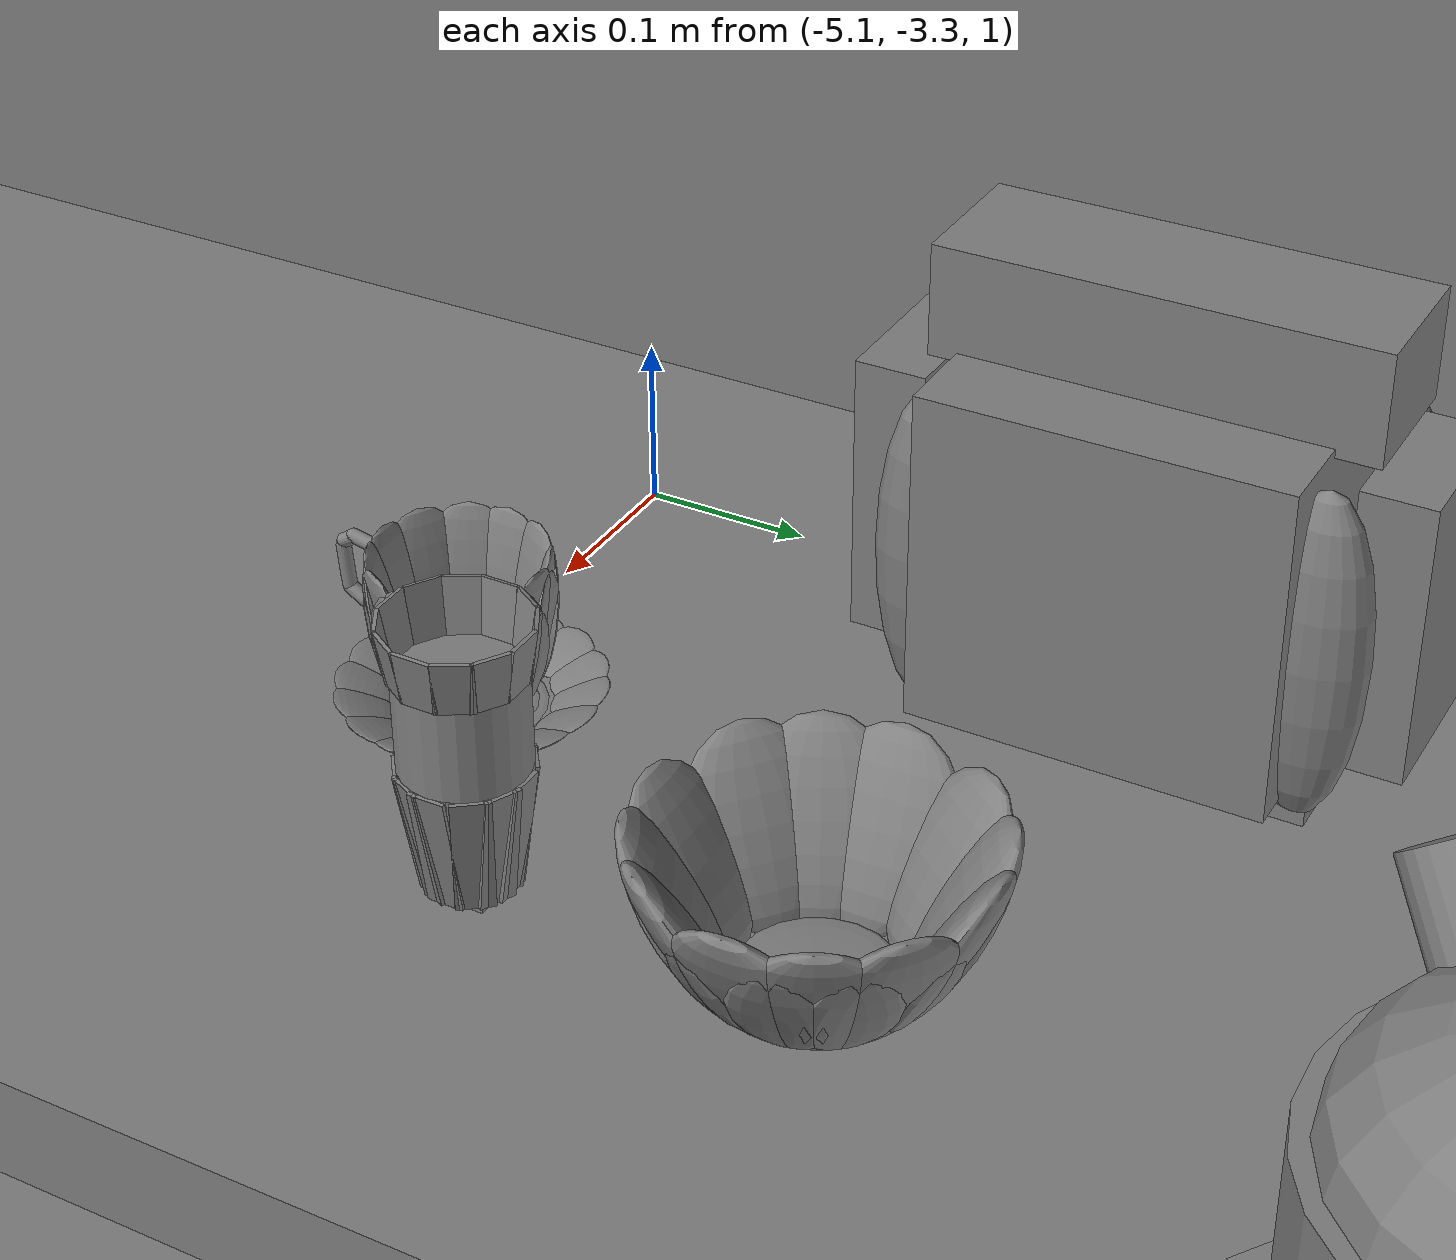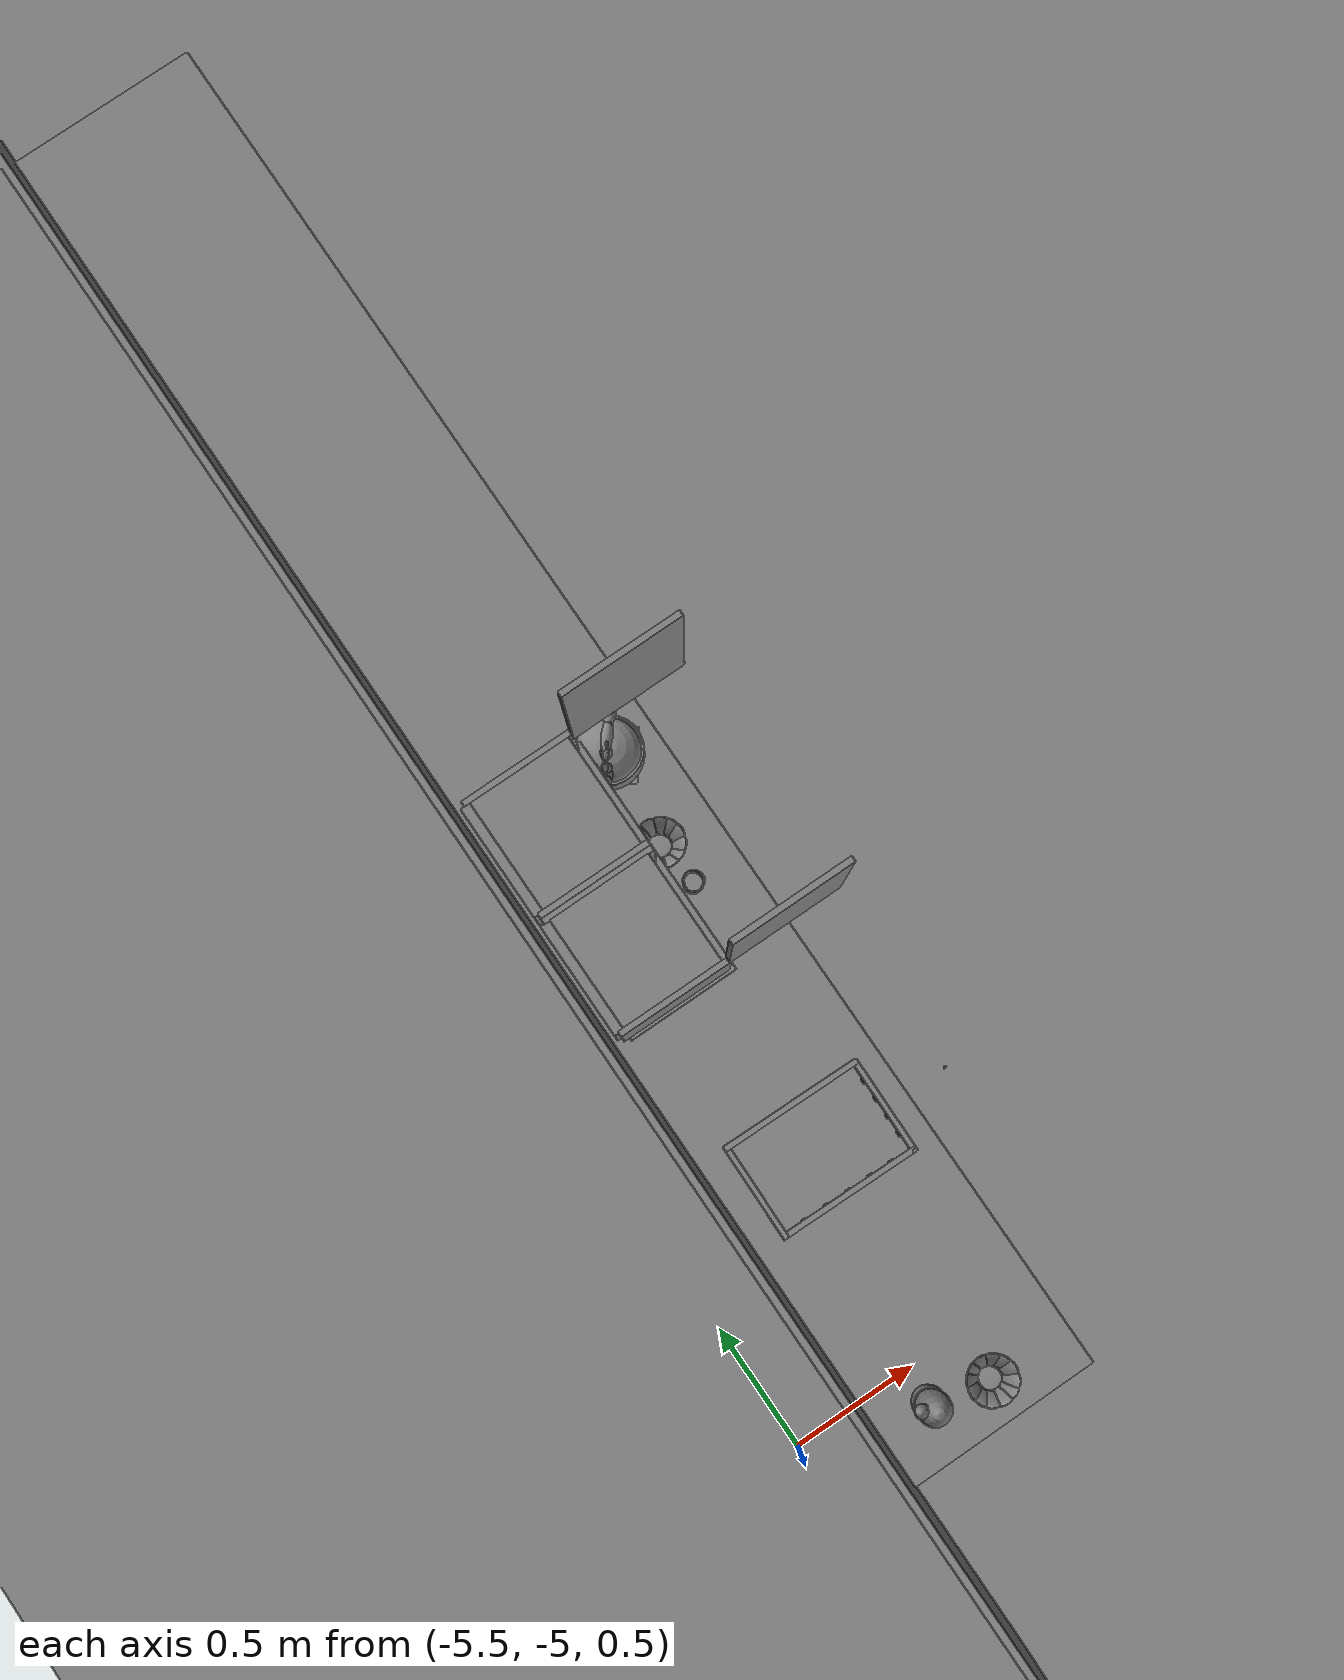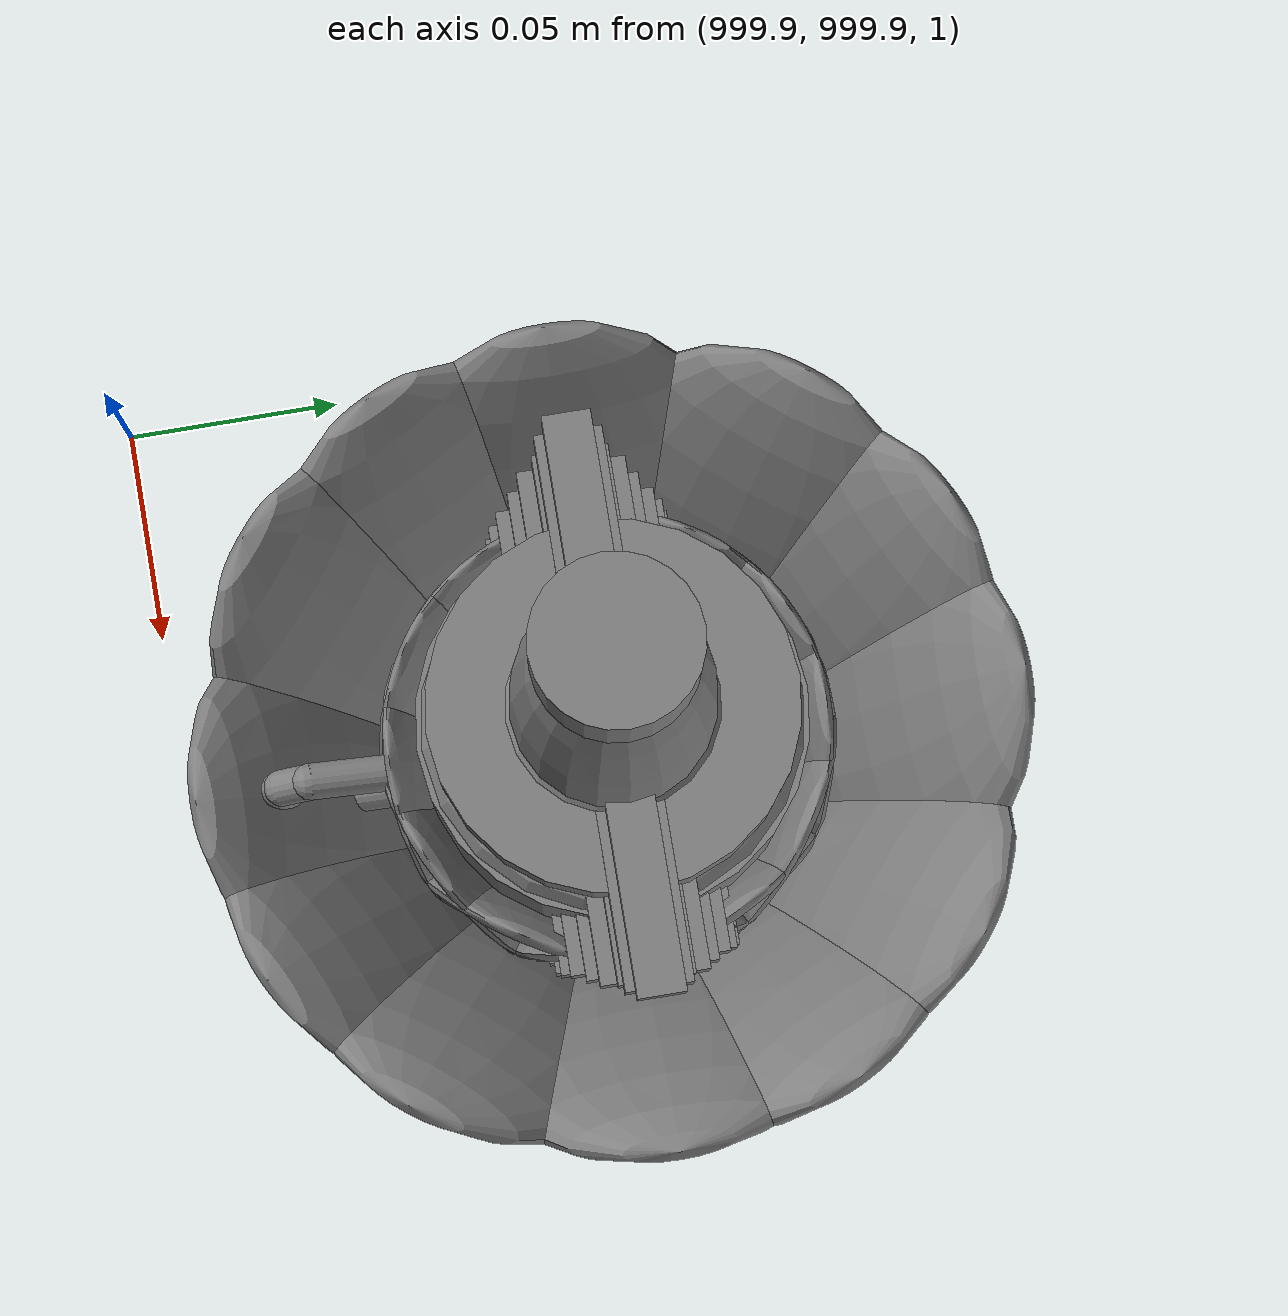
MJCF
<mujoco>
    <option gravity="0.000000000 0.000000000 -9.810000420" timestep="0.0049999999" integrator="implicitfast" density="9.8000002" viscosity="1.8000001e-05" noslip_iterations="10" iterations="100" sdf_iterations="50">
        <flag multiccd="disable"/>
    </option>
    <size memory="1000M"/>
    <compiler coordinate="local"/>
    <worldbody>
        <light cutoff="30" pos="0 1 1" dir="0 -1 -2"/>
        <light cutoff="30" pos="0 -1 1" dir="0 1 -2"/>
        <body pos="-5.020127296 -2.953741550 1.135127425" euler="89.999946594 0.000000000 0.000000000" name="Interactive Objcets_Bread">
            <geom contype="1" conaffinity="1" density="1000" type="box" material="" rgba="0.500000000 0.500000000 0.500000000 1.000000000" solimp="0.899999976 0.949999988 0.001000000" friction="1.000000000 0.005000000 0.000100000" solref="0.020000000 1.000000000" margin="0" condim="3" group="0" pos="-0.008702755 -0.017670274 -0.135069147" quat="0.707107067 -0.707106471 0.000000021 -0.000000021" size="0.045000002 0.020000000 0.079999998" name="Interactive Objcets_geom_C72CF4F7_6024_4540_89D8_BF636166087D"/>
            <geom contype="1" conaffinity="1" density="1000" type="box" material="" rgba="0.500000000 0.500000000 0.500000000 1.000000000" solimp="0.899999976 0.949999988 0.001000000" friction="1.000000000 0.005000000 0.000100000" solref="0.020000000 1.000000000" margin="0" condim="3" group="0" pos="0.033925056 -0.123201847 0.086778767" quat="0.707107067 -0.707106471 0.000000021 -0.000000021" size="0.020000000 0.020000000 0.005000000" name="Interactive Objcets_geom_DFC7448A_7BED_4E5E_8F80_7CD0F88DF7F2"/>
            <geom contype="1" conaffinity="1" density="1000" type="box" material="" rgba="0.500000000 0.500000000 0.500000000 1.000000000" solimp="0.899999976 0.949999988 0.001000000" friction="1.000000000 0.005000000 0.000100000" solref="0.020000000 1.000000000" margin="0" condim="3" group="0" pos="-0.008702755 -0.016588926 0.000174277" quat="0.707107067 -0.707106471 0.000000021 -0.000000021" size="0.090000004 0.100000001 0.094999999" name="Interactive Objcets_geom_CFCCBCCE_85E3_46A5_8F89_A3C7152237C5"/>
            <geom contype="1" conaffinity="1" density="1000" type="ellipsoid" material="" rgba="0.500000000 0.500000000 0.500000000 1.000000000" solimp="0.899999976 0.949999988 0.001000000" friction="1.000000000 0.005000000 0.000100000" solref="0.020000000 1.000000000" margin="0" condim="3" group="0" pos="-0.067312241 -0.026057482 -0.101716787" quat="0.707107067 -0.707106471 0.000000021 -0.000000021" size="0.020000000 0.029999999 0.094999999" name="Interactive Objcets_geom_85162455_582C_48BB_BFED_9D225D3E4968"/>
            <geom contype="1" conaffinity="1" density="1000" type="ellipsoid" material="" rgba="0.500000000 0.500000000 0.500000000 1.000000000" solimp="0.899999976 0.949999988 0.001000000" friction="1.000000000 0.005000000 0.000100000" solref="0.020000000 1.000000000" margin="0" condim="3" group="0" pos="0.052222252 -0.026057363 0.101459242" quat="0.707107067 -0.707106471 0.000000021 -0.000000021" size="0.020000000 0.029999999 0.094999999" name="Interactive Objcets_geom_C411EE09_0969_43F1_9436_02782FB5E6AE"/>
            <geom contype="1" conaffinity="1" density="1000" type="box" material="" rgba="0.500000000 0.500000000 0.500000000 1.000000000" solimp="0.899999976 0.949999988 0.001000000" friction="1.000000000 0.005000000 0.000100000" solref="0.020000000 1.000000000" margin="0" condim="3" group="0" pos="-0.050020695 -0.123201847 0.086778767" quat="0.707107067 -0.707106471 0.000000021 -0.000000021" size="0.020000000 0.020000000 0.005000000" name="Interactive Objcets_geom_2B21CF3F_58DA_4D76_B3D3_F8F3C2C349A9"/>
            <geom contype="1" conaffinity="1" density="1000" type="box" material="" rgba="0.500000000 0.500000000 0.500000000 1.000000000" solimp="0.899999976 0.949999988 0.001000000" friction="1.000000000 0.005000000 0.000100000" solref="0.020000000 1.000000000" margin="0" condim="3" group="0" pos="0.033925056 -0.123201728 -0.092369899" quat="0.707107067 -0.707106471 0.000000021 -0.000000021" size="0.020000000 0.020000000 0.005000000" name="Interactive Objcets_geom_0F486066_AF21_417D_A8FC_5FA3F4B5F821"/>
            <geom contype="1" conaffinity="1" density="1000" type="ellipsoid" material="" rgba="0.500000000 0.500000000 0.500000000 1.000000000" solimp="0.899999976 0.949999988 0.001000000" friction="1.000000000 0.005000000 0.000100000" solref="0.020000000 1.000000000" margin="0" condim="3" group="0" pos="-0.069190502 -0.026057363 0.101458766" quat="0.707107067 -0.707106471 0.000000021 -0.000000021" size="0.020000000 0.029999999 0.094999999" name="Interactive Objcets_geom_865A4156_1DFE_417A_8BAA_905722D73076"/>
            <geom contype="1" conaffinity="1" density="1000" type="box" material="" rgba="0.500000000 0.500000000 0.500000000 1.000000000" solimp="0.899999976 0.949999988 0.001000000" friction="1.000000000 0.005000000 0.000100000" solref="0.020000000 1.000000000" margin="0" condim="3" group="0" pos="-0.008702755 -0.017670155 0.134585604" quat="0.707107067 -0.707106471 0.000000021 -0.000000021" size="0.045000002 0.020000000 0.079999998" name="Interactive Objcets_geom_E906F78C_DE96_45D9_9E41_50B806EF4D60"/>
            <geom contype="1" conaffinity="1" density="1000" type="box" material="" rgba="0.500000000 0.500000000 0.500000000 1.000000000" solimp="0.899999976 0.949999988 0.001000000" friction="1.000000000 0.005000000 0.000100000" solref="0.020000000 1.000000000" margin="0" condim="3" group="0" pos="-0.050020695 -0.123201728 -0.092370376" quat="0.707107067 -0.707106471 0.000000021 -0.000000021" size="0.020000000 0.020000000 0.005000000" name="Interactive Objcets_geom_1C53D6A3_9F3C_4837_899F_9F6596969405"/>
            <geom contype="1" conaffinity="1" density="1000" type="box" material="" rgba="0.500000000 0.500000000 0.500000000 1.000000000" solimp="0.899999976 0.949999988 0.001000000" friction="1.000000000 0.005000000 0.000100000" solref="0.020000000 1.000000000" margin="0" condim="3" group="0" pos="-0.008702755 0.104617000 -0.003706597" quat="0.707107067 -0.707106471 0.000000021 -0.000000021" size="0.039999999 0.119999997 0.030999999" name="Interactive Objcets_geom_A894F2A1_0C45_4FF4_8D9F_7A26314D993F"/>
            <geom contype="1" conaffinity="1" density="1000" type="ellipsoid" material="" rgba="0.500000000 0.500000000 0.500000000 1.000000000" solimp="0.899999976 0.949999988 0.001000000" friction="1.000000000 0.005000000 0.000100000" solref="0.020000000 1.000000000" margin="0" condim="3" group="0" pos="0.052222252 -0.026057243 -0.106481344" quat="0.707107067 -0.707106471 0.000000021 -0.000000021" size="0.020000000 0.029999999 0.094999999" name="Interactive Objcets_geom_59B75749_555F_49B0_AE97_A8E52A6E6564"/>
            <freejoint name="Interactive Objcets_Bread"/>
        </body>
        <body pos="1000.000000000 1000.000000000 1.000000000" euler="0.000000000 0.000000000 0.000000000" name="openloong_gripper_2f85_fix_base_usda_salt">
            <geom contype="1" conaffinity="1" density="1000" type="box" material="" rgba="0.500000000 0.500000000 0.500000000 1.000000000" solimp="0.899999976 0.949999988 0.001000000" friction="1.000000000 0.005000000 0.000100000" solref="0.020000000 1.000000000" margin="0" condim="3" group="0" pos="0.000305176 0.000000000 0.084862232" quat="1.000000000 0.000000000 0.000000000 0.000000000" size="0.048999999 0.018999999 0.005000000" name="openloong_gripper_2f85_fix_base_usda_geom_D824D234_06D0_4E28_80E7_C4C4F34C5E8C"/>
            <geom contype="1" conaffinity="1" density="1000" type="box" material="" rgba="0.500000000 0.500000000 0.500000000 1.000000000" solimp="0.899999976 0.949999988 0.001000000" friction="1.000000000 0.005000000 0.000100000" solref="0.020000000 1.000000000" margin="0" condim="3" group="0" pos="0.000305176 0.000000000 0.104564309" quat="1.000000000 0.000000000 0.000000000 0.000000000" size="0.052000001 0.014000000 0.005000000" name="openloong_gripper_2f85_fix_base_usda_geom_5113FBEB_72BD_4970_9034_CD220A5E8D13"/>
            <geom contype="1" conaffinity="1" density="1000" type="box" material="" rgba="0.500000000 0.500000000 0.500000000 1.000000000" solimp="0.899999976 0.949999988 0.001000000" friction="1.000000000 0.005000000 0.000100000" solref="0.020000000 1.000000000" margin="0" condim="3" group="0" pos="0.000305176 0.000000000 0.114487171" quat="1.000000000 0.000000000 0.000000000 0.000000000" size="0.054000001 0.011500000 0.005000000" name="openloong_gripper_2f85_fix_base_usda_geom_90EE87D3_8EE4_4249_AF99_5BA75A51D2A1"/>
            <geom contype="1" conaffinity="1" density="1000" type="box" material="" rgba="0.500000000 0.500000000 0.500000000 1.000000000" solimp="0.899999976 0.949999988 0.001000000" friction="1.000000000 0.005000000 0.000100000" solref="0.020000000 1.000000000" margin="0" condim="3" group="0" pos="0.000305176 0.000000000 0.075103164" quat="1.000000000 0.000000000 0.000000000 0.000000000" size="0.048000000 0.020000000 0.005000000" name="openloong_gripper_2f85_fix_base_usda_geom_CA6EBB80_3C97_4B98_9523_97C1F74F4C48"/>
            <geom contype="1" conaffinity="1" density="1000" type="box" material="" rgba="0.500000000 0.500000000 0.500000000 1.000000000" solimp="0.899999976 0.949999988 0.001000000" friction="1.000000000 0.005000000 0.000100000" solref="0.020000000 1.000000000" margin="0" condim="3" group="0" pos="0.000305176 0.000000000 0.134892464" quat="1.000000000 0.000000000 0.000000000 0.000000000" size="0.057000000 0.007000000 0.005000000" name="openloong_gripper_2f85_fix_base_usda_geom_55572A19_973D_4E9A_912A_23B9CB37F117"/>
            <geom contype="1" conaffinity="1" density="1000" type="box" material="" rgba="0.500000000 0.500000000 0.500000000 1.000000000" solimp="0.899999976 0.949999988 0.001000000" friction="1.000000000 0.005000000 0.000100000" solref="0.020000000 1.000000000" margin="0" condim="3" group="0" pos="0.000305176 0.000000000 0.094920278" quat="1.000000000 0.000000000 0.000000000 0.000000000" size="0.050000001 0.017000001 0.005000000" name="openloong_gripper_2f85_fix_base_usda_geom_B0EF17A5_7CC9_4BC0_BA1E_9E4C8B02B27D"/>
            <geom contype="1" conaffinity="1" density="1000" type="box" material="" rgba="0.500000000 0.500000000 0.500000000 1.000000000" solimp="0.899999976 0.949999988 0.001000000" friction="1.000000000 0.005000000 0.000100000" solref="0.020000000 1.000000000" margin="0" condim="3" group="0" pos="0.000305176 0.000000000 0.065204859" quat="1.000000000 0.000000000 0.000000000 0.000000000" size="0.045000002 0.021000000 0.005000000" name="openloong_gripper_2f85_fix_base_usda_geom_E10366C8_94E8_4F03_8C5C_B6194C58E659"/>
            <geom contype="1" conaffinity="1" density="1000" type="box" material="" rgba="0.500000000 0.500000000 0.500000000 1.000000000" solimp="0.899999976 0.949999988 0.001000000" friction="1.000000000 0.005000000 0.000100000" solref="0.020000000 1.000000000" margin="0" condim="3" group="0" pos="0.000305176 0.000000000 0.144135714" quat="1.000000000 0.000000000 0.000000000 0.000000000" size="0.059000000 0.005000000 0.004000000" name="openloong_gripper_2f85_fix_base_usda_geom_83E2A003_5941_4DDE_9593_E3DBE156DDC7"/>
            <geom contype="1" conaffinity="1" density="1000" type="box" material="" rgba="0.500000000 0.500000000 0.500000000 1.000000000" solimp="0.899999976 0.949999988 0.001000000" friction="1.000000000 0.005000000 0.000100000" solref="0.020000000 1.000000000" margin="0" condim="3" group="0" pos="0.000000000 0.000000000 0.031593561" quat="1.000000000 0.000000000 0.000000000 0.000000000" size="0.041999999 0.024000000 0.029999999" name="openloong_gripper_2f85_fix_base_usda_geom_558DECCD_85C3_47C7_A5F2_D8256FFE876B"/>
            <geom contype="1" conaffinity="1" density="1000" type="box" material="" rgba="0.500000000 0.500000000 0.500000000 1.000000000" solimp="0.899999976 0.949999988 0.001000000" friction="1.000000000 0.005000000 0.000100000" solref="0.020000000 1.000000000" margin="0" condim="3" group="0" pos="0.000305176 0.000000000 0.124608755" quat="1.000000000 0.000000000 0.000000000 0.000000000" size="0.055000000 0.008000000 0.005000000" name="openloong_gripper_2f85_fix_base_usda_geom_996C846D_55F7_42CB_8DD1_48041780872D"/>
            <freejoint name="openloong_gripper_2f85_fix_base_usda_salt_joint"/>
            <site size="0.005000000 0.005000000 0.005000000" rgba="0.500000000 0.500000000 0.500000000 1.000000000" pos="0.000000000 0.000000000 0.000000000" quat="1.000000000 0.000000000 0.000000000 0.000000000" group="0" type="sphere" name="openloong_gripper_2f85_fix_base_usda_saltsite"/>
        </body>
        <body pos="1000.000000000 1000.000000000 1.000000000" euler="0.000000000 0.000000000 0.000000000" name="openloong_gripper_2f85_fix_base_usda_bow_yellow_kps">
            <geom contype="1" conaffinity="1" density="1000" type="ellipsoid" material="" rgba="0.500000000 0.500000000 0.500000000 1.000000000" solimp="0.899999976 0.949999988 0.001000000" friction="1.000000000 0.005000000 0.000100000" solref="0.020000000 1.000000000" margin="0" condim="3" group="0" pos="-0.052185059 0.040283203 0.044118762" quat="0.919264615 -0.076883033 -0.225593656 -0.313287765" size="0.010000000 0.039999999 0.052000001" name="openloong_gripper_2f85_fix_base_usda_geom_9CB01F2B_6D32_4AF4_A53B_1B70866F41B0"/>
            <geom contype="1" conaffinity="1" density="1000" type="ellipsoid" material="" rgba="0.500000000 0.500000000 0.500000000 1.000000000" solimp="0.899999976 0.949999988 0.001000000" friction="1.000000000 0.005000000 0.000100000" solref="0.020000000 1.000000000" margin="0" condim="3" group="0" pos="-0.000061035 0.065979004 0.044118762" quat="0.687598765 -0.168314874 -0.168741167 -0.685860336" size="0.010000000 0.039999999 0.052000001" name="openloong_gripper_2f85_fix_base_usda_geom_A9749E16_912A_459A_A0BA_2B666BB28DA8"/>
            <geom contype="1" conaffinity="1" density="1000" type="box" material="" rgba="0.500000000 0.500000000 0.500000000 1.000000000" solimp="0.899999976 0.949999988 0.001000000" friction="1.000000000 0.005000000 0.000100000" solref="0.020000000 1.000000000" margin="0" condim="3" group="0" pos="0.000061035 0.000000000 -0.002001643" quat="1.000000000 0.000000000 0.000000000 0.000000000" size="0.029999999 0.029999999 0.002000000" name="openloong_gripper_2f85_fix_base_usda_geom_23CE7129_1F50_49AD_A394_71AF4ABB251C"/>
            <geom contype="1" conaffinity="1" density="1000" type="ellipsoid" material="" rgba="0.500000000 0.500000000 0.500000000 1.000000000" solimp="0.899999976 0.949999988 0.001000000" friction="1.000000000 0.005000000 0.000100000" solref="0.020000000 1.000000000" margin="0" condim="3" group="0" pos="0.029418945 -0.059082031 0.044118762" quat="0.825555861 0.125530601 0.202597082 -0.511521280" size="0.010000000 0.039999999 0.052000001" name="openloong_gripper_2f85_fix_base_usda_geom_4B04F4E4_1E7E_471E_9E04_E08E8116AC79"/>
            <geom contype="1" conaffinity="1" density="1000" type="ellipsoid" material="" rgba="0.500000000 0.500000000 0.500000000 1.000000000" solimp="0.899999976 0.949999988 0.001000000" friction="1.000000000 0.005000000 0.000100000" solref="0.020000000 1.000000000" margin="0" condim="3" group="0" pos="0.000244141 -0.065979004 0.044118762" quat="0.687598765 0.168314651 0.168741375 -0.685860336" size="0.010000000 0.039999999 0.052000001" name="openloong_gripper_2f85_fix_base_usda_geom_02F2C562_837A_429F_8E58_D4D1AA05AA46"/>
            <geom contype="1" conaffinity="1" density="1000" type="ellipsoid" material="" rgba="0.500000000 0.500000000 0.500000000 1.000000000" solimp="0.899999976 0.949999988 0.001000000" friction="1.000000000 0.005000000 0.000100000" solref="0.020000000 1.000000000" margin="0" condim="3" group="0" pos="0.000061035 0.000000000 0.000446677" quat="1.000000000 0.000000000 0.000000000 0.000000000" size="0.039999999 0.039999999 0.002000000" name="openloong_gripper_2f85_fix_base_usda_geom_A125E38C_BA15_4FC2_BB7E_3A919434EB87"/>
            <geom contype="1" conaffinity="1" density="1000" type="ellipsoid" material="" rgba="0.500000000 0.500000000 0.500000000 1.000000000" solimp="0.899999976 0.949999988 0.001000000" friction="1.000000000 0.005000000 0.000100000" solref="0.020000000 1.000000000" margin="0" condim="3" group="0" pos="0.059082031 0.029541016 0.044118762" quat="0.223252773 -0.231952220 -0.054787423 -0.945174456" size="0.010000000 0.039999999 0.052000001" name="openloong_gripper_2f85_fix_base_usda_geom_C106C073_A2EF_4D14_8167_024927BA2D2A"/>
            <geom contype="1" conaffinity="1" density="1000" type="ellipsoid" material="" rgba="0.500000000 0.500000000 0.500000000 1.000000000" solimp="0.899999976 0.949999988 0.001000000" friction="1.000000000 0.005000000 0.000100000" solref="0.020000000 1.000000000" margin="0" condim="3" group="0" pos="0.000061035 0.000000000 0.007335305" quat="1.000000000 0.000000000 0.000000000 0.000000000" size="0.039999999 0.039999999 0.002000000" name="openloong_gripper_2f85_fix_base_usda_geom_7EAC0CCD_B783_43B0_911C_75A9FEE58120"/>
            <geom contype="1" conaffinity="1" density="1000" type="ellipsoid" material="" rgba="0.500000000 0.500000000 0.500000000 1.000000000" solimp="0.899999976 0.949999988 0.001000000" friction="1.000000000 0.005000000 0.000100000" solref="0.020000000 1.000000000" margin="0" condim="3" group="0" pos="-0.029296875 0.059082031 0.044118762" quat="0.825555861 -0.125530809 -0.202596918 -0.511521280" size="0.010000000 0.039999999 0.052000001" name="openloong_gripper_2f85_fix_base_usda_geom_59D6989D_63BA_4C96_9A72_C80B48A3D8FB"/>
            <geom contype="1" conaffinity="1" density="1000" type="ellipsoid" material="" rgba="0.500000000 0.500000000 0.500000000 1.000000000" solimp="0.899999976 0.949999988 0.001000000" friction="1.000000000 0.005000000 0.000100000" solref="0.020000000 1.000000000" margin="0" condim="3" group="0" pos="0.040222168 0.052368164 0.044118762" quat="0.429593176 -0.213750049 -0.105424821 -0.871002972" size="0.010000000 0.039999999 0.052000001" name="openloong_gripper_2f85_fix_base_usda_geom_1F93D101_284A_484F_8C73_54E2C0103CB4"/>
            <geom contype="1" conaffinity="1" density="1000" type="ellipsoid" material="" rgba="0.500000000 0.500000000 0.500000000 1.000000000" solimp="0.899999976 0.949999988 0.001000000" friction="1.000000000 0.005000000 0.000100000" solref="0.020000000 1.000000000" margin="0" condim="3" group="0" pos="0.066040039 0.000000000 0.044118762" quat="0.971183062 -0.000000156 0.238334835 0.000000030" size="0.010000000 0.039999999 0.052000001" name="openloong_gripper_2f85_fix_base_usda_geom_CB9BBFE2_E6AB_4068_92DA_63DEC5BBEFF9"/>
            <geom contype="1" conaffinity="1" density="1000" type="ellipsoid" material="" rgba="0.500000000 0.500000000 0.500000000 1.000000000" solimp="0.899999976 0.949999988 0.001000000" friction="1.000000000 0.005000000 0.000100000" solref="0.020000000 1.000000000" margin="0" condim="3" group="0" pos="0.052307129 -0.040283203 0.044118762" quat="0.919264674 0.076882750 0.225593731 -0.313287705" size="0.010000000 0.039999999 0.052000001" name="openloong_gripper_2f85_fix_base_usda_geom_24812B7E_BD83_45FA_9D77_BA458165F1A0"/>
            <geom contype="1" conaffinity="1" density="1000" type="ellipsoid" material="" rgba="0.500000000 0.500000000 0.500000000 1.000000000" solimp="0.899999976 0.949999988 0.001000000" friction="1.000000000 0.005000000 0.000100000" solref="0.020000000 1.000000000" margin="0" condim="3" group="0" pos="-0.065917969 0.000000000 0.044118762" quat="0.971183062 -0.000000142 -0.238334835 0.000000030" size="0.010000000 0.039999999 0.052000001" name="openloong_gripper_2f85_fix_base_usda_geom_4DFB4206_B17E_46FA_B1E7_1F941609E8FD"/>
            <geom contype="1" conaffinity="1" density="1000" type="ellipsoid" material="" rgba="0.500000000 0.500000000 0.500000000 1.000000000" solimp="0.899999976 0.949999988 0.001000000" friction="1.000000000 0.005000000 0.000100000" solref="0.020000000 1.000000000" margin="0" condim="3" group="0" pos="-0.058898926 -0.029541016 0.044118762" quat="0.223252758 0.231952101 0.054787733 -0.945174575" size="0.010000000 0.039999999 0.052000001" name="openloong_gripper_2f85_fix_base_usda_geom_387490DC_75FD_46EB_88FE_CB819A9383F7"/>
            <geom contype="1" conaffinity="1" density="1000" type="ellipsoid" material="" rgba="0.500000000 0.500000000 0.500000000 1.000000000" solimp="0.899999976 0.949999988 0.001000000" friction="1.000000000 0.005000000 0.000100000" solref="0.020000000 1.000000000" margin="0" condim="3" group="0" pos="-0.040100098 -0.052368164 0.044118762" quat="0.429593235 0.213749886 0.105425082 -0.871003032" size="0.010000000 0.039999999 0.052000001" name="openloong_gripper_2f85_fix_base_usda_geom_D39D7E06_410D_486B_9EC8_2A38D1AE5B3F"/>
            <freejoint name="openloong_gripper_2f85_fix_base_usda_bow_yellow_kps_joint"/>
            <site size="0.005000000 0.005000000 0.005000000" rgba="0.500000000 0.500000000 0.500000000 1.000000000" pos="0.000000000 0.000000000 0.000000000" quat="0.999961913 0.008726534 0.000000000 0.000000000" group="0" type="sphere" name="openloong_gripper_2f85_fix_base_usda_bow_yellow_kps"/>
        </body>
        <body pos="1000.000000000 1000.000000000 1.000000000" euler="0.000000000 0.000000000 0.000000000" name="openloong_gripper_2f85_fix_base_usda_jar_01">
            <geom contype="1" conaffinity="1" density="1000" type="box" material="" rgba="0.500000000 0.500000000 0.500000000 1.000000000" solimp="0.899999976 0.949999988 0.001000000" friction="1.000000000 0.005000000 0.000100000" solref="0.020000000 1.000000000" margin="0" condim="3" group="0" pos="0.000000000 0.000000000 0.006158113" quat="1.000000000 0.000000000 0.000000000 0.000000000" size="0.020000000 0.020000000 0.005000000" name="openloong_gripper_2f85_fix_base_usda_geom_C00A0B54_D468_4CA2_A56E_F9C3CE80A1B6"/>
            <geom contype="1" conaffinity="1" density="1000" type="cylinder" material="" rgba="0.500000000 0.500000000 0.500000000 1.000000000" solimp="0.899999976 0.949999988 0.001000000" friction="1.000000000 0.005000000 0.000100000" solref="0.020000000 1.000000000" margin="0" condim="3" group="0" pos="0.000000000 0.000000000 0.062744498" quat="1.000000000 0.000000000 0.000000000 0.000000000" size="0.041000001 0.052999999 1.000000000" name="openloong_gripper_2f85_fix_base_usda_geom_8832CCE6_42E8_48A7_9098_F96F39531B17"/>
            <geom contype="1" conaffinity="1" density="1000" type="ellipsoid" material="" rgba="0.500000000 0.500000000 0.500000000 1.000000000" solimp="0.899999976 0.949999988 0.001000000" friction="1.000000000 0.005000000 0.000100000" solref="0.020000000 1.000000000" margin="0" condim="3" group="0" pos="0.000000000 0.000000000 0.122252703" quat="1.000000000 0.000000000 0.000000000 0.000000000" size="0.035999998 0.035999998 0.010000000" name="openloong_gripper_2f85_fix_base_usda_geom_88182D6E_C7AF_449B_B420_1EE322FFCA4C"/>
            <geom contype="1" conaffinity="1" density="1000" type="cylinder" material="" rgba="0.500000000 0.500000000 0.500000000 1.000000000" solimp="0.899999976 0.949999988 0.001000000" friction="1.000000000 0.005000000 0.000100000" solref="0.020000000 1.000000000" margin="0" condim="3" group="0" pos="0.000000000 0.000000000 0.015747190" quat="1.000000000 0.000000000 0.000000000 0.000000000" size="0.035000000 0.010000000 1.000000000" name="openloong_gripper_2f85_fix_base_usda_geom_6CFD887C_7C78_4C50_9630_F083511756FD"/>
            <geom contype="1" conaffinity="1" density="1000" type="ellipsoid" material="" rgba="0.500000000 0.500000000 0.500000000 1.000000000" solimp="0.899999976 0.949999988 0.001000000" friction="1.000000000 0.005000000 0.000100000" solref="0.020000000 1.000000000" margin="0" condim="3" group="0" pos="0.000000000 0.000000000 0.115815401" quat="1.000000000 0.000000000 0.000000000 0.000000000" size="0.039999999 0.039999999 0.010000000" name="openloong_gripper_2f85_fix_base_usda_geom_26C3F8C2_B209_42A6_A088_665B3640190D"/>
            <geom contype="1" conaffinity="1" density="1000" type="cylinder" material="" rgba="0.500000000 0.500000000 0.500000000 1.000000000" solimp="0.899999976 0.949999988 0.001000000" friction="1.000000000 0.005000000 0.000100000" solref="0.020000000 1.000000000" margin="0" condim="3" group="0" pos="0.000000000 0.000000000 0.133183479" quat="1.000000000 0.000000000 0.000000000 0.000000000" size="0.037999999 0.006500000 1.000000000" name="openloong_gripper_2f85_fix_base_usda_geom_D3A62B0E_4244_4856_9B92_84EE01EEE8A4"/>
            <freejoint name="openloong_gripper_2f85_fix_base_usda_jar_01_joint"/>
            <site size="0.005000000 0.005000000 0.005000000" rgba="0.500000000 0.500000000 0.500000000 1.000000000" pos="0.000000000 0.000000000 0.000000000" quat="1.000000000 0.000000000 0.000000000 0.000000000" group="0" type="sphere" name="openloong_gripper_2f85_fix_base_usda_jar_01site"/>
        </body>
        <body pos="1000.000000000 1000.000000000 1.000000000" euler="0.000000000 0.000000000 0.000000000" name="openloong_gripper_2f85_fix_base_usda_bottle_red">
            <geom contype="1" conaffinity="1" density="1000" type="ellipsoid" material="" rgba="0.500000000 0.500000000 0.500000000 1.000000000" solimp="0.899999976 0.949999988 0.001000000" friction="1.000000000 0.005000000 0.000100000" solref="0.020000000 1.000000000" margin="0" condim="3" group="0" pos="0.000000000 0.000000000 0.144284487" quat="1.000000000 0.000000000 0.000000000 0.000000000" size="0.021000000 0.021000000 0.079999998" name="openloong_gripper_2f85_fix_base_usda_geom_93D2464E_3D2E_4143_A901_987394E752C3"/>
            <geom contype="1" conaffinity="1" density="1000" type="cylinder" material="" rgba="0.500000000 0.500000000 0.500000000 1.000000000" solimp="0.899999976 0.949999988 0.001000000" friction="1.000000000 0.005000000 0.000100000" solref="0.020000000 1.000000000" margin="0" condim="3" group="0" pos="0.000000000 0.000000000 0.220618963" quat="1.000000000 0.000000000 0.000000000 0.000000000" size="0.016000001 0.010000000 1.000000000" name="openloong_gripper_2f85_fix_base_usda_geom_B52E801E_AB5E_40A2_B2A2_D05BC8DD0C84"/>
            <geom contype="1" conaffinity="1" density="1000" type="ellipsoid" material="" rgba="0.500000000 0.500000000 0.500000000 1.000000000" solimp="0.899999976 0.949999988 0.001000000" friction="1.000000000 0.005000000 0.000100000" solref="0.020000000 1.000000000" margin="0" condim="3" group="0" pos="0.000000000 0.000000000 0.118945479" quat="1.000000000 0.000000000 0.000000000 0.000000000" size="0.030999999 0.030999999 0.029999999" name="openloong_gripper_2f85_fix_base_usda_geom_774E7476_F1CB_4FE1_A3D3_8DE30BCBC48B"/>
            <geom contype="1" conaffinity="1" density="1000" type="box" material="" rgba="0.500000000 0.500000000 0.500000000 1.000000000" solimp="0.899999976 0.949999988 0.001000000" friction="1.000000000 0.005000000 0.000100000" solref="0.020000000 1.000000000" margin="0" condim="3" group="0" pos="0.000000000 0.000000000 0.002189159" quat="1.000000000 0.000000000 0.000000000 0.000000000" size="0.020000000 0.020000000 0.003000000" name="openloong_gripper_2f85_fix_base_usda_geom_C09060EA_2E09_43BE_BE05_FA553377E60F"/>
            <geom contype="1" conaffinity="1" density="1000" type="cylinder" material="" rgba="0.500000000 0.500000000 0.500000000 1.000000000" solimp="0.899999976 0.949999988 0.001000000" friction="1.000000000 0.005000000 0.000100000" solref="0.020000000 1.000000000" margin="0" condim="3" group="0" pos="0.000000000 -0.000366211 0.060884237" quat="1.000000000 0.000000000 0.000000000 0.000000000" size="0.030999999 0.057999998 1.000000000" name="openloong_gripper_2f85_fix_base_usda_geom_DD514245_41ED_4F43_B241_4922861036AA"/>
            <freejoint name="openloong_gripper_2f85_fix_base_usda_bottle_red_joint"/>
            <site size="0.005000000 0.005000000 0.005000000" rgba="0.500000000 0.500000000 0.500000000 1.000000000" pos="0.000000000 0.000000000 0.000000000" quat="0.999961913 0.008726535 0.000000000 0.000000000" group="0" type="sphere" name="openloong_gripper_2f85_fix_base_usda_bottle_redsite"/>
        </body>
        <body pos="0.000000000 0.000000000 0.000000000" euler="0.000000000 0.000000000 0.000000000" name="Static Objcets_Static Objcets">
            <geom contype="1" conaffinity="1" density="1000" type="box" material="" rgba="0.500000000 0.500000000 0.500000000 1.000000000" solimp="0.899999976 0.949999988 0.001000000" friction="1.000000000 0.005000000 0.000100000" solref="0.020000000 1.000000000" margin="0" condim="3" group="0" pos="-5.189302921 -3.293644905 1.760152459" quat="0.707107067 0.707106471 0.000000000 0.000000000" size="0.025000000 0.159999996 0.200000003" name="Static Objcets_geom_FBA6636C_27AF_43D0_AD27_E803EAAE72F7"/>
            <geom contype="1" conaffinity="1" density="1000" type="box" material="" rgba="0.500000000 0.500000000 0.500000000 1.000000000" solimp="0.899999976 0.949999988 0.001000000" friction="1.000000000 0.005000000 0.000100000" solref="0.020000000 1.000000000" margin="0" condim="3" group="0" pos="-4.999745846 -3.497932911 1.764780521" quat="0.707107067 0.707106471 0.000000000 0.000000000" size="0.200000003 0.159999996 0.010000000" name="Static Objcets_geom_554A4754_599E_4737_B485_D340784BF57B"/>
            <geom contype="1" conaffinity="1" density="1000" type="box" material="" rgba="0.500000000 0.500000000 0.500000000 1.000000000" solimp="0.899999976 0.949999988 0.001000000" friction="1.000000000 0.005000000 0.000100000" solref="0.020000000 1.000000000" margin="0" condim="3" group="0" pos="-4.979488373 -3.297635794 1.591412544" quat="0.707106829 0.707106709 0.000000000 0.000000000" size="0.200000003 0.015000000 0.219999999" name="Static Objcets_geom_12D305AD_D0A2_4279_B4E6_A6F2C0A64FF1"/>
            <geom contype="1" conaffinity="1" density="1000" type="box" material="" rgba="0.500000000 0.500000000 0.500000000 1.000000000" solimp="0.899999976 0.949999988 0.001000000" friction="1.000000000 0.005000000 0.000100000" solref="0.020000000 1.000000000" margin="0" condim="3" group="0" pos="-4.999745846 -3.087441683 1.763863802" quat="0.707107067 0.707106471 0.000000000 0.000000000" size="0.200000003 0.159999996 0.010000000" name="Static Objcets_geom_388C242A_A3BC_4783_9BD3_DC2057BBF3D2"/>
            <geom contype="1" conaffinity="1" density="1000" type="box" material="" rgba="0.500000000 0.500000000 0.500000000 1.000000000" solimp="0.899999976 0.949999988 0.001000000" friction="1.000000000 0.005000000 0.000100000" solref="0.020000000 1.000000000" margin="0" condim="3" group="0" pos="-5.000125408 -3.294431210 1.913951039" quat="0.707107067 0.707106471 0.000000000 0.000000000" size="0.180000007 0.010000000 0.200000003" name="Static Objcets_geom_B65C6652_91EA_4C2A_BDCB_AED1A22C491E"/>
            <geom contype="1" conaffinity="1" density="1000" type="box" material="" rgba="0.500000000 0.500000000 0.500000000 1.000000000" solimp="0.899999976 0.949999988 0.001000000" friction="1.000000000 0.005000000 0.000100000" solref="0.020000000 1.000000000" margin="0" condim="3" group="0" pos="-4.873187065 -2.461376429 0.977675021" quat="0.707107067 0.707106471 0.000000000 0.000000000" size="0.370000005 0.029999999 2.799999952" name="Static Objcets_geom_3996F67A_DDBE_4B73_9741_B75211816305"/>
            <geom contype="1" conaffinity="1" density="1000" type="box" material="" rgba="0.500000000 0.500000000 0.500000000 1.000000000" solimp="0.899999976 0.949999988 0.001000000" friction="1.000000000 0.005000000 0.000100000" solref="0.020000000 1.000000000" margin="0" condim="3" group="0" pos="-5.244853973 -2.375543594 1.820221663" quat="0.707107008 0.707106531 0.000000000 0.000000000" size="0.010000000 1.500000000 3.700000048" name="Static Objcets_geom_4B7A5681_F396_4BBB_89B5_FA727F2E3E20"/>
            <geom contype="1" conaffinity="1" density="1000" type="box" material="" rgba="0.500000000 0.500000000 0.500000000 1.000000000" solimp="0.899999976 0.949999988 0.001000000" friction="1.000000000 0.005000000 0.000100000" solref="0.020000000 1.000000000" margin="0" condim="3" group="0" pos="-0.720102787 0.222944975 -1.102830648" quat="0.000000954 1.000000000 0.000000000 0.000000000" size="8.000000000 8.000000000 0.010000000" name="Static Objcets_geom_59DF25B9_C49C_47B2_A963_B772E7CD440D"/>
            <geom contype="1" conaffinity="1" density="1000" type="box" material="" rgba="0.500000000 0.500000000 0.500000000 1.000000000" solimp="0.899999976 0.949999988 0.001000000" friction="1.000000000 0.005000000 0.000100000" solref="0.020000000 1.000000000" margin="0" condim="3" group="0" pos="-4.999745846 -2.653569937 1.764779806" quat="0.707107067 0.707106471 0.000000000 0.000000000" size="0.200000003 0.159999996 0.010000000" name="Static Objcets_geom_DB872904_47B2_4C03_A9D2_7959E267773D"/>
            <geom contype="1" conaffinity="1" density="1000" type="box" material="" rgba="0.500000000 0.500000000 0.500000000 1.000000000" solimp="0.899999976 0.949999988 0.001000000" friction="1.000000000 0.005000000 0.000100000" solref="0.020000000 1.000000000" margin="0" condim="3" group="0" pos="-5.000125408 -2.861802340 1.913950682" quat="0.707107067 0.707106471 0.000000000 0.000000000" size="0.180000007 0.010000000 0.200000003" name="Static Objcets_geom_4D93AFAE_94D8_490E_821C_2DD1C5A5A81E"/>
            <geom contype="1" conaffinity="1" density="1000" type="box" material="" rgba="0.500000000 0.500000000 0.500000000 1.000000000" solimp="0.899999976 0.949999988 0.001000000" friction="1.000000000 0.005000000 0.000100000" solref="0.020000000 1.000000000" margin="0" condim="3" group="0" pos="-5.189302921 -2.861564636 1.760152102" quat="0.707107067 0.707106471 0.000000000 0.000000000" size="0.025000000 0.159999996 0.200000003" name="Static Objcets_geom_3D877347_E671_4BE0_B7AB_1961F9F7B8DA"/>
            <geom contype="1" conaffinity="1" density="1000" type="box" material="" rgba="0.500000000 0.500000000 0.500000000 1.000000000" solimp="0.899999976 0.949999988 0.001000000" friction="1.000000000 0.005000000 0.000100000" solref="0.020000000 1.000000000" margin="0" condim="3" group="0" pos="-4.979488373 -2.855390549 1.591412187" quat="0.707106709 0.707106769 0.000000000 0.000000000" size="0.200000003 0.015000000 0.219999999" name="Static Objcets_geom_0EE223E1_5F6C_4370_90E5_7F16C62F18ED"/>
            <geom contype="1" conaffinity="1" density="1000" type="box" material="" rgba="0.500000000 0.500000000 0.500000000 1.000000000" solimp="0.899999976 0.949999988 0.001000000" friction="1.000000000 0.005000000 0.000100000" solref="0.020000000 1.000000000" margin="0" condim="3" group="0" pos="-4.999745846 -3.066934109 1.765979409" quat="0.707107067 0.707106471 0.000000000 0.000000000" size="0.200000003 0.159999996 0.010000000" name="Static Objcets_geom_68C28C07_A528_4D65_A398_5C09D6DEB37F"/>
        </body>
        <body pos="-4.705342293 -3.169416904 1.103703976" euler="0.000000000 0.000000000 0.000000000" name="Interactive Objcets_cup_02">
            <geom contype="1" conaffinity="1" density="1000" type="box" material="" rgba="0.500000000 0.500000000 0.500000000 1.000000000" solimp="0.899999976 0.949999988 0.001000000" friction="1.000000000 0.005000000 0.000100000" solref="0.020000000 1.000000000" margin="0" condim="3" group="0" pos="0.022285938 0.016949892 -0.037281752" quat="0.893179297 -0.070051625 0.034732576 -0.442851186" size="0.010000000 0.001000000 0.035000000" name="Interactive Objcets_geom_24AE3A10_3FA1_45C1_82C8_0661A99E1E9C"/>
            <geom contype="1" conaffinity="1" density="1000" type="box" material="" rgba="0.500000000 0.500000000 0.500000000 1.000000000" solimp="0.899999976 0.949999988 0.001000000" friction="1.000000000 0.005000000 0.000100000" solref="0.020000000 1.000000000" margin="0" condim="3" group="0" pos="0.034549713 0.000000000 0.062637210" quat="0.704941988 -0.055288255 0.055288251 -0.704942048" size="0.010000000 0.001000000 0.015000000" name="Interactive Objcets_geom_1012B7F9_71BB_49B8_A22A_15BE57D13492"/>
            <geom contype="1" conaffinity="1" density="1000" type="box" material="" rgba="0.500000000 0.500000000 0.500000000 1.000000000" solimp="0.899999976 0.949999988 0.001000000" friction="1.000000000 0.005000000 0.000100000" solref="0.020000000 1.000000000" margin="0" condim="3" group="0" pos="0.029378891 -0.018181801 0.062637210" quat="0.870895982 0.068302706 0.038053915 0.485208035" size="0.010000000 0.001000000 0.015000000" name="Interactive Objcets_geom_D904F916_33AB_47E2_B061_A0439ECEB40F"/>
            <geom contype="1" conaffinity="1" density="1000" type="box" material="" rgba="0.500000000 0.500000000 0.500000000 1.000000000" solimp="0.899999976 0.949999988 0.001000000" friction="1.000000000 0.005000000 0.000100000" solref="0.020000000 1.000000000" margin="0" condim="3" group="0" pos="0.000000000 -0.034549713 0.062637210" quat="0.996938646 0.078187965 0.000000000 0.000000000" size="0.010000000 0.001000000 0.015000000" name="Interactive Objcets_geom_71265919_67BA_4F84_A858_3AACA6B72F39"/>
            <geom contype="1" conaffinity="1" density="1000" type="cylinder" material="" rgba="0.500000000 0.500000000 0.500000000 1.000000000" solimp="0.899999976 0.949999988 0.001000000" friction="1.000000000 0.005000000 0.000100000" solref="0.020000000 1.000000000" margin="0" condim="3" group="0" pos="0.000000000 0.000000000 0.022491097" quat="1.000000000 0.000000030 0.000000000 0.000000000" size="0.033000000 0.025000000 1.000000000" name="Interactive Objcets_geom_660EC66F_876A_4224_93D4_77B78B633BEA"/>
            <geom contype="1" conaffinity="1" density="1000" type="box" material="" rgba="0.500000000 0.500000000 0.500000000 1.000000000" solimp="0.899999976 0.949999988 0.001000000" friction="1.000000000 0.005000000 0.000100000" solref="0.020000000 1.000000000" margin="0" condim="3" group="0" pos="0.000000000 0.034549713 0.062637210" quat="0.996938646 -0.078187965 0.000000000 0.000000000" size="0.010000000 0.001000000 0.015000000" name="Interactive Objcets_geom_699314C1_0839_4D53_BFB3_8E4782F97D89"/>
            <geom contype="1" conaffinity="1" density="1000" type="box" material="" rgba="0.500000000 0.500000000 0.500000000 1.000000000" solimp="0.899999976 0.949999988 0.001000000" friction="1.000000000 0.005000000 0.000100000" solref="0.020000000 1.000000000" margin="0" condim="3" group="0" pos="0.011943817 0.025323629 -0.037281752" quat="0.972834349 -0.076298930 0.017089661 -0.217898533" size="0.010000000 0.001000000 0.035000000" name="Interactive Objcets_geom_DFDB4642_D920_4DF8_ABDA_8FD44ED84F80"/>
            <geom contype="1" conaffinity="1" density="1000" type="box" material="" rgba="0.500000000 0.500000000 0.500000000 1.000000000" solimp="0.899999976 0.949999988 0.001000000" friction="1.000000000 0.005000000 0.000100000" solref="0.020000000 1.000000000" margin="0" condim="3" group="0" pos="0.025214195 -0.011892319 -0.037281752" quat="0.841975451 0.066034243 0.041866414 0.533820212" size="0.010000000 0.001000000 0.035000000" name="Interactive Objcets_geom_46904084_4FCA_45D8_9650_E39F1C629AE1"/>
            <geom contype="1" conaffinity="1" density="1000" type="box" material="" rgba="0.500000000 0.500000000 0.500000000 1.000000000" solimp="0.899999976 0.949999988 0.001000000" friction="1.000000000 0.005000000 0.000100000" solref="0.020000000 1.000000000" margin="0" condim="3" group="0" pos="-0.027999878 0.000000000 -0.037281752" quat="0.704941988 0.055288255 -0.055288251 -0.704942048" size="0.010000000 0.001000000 0.035000000" name="Interactive Objcets_geom_7BB03AC1_2E49_4352_985B_03381A36F235"/>
            <geom contype="1" conaffinity="1" density="1000" type="box" material="" rgba="0.500000000 0.500000000 0.500000000 1.000000000" solimp="0.899999976 0.949999988 0.001000000" friction="1.000000000 0.005000000 0.000100000" solref="0.020000000 1.000000000" margin="0" condim="3" group="0" pos="0.017436981 -0.029826880 0.062637210" quat="0.962265730 0.075468659 0.020441191 0.260636479" size="0.010000000 0.001000000 0.015000000" name="Interactive Objcets_geom_DF1CD48C_B376_46A0_94AF_006C3F2D2CA6"/>
            <geom contype="1" conaffinity="1" density="1000" type="box" material="" rgba="0.500000000 0.500000000 0.500000000 1.000000000" solimp="0.899999976 0.949999988 0.001000000" friction="1.000000000 0.005000000 0.000100000" solref="0.020000000 1.000000000" margin="0" condim="3" group="0" pos="0.029827118 0.017437220 0.062637210" quat="0.864722252 -0.067819774 0.038910985 -0.496126890" size="0.010000000 0.001000000 0.015000000" name="Interactive Objcets_geom_5AC5CC12_799E_4701_B071_E350D3EC0A09"/>
            <geom contype="1" conaffinity="1" density="1000" type="box" material="" rgba="0.500000000 0.500000000 0.500000000 1.000000000" solimp="0.899999976 0.949999988 0.001000000" friction="1.000000000 0.005000000 0.000100000" solref="0.020000000 1.000000000" margin="0" condim="3" group="0" pos="0.000000000 0.027877331 -0.037281752" quat="0.996938646 -0.078187965 0.000000000 0.000000000" size="0.010000000 0.001000000 0.035000000" name="Interactive Objcets_geom_D5853AEB_420C_4B0C_936E_5AC67D701CE1"/>
            <geom contype="1" conaffinity="1" density="1000" type="box" material="" rgba="0.500000000 0.500000000 0.500000000 1.000000000" solimp="0.899999976 0.949999988 0.001000000" friction="1.000000000 0.005000000 0.000100000" solref="0.020000000 1.000000000" margin="0" condim="3" group="0" pos="-0.025214195 0.011891127 -0.037281752" quat="0.841975451 -0.066034243 -0.041866414 0.533820212" size="0.010000000 0.001000000 0.035000000" name="Interactive Objcets_geom_410A3A71_327D_4472_91AE_7018DA3A4CF3"/>
            <geom contype="1" conaffinity="1" density="1000" type="box" material="" rgba="0.500000000 0.500000000 0.500000000 1.000000000" solimp="0.899999976 0.949999988 0.001000000" friction="1.000000000 0.005000000 0.000100000" solref="0.020000000 1.000000000" margin="0" condim="3" group="0" pos="-0.022286415 -0.016949654 -0.037281752" quat="0.893179297 0.070051625 -0.034732576 -0.442851186" size="0.010000000 0.001000000 0.035000000" name="Interactive Objcets_geom_AEB4D2E7_B9D7_440F_A566_DD6CFAB22B86"/>
            <geom contype="1" conaffinity="1" density="1000" type="box" material="" rgba="0.500000000 0.500000000 0.500000000 1.000000000" solimp="0.899999976 0.949999988 0.001000000" friction="1.000000000 0.005000000 0.000100000" solref="0.020000000 1.000000000" margin="0" condim="3" group="0" pos="-0.016875744 0.022189617 -0.037281752" quat="0.944716334 -0.074092269 -0.024973858 0.318430305" size="0.010000000 0.001000000 0.035000000" name="Interactive Objcets_geom_40B47687_6EF9_4C2D_B64D_145B59342380"/>
            <geom contype="1" conaffinity="1" density="1000" type="box" material="" rgba="0.500000000 0.500000000 0.500000000 1.000000000" solimp="0.899999976 0.949999988 0.001000000" friction="1.000000000 0.005000000 0.000100000" solref="0.020000000 1.000000000" margin="0" condim="3" group="0" pos="0.018182278 0.029379368 0.062637210" quat="0.958910167 -0.075206861 0.021389510 -0.272722572" size="0.010000000 0.001000000 0.015000000" name="Interactive Objcets_geom_0ECC3CB7_44F1_42D6_8A98_70286CDEF862"/>
            <geom contype="1" conaffinity="1" density="1000" type="box" material="" rgba="0.500000000 0.500000000 0.500000000 1.000000000" solimp="0.899999976 0.949999988 0.001000000" friction="1.000000000 0.005000000 0.000100000" solref="0.020000000 1.000000000" margin="0" condim="3" group="0" pos="0.000000000 0.000000000 -0.075536966" quat="1.000000000 0.000000000 0.000000000 0.000000000" size="0.015000000 0.015000000 0.002000000" name="Interactive Objcets_geom_CF482DC4_FBB1_4A90_BBCD_3EEAB5012DE0"/>
            <geom contype="1" conaffinity="1" density="1000" type="box" material="" rgba="0.500000000 0.500000000 0.500000000 1.000000000" solimp="0.899999976 0.949999988 0.001000000" friction="1.000000000 0.005000000 0.000100000" solref="0.020000000 1.000000000" margin="0" condim="3" group="0" pos="-0.018181324 -0.029377937 0.062637210" quat="0.958910167 0.075206861 -0.021389510 -0.272722572" size="0.010000000 0.001000000 0.015000000" name="Interactive Objcets_geom_E7A5077B_2BE9_41F3_88CB_22FED35039D0"/>
            <geom contype="1" conaffinity="1" density="1000" type="box" material="" rgba="0.500000000 0.500000000 0.500000000 1.000000000" solimp="0.899999976 0.949999988 0.001000000" friction="1.000000000 0.005000000 0.000100000" solref="0.020000000 1.000000000" margin="0" condim="3" group="0" pos="0.027999878 0.000000000 -0.037281752" quat="0.704941988 -0.055288255 0.055288251 -0.704942048" size="0.010000000 0.001000000 0.035000000" name="Interactive Objcets_geom_CB31BE73_DF21_4886_A87C_146F60B3A8F8"/>
            <geom contype="1" conaffinity="1" density="1000" type="box" material="" rgba="0.500000000 0.500000000 0.500000000 1.000000000" solimp="0.899999976 0.949999988 0.001000000" friction="1.000000000 0.005000000 0.000100000" solref="0.020000000 1.000000000" margin="0" condim="3" group="0" pos="0.016875744 -0.022189379 -0.037281752" quat="0.944716334 0.074092269 0.024973858 0.318430305" size="0.010000000 0.001000000 0.035000000" name="Interactive Objcets_geom_6C468670_CF3F_418F_AE7E_527446B0F8D2"/>
            <geom contype="1" conaffinity="1" density="1000" type="box" material="" rgba="0.500000000 0.500000000 0.500000000 1.000000000" solimp="0.899999976 0.949999988 0.001000000" friction="1.000000000 0.005000000 0.000100000" solref="0.020000000 1.000000000" margin="0" condim="3" group="0" pos="-0.029377937 0.018182278 0.062637210" quat="0.870895982 -0.068302706 -0.038053915 0.485208035" size="0.010000000 0.001000000 0.015000000" name="Interactive Objcets_geom_6D65D6FE_4F64_47AB_99D1_55E44E71806B"/>
            <geom contype="1" conaffinity="1" density="1000" type="box" material="" rgba="0.500000000 0.500000000 0.500000000 1.000000000" solimp="0.899999976 0.949999988 0.001000000" friction="1.000000000 0.005000000 0.000100000" solref="0.020000000 1.000000000" margin="0" condim="3" group="0" pos="-0.017436504 0.029826880 0.062637210" quat="0.962265730 -0.075468659 -0.020441191 0.260636479" size="0.010000000 0.001000000 0.015000000" name="Interactive Objcets_geom_85591EDC_6B45_47AA_BF99_81154E693941"/>
            <geom contype="1" conaffinity="1" density="1000" type="box" material="" rgba="0.500000000 0.500000000 0.500000000 1.000000000" solimp="0.899999976 0.949999988 0.001000000" friction="1.000000000 0.005000000 0.000100000" solref="0.020000000 1.000000000" margin="0" condim="3" group="0" pos="-0.034549713 0.000000000 0.062637210" quat="0.704941988 0.055288255 -0.055288251 -0.704942048" size="0.010000000 0.001000000 0.015000000" name="Interactive Objcets_geom_924115A9_3F0F_4CE3_B354_EF796A95A7F7"/>
            <geom contype="1" conaffinity="1" density="1000" type="box" material="" rgba="0.500000000 0.500000000 0.500000000 1.000000000" solimp="0.899999976 0.949999988 0.001000000" friction="1.000000000 0.005000000 0.000100000" solref="0.020000000 1.000000000" margin="0" condim="3" group="0" pos="-0.029826641 -0.017436504 0.062637210" quat="0.864722252 0.067819774 -0.038910985 -0.496126890" size="0.010000000 0.001000000 0.015000000" name="Interactive Objcets_geom_E8FFD84B_8216_4A34_939A_C9F4D2B16821"/>
            <geom contype="1" conaffinity="1" density="1000" type="box" material="" rgba="0.500000000 0.500000000 0.500000000 1.000000000" solimp="0.899999976 0.949999988 0.001000000" friction="1.000000000 0.005000000 0.000100000" solref="0.020000000 1.000000000" margin="0" condim="3" group="0" pos="0.000000000 -0.027877331 -0.037281752" quat="0.996938646 0.078187965 0.000000000 0.000000000" size="0.010000000 0.001000000 0.035000000" name="Interactive Objcets_geom_376767A2_710E_42F4_8396_618C894C4F79"/>
            <freejoint name="Interactive Objcets_cup_02"/>
        </body>
        <body pos="-5.046103477 -5.051773071 1.001502514" euler="0.000000000 0.000000000 0.000000000" name="Interactive Objcets_huapen">
            <geom contype="1" conaffinity="1" density="1000" type="ellipsoid" material="" rgba="0.500000000 0.500000000 0.500000000 1.000000000" solimp="0.899999976 0.949999988 0.001000000" friction="1.000000000 0.005000000 0.000100000" solref="0.020000000 1.000000000" margin="0" condim="3" group="0" pos="0.008062840 0.004346371 0.205056787" quat="1.000000000 0.000000000 0.000000000 0.000000000" size="0.059999999 0.059999999 0.180000007" name="Interactive Objcets_huapen_hua_CED98AE4_D408_4791_91D4_72D6207CEC34"/>
            <geom contype="1" conaffinity="1" density="1000" type="ellipsoid" material="" rgba="0.500000000 0.500000000 0.500000000 1.000000000" solimp="0.899999976 0.949999988 0.001000000" friction="1.000000000 0.005000000 0.000100000" solref="0.020000000 1.000000000" margin="0" condim="3" group="0" pos="-0.029900074 0.033599377 0.321917295" quat="0.992658079 -0.083605267 -0.087364964 0.002748166" size="0.025000000 0.025000000 0.059999999" name="Interactive Objcets_huapen_hua_EEC5D9D1_4A5C_48D6_8240_536A4B8E8636"/>
            <geom contype="1" conaffinity="1" density="1000" type="box" material="" rgba="0.500000000 0.500000000 0.500000000 1.000000000" solimp="0.899999976 0.949999988 0.001000000" friction="1.000000000 0.005000000 0.000100000" solref="0.020000000 1.000000000" margin="0" condim="3" group="0" pos="0.008062840 0.003952503 0.020566106" quat="1.000000000 0.000000000 0.000000000 0.000000000" size="0.035000000 0.035000000 0.020000000" name="Interactive Objcets_huapen_hua_7AFF2B70_DF3D_4958_AF65_F138705DCCEF"/>
            <geom contype="1" conaffinity="1" density="1000" type="cylinder" material="" rgba="0.500000000 0.500000000 0.500000000 1.000000000" solimp="0.899999976 0.949999988 0.001000000" friction="1.000000000 0.005000000 0.000100000" solref="0.020000000 1.000000000" margin="0" condim="3" group="0" pos="0.008062840 0.003952026 0.080107450" quat="1.000000000 0.000000000 0.000000000 0.000000000" size="0.057999998 0.039999999 1.000000000" name="Interactive Objcets_huapen_hua_4BE18B50_7EC1_49C3_A88E_A0B6FD68A8F4"/>
            <freejoint name="Interactive Objcets_huapen"/>
        </body>
        <body pos="-4.721817970 -2.990536690 1.027358174" euler="0.000000000 0.000000000 89.999946594" name="Interactive Objcets_bow_02">
            <geom contype="1" conaffinity="1" density="1000" type="ellipsoid" material="" rgba="0.500000000 0.500000000 0.500000000 1.000000000" solimp="0.899999976 0.949999988 0.001000000" friction="1.000000000 0.005000000 0.000100000" solref="0.020000000 1.000000000" margin="0" condim="3" group="0" pos="0.052321676 -0.040297508 0.044118762" quat="0.919264674 0.076882742 0.225593731 -0.313287675" size="0.010000000 0.039999999 0.052000001" name="Interactive Objcets_geom_79AC17FA_D1F0_4C6E_AE29_918DA685869E"/>
            <geom contype="1" conaffinity="1" density="1000" type="ellipsoid" material="" rgba="0.500000000 0.500000000 0.500000000 1.000000000" solimp="0.899999976 0.949999988 0.001000000" friction="1.000000000 0.005000000 0.000100000" solref="0.020000000 1.000000000" margin="0" condim="3" group="0" pos="0.040234569 0.052338600 0.044118762" quat="0.429593176 -0.213750035 -0.105424814 -0.871002913" size="0.010000000 0.039999999 0.052000001" name="Interactive Objcets_geom_1725994A_7819_43F0_8B4A_ED4B554D2F98"/>
            <geom contype="1" conaffinity="1" density="1000" type="ellipsoid" material="" rgba="0.500000000 0.500000000 0.500000000 1.000000000" solimp="0.899999976 0.949999988 0.001000000" friction="1.000000000 0.005000000 0.000100000" solref="0.020000000 1.000000000" margin="0" condim="3" group="0" pos="0.029448029 -0.059084892 0.044118762" quat="0.825555801 0.125530601 0.202597082 -0.511521280" size="0.010000000 0.039999999 0.052000001" name="Interactive Objcets_geom_551F0E34_59C2_4BAB_8486_E71089899C2C"/>
            <geom contype="1" conaffinity="1" density="1000" type="ellipsoid" material="" rgba="0.500000000 0.500000000 0.500000000 1.000000000" solimp="0.899999976 0.949999988 0.001000000" friction="1.000000000 0.005000000 0.000100000" solref="0.020000000 1.000000000" margin="0" condim="3" group="0" pos="-0.058925860 -0.029528141 0.044118762" quat="0.223252773 0.231952101 0.054787740 -0.945174515" size="0.010000000 0.039999999 0.052000001" name="Interactive Objcets_geom_53F4B545_D5DC_4CCF_9F19_38D0E4E96D70"/>
            <geom contype="1" conaffinity="1" density="1000" type="ellipsoid" material="" rgba="0.500000000 0.500000000 0.500000000 1.000000000" solimp="0.899999976 0.949999988 0.001000000" friction="1.000000000 0.005000000 0.000100000" solref="0.020000000 1.000000000" margin="0" condim="3" group="0" pos="-0.040080305 -0.052354336 0.044118762" quat="0.429593205 0.213749886 0.105425082 -0.871003032" size="0.010000000 0.039999999 0.052000001" name="Interactive Objcets_geom_564E3A69_7225_48B2_B4DC_B1FB07A33A7A"/>
            <geom contype="1" conaffinity="1" density="1000" type="ellipsoid" material="" rgba="0.500000000 0.500000000 0.500000000 1.000000000" solimp="0.899999976 0.949999988 0.001000000" friction="1.000000000 0.005000000 0.000100000" solref="0.020000000 1.000000000" margin="0" condim="3" group="0" pos="0.000082973 0.000000000 0.005656481" quat="1.000000000 0.000000000 0.000000000 0.000000000" size="0.039999999 0.039999999 0.002000000" name="Interactive Objcets_geom_75E5CF41_4623_4730_86D5_290ACA4D673A"/>
            <geom contype="1" conaffinity="1" density="1000" type="ellipsoid" material="" rgba="0.500000000 0.500000000 0.500000000 1.000000000" solimp="0.899999976 0.949999988 0.001000000" friction="1.000000000 0.005000000 0.000100000" solref="0.020000000 1.000000000" margin="0" condim="3" group="0" pos="-0.065898418 -0.000007629 0.044118762" quat="0.971183062 -0.000000142 -0.238334835 0.000000030" size="0.010000000 0.039999999 0.052000001" name="Interactive Objcets_geom_CF121F4C_EAB3_44FE_AA9B_36432EF34BA8"/>
            <geom contype="1" conaffinity="1" density="1000" type="ellipsoid" material="" rgba="0.500000000 0.500000000 0.500000000 1.000000000" solimp="0.899999976 0.949999988 0.001000000" friction="1.000000000 0.005000000 0.000100000" solref="0.020000000 1.000000000" margin="0" condim="3" group="0" pos="-0.000090118 0.065967560 0.044118762" quat="0.687598705 -0.168314859 -0.168741152 -0.685860336" size="0.010000000 0.039999999 0.052000001" name="Interactive Objcets_geom_8462E208_EFA0_41B0_B31D_65957250B2E1"/>
            <geom contype="1" conaffinity="1" density="1000" type="ellipsoid" material="" rgba="0.500000000 0.500000000 0.500000000 1.000000000" solimp="0.899999976 0.949999988 0.001000000" friction="1.000000000 0.005000000 0.000100000" solref="0.020000000 1.000000000" margin="0" condim="3" group="0" pos="-0.052167647 0.040282249 0.044118762" quat="0.919264615 -0.076883025 -0.225593641 -0.313287735" size="0.010000000 0.039999999 0.052000001" name="Interactive Objcets_geom_B271824C_6B97_4BA1_96CE_5CF52C1B9A68"/>
            <geom contype="1" conaffinity="1" density="1000" type="ellipsoid" material="" rgba="0.500000000 0.500000000 0.500000000 1.000000000" solimp="0.899999976 0.949999988 0.001000000" friction="1.000000000 0.005000000 0.000100000" solref="0.020000000 1.000000000" margin="0" condim="3" group="0" pos="0.059080135 0.029512405 0.044118762" quat="0.223252743 -0.231952220 -0.054787420 -0.945174456" size="0.010000000 0.039999999 0.052000001" name="Interactive Objcets_geom_CF0E64AE_109C_4530_8B39_063C536E7F3D"/>
            <geom contype="1" conaffinity="1" density="1000" type="ellipsoid" material="" rgba="0.500000000 0.500000000 0.500000000 1.000000000" solimp="0.899999976 0.949999988 0.001000000" friction="1.000000000 0.005000000 0.000100000" solref="0.020000000 1.000000000" margin="0" condim="3" group="0" pos="0.000243668 -0.065982819 0.044118762" quat="0.687598705 0.168314636 0.168741375 -0.685860336" size="0.010000000 0.039999999 0.052000001" name="Interactive Objcets_geom_6D21BAB4_7FFD_4CDC_8C42_214F2AFF9F81"/>
            <geom contype="1" conaffinity="1" density="1000" type="ellipsoid" material="" rgba="0.500000000 0.500000000 0.500000000 1.000000000" solimp="0.899999976 0.949999988 0.001000000" friction="1.000000000 0.005000000 0.000100000" solref="0.020000000 1.000000000" margin="0" condim="3" group="0" pos="0.066052437 -0.000007629 0.044118762" quat="0.971183062 -0.000000156 0.238334835 0.000000030" size="0.010000000 0.039999999 0.052000001" name="Interactive Objcets_geom_7A5A669A_6291_450D_828B_C9C208C154F9"/>
            <geom contype="1" conaffinity="1" density="1000" type="ellipsoid" material="" rgba="0.500000000 0.500000000 0.500000000 1.000000000" solimp="0.899999976 0.949999988 0.001000000" friction="1.000000000 0.005000000 0.000100000" solref="0.020000000 1.000000000" margin="0" condim="3" group="0" pos="0.000082973 0.000000000 0.000446677" quat="1.000000000 0.000000000 0.000000000 0.000000000" size="0.039999999 0.039999999 0.002000000" name="Interactive Objcets_geom_BF2951AA_9E7A_4B2A_9D76_6EE956ED5C9E"/>
            <geom contype="1" conaffinity="1" density="1000" type="ellipsoid" material="" rgba="0.500000000 0.500000000 0.500000000 1.000000000" solimp="0.899999976 0.949999988 0.001000000" friction="1.000000000 0.005000000 0.000100000" solref="0.020000000 1.000000000" margin="0" condim="3" group="0" pos="-0.029293532 0.059069633 0.044118762" quat="0.825555801 -0.125530809 -0.202596903 -0.511521280" size="0.010000000 0.039999999 0.052000001" name="Interactive Objcets_geom_0AD1A00D_67C8_4FEC_8F12_FD576D3C6A0F"/>
            <freejoint name="Interactive Objcets_bow_02"/>
        </body>
        <body pos="-4.835184574 -3.254794121 1.033557892" euler="0.000000000 0.000000000 0.000000000" name="Interactive Objcets_cupplate_01">
            <geom contype="1" conaffinity="1" density="1000" type="ellipsoid" material="" rgba="0.500000000 0.500000000 0.500000000 1.000000000" solimp="0.899999976 0.949999988 0.001000000" friction="1.000000000 0.005000000 0.000100000" solref="0.020000000 1.000000000" margin="0" condim="3" group="0" pos="0.022432804 0.052464008 0.000154614" quat="0.455865860 -0.467545629 -0.308059722 -0.691871881" size="0.002000000 0.020000000 0.017000001" name="Interactive Objcets_geom_54FCEBAD_27BC_4A1E_B3B1_65767A756BF8"/>
            <geom contype="1" conaffinity="1" density="1000" type="ellipsoid" material="" rgba="0.500000000 0.500000000 0.500000000 1.000000000" solimp="0.899999976 0.949999988 0.001000000" friction="1.000000000 0.005000000 0.000100000" solref="0.020000000 1.000000000" margin="0" condim="3" group="0" pos="-0.052522659 0.022613287 0.000154614" quat="0.811438143 -0.113215551 -0.548344791 -0.167535841" size="0.002000000 0.020000000 0.017000001" name="Interactive Objcets_geom_980F3F0F_2BC0_409C_B133_5E76CFE59A1C"/>
            <geom contype="1" conaffinity="1" density="1000" type="ellipsoid" material="" rgba="0.500000000 0.500000000 0.500000000 1.000000000" solimp="0.899999976 0.949999988 0.001000000" friction="1.000000000 0.005000000 0.000100000" solref="0.020000000 1.000000000" margin="0" condim="3" group="0" pos="0.052457333 0.022318602 0.000154614" quat="0.165263638 -0.548659503 -0.111679509 -0.811904132" size="0.002000000 0.020000000 0.017000001" name="Interactive Objcets_geom_E10486D1_D3B6_4228_8263_2E4AF706462D"/>
            <geom contype="1" conaffinity="1" density="1000" type="ellipsoid" material="" rgba="0.500000000 0.500000000 0.500000000 1.000000000" solimp="0.899999976 0.949999988 0.001000000" friction="1.000000000 0.005000000 0.000100000" solref="0.020000000 1.000000000" margin="0" condim="3" group="0" pos="0.057000160 0.000000477 0.000000000" quat="0.828553081 0.000000000 0.559910476 0.000000000" size="0.002000000 0.020000000 0.017000001" name="Interactive Objcets_geom_71DF95C0_8D26_43FF_81E9_090803C17AB4"/>
            <geom contype="1" conaffinity="1" density="1000" type="ellipsoid" material="" rgba="0.500000000 0.500000000 0.500000000 1.000000000" solimp="0.899999976 0.949999988 0.001000000" friction="1.000000000 0.005000000 0.000100000" solref="0.020000000 1.000000000" margin="0" condim="3" group="0" pos="-0.000003815 -0.057095528 0.000000000" quat="0.586347640 0.395597160 0.396235406 -0.585402966" size="0.002000000 0.020000000 0.017000001" name="Interactive Objcets_geom_C3E9EF22_962E_4C30_8A75_8C0B445E43C7"/>
            <geom contype="1" conaffinity="1" density="1000" type="ellipsoid" material="" rgba="0.500000000 0.500000000 0.500000000 1.000000000" solimp="0.899999976 0.949999988 0.001000000" friction="1.000000000 0.005000000 0.000100000" solref="0.020000000 1.000000000" margin="0" condim="3" group="0" pos="-0.041719437 -0.039082766 0.000000000" quat="0.304989874 0.520597219 0.206102297 -0.770377457" size="0.002000000 0.020000000 0.017000001" name="Interactive Objcets_geom_7C69B9F9_8A6B_4A7C_866D_9C07B740BF75"/>
            <geom contype="1" conaffinity="1" density="1000" type="ellipsoid" material="" rgba="0.500000000 0.500000000 0.500000000 1.000000000" solimp="0.899999976 0.949999988 0.001000000" friction="1.000000000 0.005000000 0.000100000" solref="0.020000000 1.000000000" margin="0" condim="3" group="0" pos="0.041527748 0.039082766 0.000154614" quat="0.304989874 -0.520597219 -0.206102297 -0.770377457" size="0.002000000 0.020000000 0.017000001" name="Interactive Objcets_geom_5A23B302_8F71_4514_A0F7_2810F1150231"/>
            <geom contype="1" conaffinity="1" density="1000" type="ellipsoid" material="" rgba="0.500000000 0.500000000 0.500000000 1.000000000" solimp="0.899999976 0.949999988 0.001000000" friction="1.000000000 0.005000000 0.000100000" solref="0.020000000 1.000000000" margin="0" condim="3" group="0" pos="-0.057191849 0.000000477 0.000154614" quat="0.828553081 0.000000000 -0.559910476 0.000000000" size="0.002000000 0.020000000 0.017000001" name="Interactive Objcets_geom_A958220D_17F0_4184_B8CD_FA63294DADE9"/>
            <geom contype="1" conaffinity="1" density="1000" type="ellipsoid" material="" rgba="0.500000000 0.500000000 0.500000000 1.000000000" solimp="0.899999976 0.949999988 0.001000000" friction="1.000000000 0.005000000 0.000100000" solref="0.020000000 1.000000000" margin="0" condim="3" group="0" pos="0.000000000 0.000000000 -0.007192612" quat="1.000000000 0.000000000 0.000000000 0.000000000" size="0.039999999 0.039999999 0.001000000" name="Interactive Objcets_geom_3BF63CFA_3EFB_42BB_B6F6_EAC2B1B2C9F3"/>
            <geom contype="1" conaffinity="1" density="1000" type="ellipsoid" material="" rgba="0.500000000 0.500000000 0.500000000 1.000000000" solimp="0.899999976 0.949999988 0.001000000" friction="1.000000000 0.005000000 0.000100000" solref="0.020000000 1.000000000" margin="0" condim="3" group="0" pos="0.022139072 -0.052588940 0.000000119" quat="0.690592766 0.309367865 0.466681093 -0.457801163" size="0.002000000 0.020000000 0.017000001" name="Interactive Objcets_geom_A8AAB155_5E2A_46B6_9502_78FC6603AAEE"/>
            <geom contype="1" conaffinity="1" density="1000" type="ellipsoid" material="" rgba="0.500000000 0.500000000 0.500000000 1.000000000" solimp="0.899999976 0.949999988 0.001000000" friction="1.000000000 0.005000000 0.000100000" solref="0.020000000 1.000000000" margin="0" condim="3" group="0" pos="-0.052649021 -0.022319317 0.000000119" quat="0.165263638 0.548659503 0.111679509 -0.811904132" size="0.002000000 0.020000000 0.017000001" name="Interactive Objcets_geom_928F4F2D_CAB9_48E2_B0A6_7A66A91EEDC0"/>
            <geom contype="1" conaffinity="1" density="1000" type="ellipsoid" material="" rgba="0.500000000 0.500000000 0.500000000 1.000000000" solimp="0.899999976 0.949999988 0.001000000" friction="1.000000000 0.005000000 0.000100000" solref="0.020000000 1.000000000" margin="0" condim="3" group="0" pos="0.052331448 -0.022612572 0.000000000" quat="0.811438143 0.113215551 0.548344791 -0.167535841" size="0.002000000 0.020000000 0.017000001" name="Interactive Objcets_geom_FDF92C74_5ABF_4F9F_B8B1_C6778F96BAFB"/>
            <geom contype="1" conaffinity="1" density="1000" type="ellipsoid" material="" rgba="0.500000000 0.500000000 0.500000000 1.000000000" solimp="0.899999976 0.949999988 0.001000000" friction="1.000000000 0.005000000 0.000100000" solref="0.020000000 1.000000000" margin="0" condim="3" group="0" pos="-0.000187874 0.057096481 0.000154614" quat="0.586347640 -0.395597160 -0.396235406 -0.585402966" size="0.002000000 0.020000000 0.017000001" name="Interactive Objcets_geom_198E2B7A_6705_4F34_9A6F_4C00E1363A25"/>
            <geom contype="1" conaffinity="1" density="1000" type="ellipsoid" material="" rgba="0.500000000 0.500000000 0.500000000 1.000000000" solimp="0.899999976 0.949999988 0.001000000" friction="1.000000000 0.005000000 0.000100000" solref="0.020000000 1.000000000" margin="0" condim="3" group="0" pos="-0.039110661 0.041686535 0.000154614" quat="0.760133922 -0.222795680 -0.513674736 -0.329691947" size="0.002000000 0.020000000 0.017000001" name="Interactive Objcets_geom_E0BD7AE7_396F_4D2B_B9CA_04F6387785EC"/>
            <geom contype="1" conaffinity="1" density="1000" type="ellipsoid" material="" rgba="0.500000000 0.500000000 0.500000000 1.000000000" solimp="0.899999976 0.949999988 0.001000000" friction="1.000000000 0.005000000 0.000100000" solref="0.020000000 1.000000000" margin="0" condim="3" group="0" pos="-0.022624493 -0.052463770 0.000000000" quat="0.455865860 0.467545629 0.308059722 -0.691871881" size="0.002000000 0.020000000 0.017000001" name="Interactive Objcets_geom_2004EBBE_6C7C_477B_ADA5_1AF61487D00A"/>
            <geom contype="1" conaffinity="1" density="1000" type="ellipsoid" material="" rgba="0.500000000 0.500000000 0.500000000 1.000000000" solimp="0.899999976 0.949999988 0.001000000" friction="1.000000000 0.005000000 0.000100000" solref="0.020000000 1.000000000" margin="0" condim="3" group="0" pos="0.000000000 0.000000000 -0.006308794" quat="1.000000000 0.000000000 0.000000000 0.000000000" size="0.035000000 0.035000000 0.001000000" name="Interactive Objcets_geom_E5912A0F_6B06_46F0_B631_997C25F40A29"/>
            <geom contype="1" conaffinity="1" density="1000" type="ellipsoid" material="" rgba="0.500000000 0.500000000 0.500000000 1.000000000" solimp="0.899999976 0.949999988 0.001000000" friction="1.000000000 0.005000000 0.000100000" solref="0.020000000 1.000000000" margin="0" condim="3" group="0" pos="-0.022329807 0.052588463 0.000154614" quat="0.690592766 -0.309367865 -0.466681093 -0.457801163" size="0.002000000 0.020000000 0.017000001" name="Interactive Objcets_geom_367F8C9E_F4DB_43F6_9C4F_6398987F6BB2"/>
            <geom contype="1" conaffinity="1" density="1000" type="ellipsoid" material="" rgba="0.500000000 0.500000000 0.500000000 1.000000000" solimp="0.899999976 0.949999988 0.001000000" friction="1.000000000 0.005000000 0.000100000" solref="0.020000000 1.000000000" margin="0" condim="3" group="0" pos="0.038919926 -0.041685820 0.000000000" quat="0.760133922 0.222795680 0.513674736 -0.329691947" size="0.002000000 0.020000000 0.017000001" name="Interactive Objcets_geom_576FD99F_78EF_4BDC_9E23_7B42E9BF48E1"/>
            <freejoint name="Interactive Objcets_cupplate_01"/>
        </body>
        <body pos="-4.685121059 -2.618872881 1.139834642" euler="-89.999885559 -75.046211243 -179.999633789" name="Interactive Objcets_shuihu">
            <geom contype="1" conaffinity="1" density="1000" type="ellipsoid" material="" rgba="0.500000000 0.500000000 0.500000000 1.000000000" solimp="0.899999976 0.949999988 0.001000000" friction="1.000000000 0.005000000 0.000100000" solref="0.020000000 1.000000000" margin="0" condim="3" group="0" pos="0.076839805 0.041928887 0.028444767" quat="0.777403057 0.260122687 0.543099582 -0.181723833" size="0.020000000 0.029999999 0.015000000" name="Interactive Objcets_geom_0841C690_9A8C_44CE_ACFE_4D0596082685"/>
            <geom contype="1" conaffinity="1" density="1000" type="cylinder" material="" rgba="0.500000000 0.500000000 0.500000000 1.000000000" solimp="0.899999976 0.949999988 0.001000000" friction="1.000000000 0.005000000 0.000100000" solref="0.020000000 1.000000000" margin="0" condim="3" group="0" pos="0.006719470 -0.083229184 -0.000185013" quat="0.579664290 -0.579662681 0.404957741 0.404956520" size="0.123000003 0.050000001 1.000000000" name="Interactive Objcets_geom_DB910F74_0FE6_4884_811D_6AAB0784BFA2"/>
            <geom contype="1" conaffinity="1" density="1000" type="cylinder" material="" rgba="0.500000000 0.500000000 0.500000000 1.000000000" solimp="0.899999976 0.949999988 0.001000000" friction="1.000000000 0.005000000 0.000100000" solref="0.020000000 1.000000000" margin="0" condim="3" group="0" pos="0.097564876 0.019223809 0.042538166" quat="0.757945418 -0.330064029 0.507527351 0.242883876" size="0.027000001 0.032499999 1.000000000" name="Interactive Objcets_geom_7F959E70_3A75_415B_8507_ACBFA0B74E37"/>
            <geom contype="1" conaffinity="1" density="1000" type="ellipsoid" material="" rgba="0.500000000 0.500000000 0.500000000 1.000000000" solimp="0.899999976 0.949999988 0.001000000" friction="1.000000000 0.005000000 0.000100000" solref="0.020000000 1.000000000" margin="0" condim="3" group="0" pos="0.006307602 -0.038442492 -0.000561237" quat="0.579664290 -0.579662681 0.404957741 0.404956520" size="0.115000002 0.115000002 0.079999998" name="Interactive Objcets_geom_9A665C8C_0ADB_4629_A3E1_BED49CD0BA78"/>
            <geom contype="1" conaffinity="1" density="1000" type="ellipsoid" material="" rgba="0.500000000 0.500000000 0.500000000 1.000000000" solimp="0.899999976 0.949999988 0.001000000" friction="1.000000000 0.005000000 0.000100000" solref="0.020000000 1.000000000" margin="0" condim="3" group="0" pos="0.079775751 0.074323297 0.032407284" quat="0.807211578 -0.212389767 0.536951303 0.122406662" size="0.011000000 0.029999999 0.010000000" name="Interactive Objcets_geom_2FF830D2_7972_41EC_A8D1_12A65791D051"/>
            <geom contype="1" conaffinity="1" density="1000" type="cylinder" material="" rgba="0.500000000 0.500000000 0.500000000 1.000000000" solimp="0.899999976 0.949999988 0.001000000" friction="1.000000000 0.005000000 0.000100000" solref="0.020000000 1.000000000" margin="0" condim="3" group="0" pos="-0.109747589 0.061178923 -0.054180622" quat="0.791120291 -0.252390862 0.522301614 0.193980843" size="0.017000001 0.015000000 1.000000000" name="Interactive Objcets_geom_4C03CF55_D13A_4C23_9696_0AE16FC4FE16"/>
            <geom contype="1" conaffinity="1" density="1000" type="box" material="" rgba="0.500000000 0.500000000 0.500000000 1.000000000" solimp="0.899999976 0.949999988 0.001000000" friction="1.000000000 0.005000000 0.000100000" solref="0.020000000 1.000000000" margin="0" condim="3" group="0" pos="0.006720424 -0.132364750 -0.000183582" quat="0.579664230 -0.579662681 0.404957652 0.404956520" size="0.100000001 0.100000001 0.005000000" name="Interactive Objcets_geom_8C1C8C89_9459_4D20_B12A_BB8A0D1B96F1"/>
            <geom contype="1" conaffinity="1" density="1000" type="ellipsoid" material="" rgba="0.500000000 0.500000000 0.500000000 1.000000000" solimp="0.899999976 0.949999988 0.001000000" friction="1.000000000 0.005000000 0.000100000" solref="0.020000000 1.000000000" margin="0" condim="3" group="0" pos="-0.012925148 0.115441918 -0.008463383" quat="0.573223114 -0.617213011 0.363985062 0.397464871" size="0.020000000 0.059999999 0.017999999" name="Interactive Objcets_geom_8A2AE680_29B2_415D_82BA_33A8D6795AB9"/>
            <geom contype="1" conaffinity="1" density="1000" type="ellipsoid" material="" rgba="0.500000000 0.500000000 0.500000000 1.000000000" solimp="0.899999976 0.949999988 0.001000000" friction="1.000000000 0.005000000 0.000100000" solref="0.020000000 1.000000000" margin="0" condim="3" group="0" pos="0.036164403 0.116219044 0.012343884" quat="0.691036344 -0.468154669 0.465933800 0.293608427" size="0.011000000 0.039999999 0.010000000" name="Interactive Objcets_geom_2AA2C48A_0464_45A3_B8B2_468433DFDC00"/>
            <geom contype="1" conaffinity="1" density="1000" type="ellipsoid" material="" rgba="0.500000000 0.500000000 0.500000000 1.000000000" solimp="0.899999976 0.949999988 0.001000000" friction="1.000000000 0.005000000 0.000100000" solref="0.020000000 1.000000000" margin="0" condim="3" group="0" pos="-0.081469536 0.090929627 -0.040654182" quat="0.423473954 -0.728255510 0.250199795 0.477193654" size="0.020000000 0.059999999 0.017999999" name="Interactive Objcets_geom_D413432D_F76B_44E7_83BA_0C1701A2FA04"/>
            <geom contype="1" conaffinity="1" density="1000" type="ellipsoid" material="" rgba="0.500000000 0.500000000 0.500000000 1.000000000" solimp="0.899999976 0.949999988 0.001000000" friction="1.000000000 0.005000000 0.000100000" solref="0.020000000 1.000000000" margin="0" condim="3" group="0" pos="0.031587839 0.066336274 0.011863232" quat="0.813834965 -0.098448642 0.568551302 0.068776846" size="0.020000000 0.059999999 0.015000000" name="Interactive Objcets_geom_22F73CE8_4568_45AB_9001_8AA8B03EAEA9"/>
            <freejoint name="Interactive Objcets_shuihu"/>
        </body>
        <body pos="-4.821335316 -5.105734825 1.007418752" euler="0.000000000 0.000000000 89.999946594" name="Interactive Objcets_bow_04">
            <geom contype="1" conaffinity="1" density="1000" type="ellipsoid" material="" rgba="0.500000000 0.500000000 0.500000000 1.000000000" solimp="0.899999976 0.949999988 0.001000000" friction="1.000000000 0.005000000 0.000100000" solref="0.020000000 1.000000000" margin="0" condim="3" group="0" pos="0.052321672 -0.040297985 0.044118762" quat="0.919264674 0.076882720 0.225593746 -0.313287675" size="0.010000000 0.039999999 0.052000001" name="Interactive Objcets_geom_275508F7_1958_45B3_A268_0F13338F4D37"/>
            <geom contype="1" conaffinity="1" density="1000" type="ellipsoid" material="" rgba="0.500000000 0.500000000 0.500000000 1.000000000" solimp="0.899999976 0.949999988 0.001000000" friction="1.000000000 0.005000000 0.000100000" solref="0.020000000 1.000000000" margin="0" condim="3" group="0" pos="0.059080124 0.029511929 0.044118762" quat="0.223252952 -0.231952190 -0.054787360 -0.945174456" size="0.010000000 0.039999999 0.052000001" name="Interactive Objcets_geom_57847937_DA5C_47B3_A5C3_7934938065AE"/>
            <geom contype="1" conaffinity="1" density="1000" type="ellipsoid" material="" rgba="0.500000000 0.500000000 0.500000000 1.000000000" solimp="0.899999976 0.949999988 0.001000000" friction="1.000000000 0.005000000 0.000100000" solref="0.020000000 1.000000000" margin="0" condim="3" group="0" pos="0.000082970 0.000000000 0.003118873" quat="1.000000000 0.000000000 0.000000000 0.000000000" size="0.039999999 0.039999999 0.002000000" name="Interactive Objcets_geom_FC4E7DFF_D5A4_4C97_BBD8_9E0EDB8F49DF"/>
            <geom contype="1" conaffinity="1" density="1000" type="ellipsoid" material="" rgba="0.500000000 0.500000000 0.500000000 1.000000000" solimp="0.899999976 0.949999988 0.001000000" friction="1.000000000 0.005000000 0.000100000" solref="0.020000000 1.000000000" margin="0" condim="3" group="0" pos="-0.040080309 -0.052354813 0.044118762" quat="0.429593146 0.213749856 0.105425127 -0.871003032" size="0.010000000 0.039999999 0.052000001" name="Interactive Objcets_geom_B6C330E7_9A2C_40BA_91DF_485628AE7B07"/>
            <geom contype="1" conaffinity="1" density="1000" type="ellipsoid" material="" rgba="0.500000000 0.500000000 0.500000000 1.000000000" solimp="0.899999976 0.949999988 0.001000000" friction="1.000000000 0.005000000 0.000100000" solref="0.020000000 1.000000000" margin="0" condim="3" group="0" pos="0.000243664 -0.065983295 0.044118762" quat="0.687598884 0.168314576 0.168741226 -0.685860336" size="0.010000000 0.039999999 0.052000001" name="Interactive Objcets_geom_CB9D8750_2D3E_4A7B_AC51_6F26AA1D27F6"/>
            <geom contype="1" conaffinity="1" density="1000" type="ellipsoid" material="" rgba="0.500000000 0.500000000 0.500000000 1.000000000" solimp="0.899999976 0.949999988 0.001000000" friction="1.000000000 0.005000000 0.000100000" solref="0.020000000 1.000000000" margin="0" condim="3" group="0" pos="-0.065898657 -0.000007629 0.044118762" quat="0.971183062 -0.000000142 -0.238334835 0.000000030" size="0.010000000 0.039999999 0.052000001" name="Interactive Objcets_geom_CD73AB0C_41BE_4ADF_96A6_A5D64BA27004"/>
            <geom contype="1" conaffinity="1" density="1000" type="ellipsoid" material="" rgba="0.500000000 0.500000000 0.500000000 1.000000000" solimp="0.899999976 0.949999988 0.001000000" friction="1.000000000 0.005000000 0.000100000" solref="0.020000000 1.000000000" margin="0" condim="3" group="0" pos="-0.052167892 0.040281773 0.044118762" quat="0.919264615 -0.076883025 -0.225593626 -0.313287735" size="0.010000000 0.039999999 0.052000001" name="Interactive Objcets_geom_5FE32858_0CFF_4E76_A840_F324E70C9C2C"/>
            <geom contype="1" conaffinity="1" density="1000" type="ellipsoid" material="" rgba="0.500000000 0.500000000 0.500000000 1.000000000" solimp="0.899999976 0.949999988 0.001000000" friction="1.000000000 0.005000000 0.000100000" solref="0.020000000 1.000000000" margin="0" condim="3" group="0" pos="-0.029293537 0.059069157 0.044118762" quat="0.825556040 -0.125530839 -0.202596709 -0.511521041" size="0.010000000 0.039999999 0.052000001" name="Interactive Objcets_geom_1A184171_89C8_4F4A_B8A3_DCD692321833"/>
            <geom contype="1" conaffinity="1" density="1000" type="ellipsoid" material="" rgba="0.500000000 0.500000000 0.500000000 1.000000000" solimp="0.899999976 0.949999988 0.001000000" friction="1.000000000 0.005000000 0.000100000" solref="0.020000000 1.000000000" margin="0" condim="3" group="0" pos="0.000082970 0.000000000 0.000446677" quat="1.000000000 0.000000000 0.000000000 0.000000000" size="0.039999999 0.039999999 0.002000000" name="Interactive Objcets_geom_461E6E0F_85C5_4936_AA41_793D2083CFFE"/>
            <geom contype="1" conaffinity="1" density="1000" type="ellipsoid" material="" rgba="0.500000000 0.500000000 0.500000000 1.000000000" solimp="0.899999976 0.949999988 0.001000000" friction="1.000000000 0.005000000 0.000100000" solref="0.020000000 1.000000000" margin="0" condim="3" group="0" pos="0.029448032 -0.059085369 0.044118762" quat="0.825555801 0.125530601 0.202597082 -0.511521280" size="0.010000000 0.039999999 0.052000001" name="Interactive Objcets_geom_56279DCA_A89B_4E1B_BE76_4C755CDDA559"/>
            <geom contype="1" conaffinity="1" density="1000" type="ellipsoid" material="" rgba="0.500000000 0.500000000 0.500000000 1.000000000" solimp="0.899999976 0.949999988 0.001000000" friction="1.000000000 0.005000000 0.000100000" solref="0.020000000 1.000000000" margin="0" condim="3" group="0" pos="0.066051960 -0.000007629 0.044118762" quat="0.971183062 -0.000000156 0.238334835 0.000000030" size="0.010000000 0.039999999 0.052000001" name="Interactive Objcets_geom_B984AA7C_FD95_4B31_B08A_1F2E299E96A6"/>
            <geom contype="1" conaffinity="1" density="1000" type="ellipsoid" material="" rgba="0.500000000 0.500000000 0.500000000 1.000000000" solimp="0.899999976 0.949999988 0.001000000" friction="1.000000000 0.005000000 0.000100000" solref="0.020000000 1.000000000" margin="0" condim="3" group="0" pos="-0.058925867 -0.029528618 0.044118762" quat="0.223252863 0.231952116 0.054787725 -0.945174456" size="0.010000000 0.039999999 0.052000001" name="Interactive Objcets_geom_AA249C4E_2217_4F28_ADFA_2A947ED6032A"/>
            <geom contype="1" conaffinity="1" density="1000" type="ellipsoid" material="" rgba="0.500000000 0.500000000 0.500000000 1.000000000" solimp="0.899999976 0.949999988 0.001000000" friction="1.000000000 0.005000000 0.000100000" solref="0.020000000 1.000000000" margin="0" condim="3" group="0" pos="0.040234327 0.052339077 0.044118762" quat="0.429593533 -0.213750005 -0.105424747 -0.871002972" size="0.010000000 0.039999999 0.052000001" name="Interactive Objcets_geom_0CBFAF7A_E1DB_4B33_8524_CF7BC53ADAC2"/>
            <geom contype="1" conaffinity="1" density="1000" type="ellipsoid" material="" rgba="0.500000000 0.500000000 0.500000000 1.000000000" solimp="0.899999976 0.949999988 0.001000000" friction="1.000000000 0.005000000 0.000100000" solref="0.020000000 1.000000000" margin="0" condim="3" group="0" pos="-0.000090122 0.065967083 0.044118762" quat="0.687598825 -0.168314755 -0.168741047 -0.685860395" size="0.010000000 0.039999999 0.052000001" name="Interactive Objcets_geom_1C5CEF31_F674_4056_A3FE_2F89BD7E3242"/>
            <freejoint name="Interactive Objcets_bow_04"/>
        </body>
        <body pos="-4.278662205 -3.683406353 1.858271718" euler="24.409864426 -11.990147591 156.057403564" mocap="true" name="spotlight5_SpotLight"/>
        <body pos="-4.827295780 -3.287638187 1.074643731" euler="0.000000000 0.000000000 89.999992371" name="Interactive Objcets_coffeecup_01">
            <geom contype="1" conaffinity="1" density="1000" type="ellipsoid" material="" rgba="0.500000000 0.500000000 0.500000000 1.000000000" solimp="0.899999976 0.949999988 0.001000000" friction="1.000000000 0.005000000 0.000100000" solref="0.020000000 1.000000000" margin="0" condim="3" group="0" pos="0.035336256 0.000558376 -0.043215394" quat="0.999999881 0.000000000 0.000000000 0.000000000" size="0.029999999 0.029999999 0.001000000" name="Interactive Objcets_geom_60B83213_6B64_43DB_BA1E_9795D6511327"/>
            <geom contype="1" conaffinity="1" density="1000" type="ellipsoid" material="" rgba="0.500000000 0.500000000 0.500000000 1.000000000" solimp="0.899999976 0.949999988 0.001000000" friction="1.000000000 0.005000000 0.000100000" solref="0.020000000 1.000000000" margin="0" condim="3" group="0" pos="0.067416430 -0.018191338 0.002976775" quat="0.961934388 0.024418317 0.091648072 -0.256293803" size="0.005000000 0.029999999 0.048999999" name="Interactive Objcets_geom_2993FB61_2CB3_4A8D_A5CE_179BED4D04C3"/>
            <geom contype="1" conaffinity="1" density="1000" type="ellipsoid" material="" rgba="0.500000000 0.500000000 0.500000000 1.000000000" solimp="0.899999976 0.949999988 0.001000000" friction="1.000000000 0.005000000 0.000100000" solref="0.020000000 1.000000000" margin="0" condim="3" group="0" pos="0.034471050 -0.037125111 0.002976775" quat="0.701517045 0.067293778 0.066836871 -0.706313014" size="0.005000000 0.029999999 0.048999999" name="Interactive Objcets_geom_9F06A3AF_3337_4562_94F3_98448182C9EE"/>
            <geom contype="1" conaffinity="1" density="1000" type="ellipsoid" material="" rgba="0.500000000 0.500000000 0.500000000 1.000000000" solimp="0.899999976 0.949999988 0.001000000" friction="1.000000000 0.005000000 0.000100000" solref="0.020000000 1.000000000" margin="0" condim="3" group="0" pos="0.035336256 0.000558376 -0.045152068" quat="0.999999881 0.000000000 0.000000000 0.000000000" size="0.029999999 0.029999999 0.001000000" name="Interactive Objcets_geom_C37A4C4A_8203_47E2_B458_BC9D66381988"/>
            <geom contype="1" conaffinity="1" density="1000" type="ellipsoid" material="" rgba="0.500000000 0.500000000 0.500000000 1.000000000" solimp="0.899999976 0.949999988 0.001000000" friction="1.000000000 0.005000000 0.000100000" solref="0.020000000 1.000000000" margin="0" condim="3" group="0" pos="0.001010895 -0.016271591 0.002976775" quat="0.228377163 0.092315644 0.021758538 -0.968941689" size="0.005000000 0.029999999 0.048999999" name="Interactive Objcets_geom_8212F8C6_C0E1_469F_A13A_F8C4FBDA341F"/>
            <geom contype="1" conaffinity="1" density="1000" type="capsule" material="" rgba="0.500000000 0.500000000 0.500000000 1.000000000" solimp="0.899999976 0.949999988 0.001000000" friction="1.000000000 0.005000000 0.000100000" solref="0.020000000 1.000000000" margin="0" condim="3" group="0" pos="-0.021276474 0.000000000 0.038509369" quat="0.633189917 0.000000000 0.773996413 0.000000000" size="0.004000000 0.009000000 1.000000000" name="Interactive Objcets_geom_F0A1F376_62D6_4B68_96F5_796CC144465B"/>
            <geom contype="1" conaffinity="1" density="1000" type="capsule" material="" rgba="0.500000000 0.500000000 0.500000000 1.000000000" solimp="0.899999976 0.949999988 0.001000000" friction="1.000000000 0.005000000 0.000100000" solref="0.020000000 1.000000000" margin="0" condim="3" group="0" pos="-0.018014431 0.000000000 0.001762271" quat="0.707106769 -0.000000004 0.707106709 -0.000000088" size="0.004000000 0.005000000 1.000000000" name="Interactive Objcets_geom_B74C63D3_0093_4388_9AAA_6AECBE032779"/>
            <geom contype="1" conaffinity="1" density="1000" type="ellipsoid" material="" rgba="0.500000000 0.500000000 0.500000000 1.000000000" solimp="0.899999976 0.949999988 0.001000000" friction="1.000000000 0.005000000 0.000100000" solref="0.020000000 1.000000000" margin="0" condim="3" group="0" pos="0.068445444 0.017385960 0.002976775" quat="0.228377223 -0.092319682 -0.021759447 -0.968941331" size="0.005000000 0.029999999 0.048999999" name="Interactive Objcets_geom_8E54754A_B2A6_4C1C_8C20_2692A7B41E79"/>
            <geom contype="1" conaffinity="1" density="1000" type="ellipsoid" material="" rgba="0.500000000 0.500000000 0.500000000 1.000000000" solimp="0.899999976 0.949999988 0.001000000" friction="1.000000000 0.005000000 0.000100000" solref="0.020000000 1.000000000" margin="0" condim="3" group="0" pos="0.002039194 0.019308567 0.002976775" quat="0.961933970 -0.024419386 -0.091652036 -0.256293654" size="0.005000000 0.029999999 0.048999999" name="Interactive Objcets_geom_58C2EF2F_5A39_4A62_8D0D_D7763EEEBE4F"/>
            <geom contype="1" conaffinity="1" density="1000" type="ellipsoid" material="" rgba="0.500000000 0.500000000 0.500000000 1.000000000" solimp="0.899999976 0.949999988 0.001000000" friction="1.000000000 0.005000000 0.000100000" solref="0.020000000 1.000000000" margin="0" condim="3" group="0" pos="0.034984604 0.038240910 0.002976775" quat="0.701516926 -0.067296736 -0.066839755 -0.706312656" size="0.005000000 0.029999999 0.048999999" name="Interactive Objcets_geom_5386E0B8_A05A_4D3C_96FE_C14F77BDFFCD"/>
            <geom contype="1" conaffinity="1" density="1000" type="ellipsoid" material="" rgba="0.500000000 0.500000000 0.500000000 1.000000000" solimp="0.899999976 0.949999988 0.001000000" friction="1.000000000 0.005000000 0.000100000" solref="0.020000000 1.000000000" margin="0" condim="3" group="0" pos="0.017669693 0.034160614 0.002976775" quat="0.848410904 -0.049618516 -0.080835648 -0.520770907" size="0.005000000 0.029999999 0.048999999" name="Interactive Objcets_geom_EF76EE8D_D439_41C7_9F11_C669269CFDF0"/>
            <geom contype="1" conaffinity="1" density="1000" type="ellipsoid" material="" rgba="0.500000000 0.500000000 0.500000000 1.000000000" solimp="0.899999976 0.949999988 0.001000000" friction="1.000000000 0.005000000 0.000100000" solref="0.020000000 1.000000000" margin="0" condim="3" group="0" pos="-0.002956629 0.000558376 0.002976775" quat="0.995491505 0.000000004 -0.094849378 -0.000000089" size="0.005000000 0.029999999 0.048999999" name="Interactive Objcets_geom_9BF07A09_3F85_4372_9446_0F57A9214682"/>
            <geom contype="1" conaffinity="1" density="1000" type="ellipsoid" material="" rgba="0.500000000 0.500000000 0.500000000 1.000000000" solimp="0.899999976 0.949999988 0.001000000" friction="1.000000000 0.005000000 0.000100000" solref="0.020000000 1.000000000" margin="0" condim="3" group="0" pos="0.051787138 -0.033043861 0.002976775" quat="0.848411202 0.049616337 0.080832161 -0.520771146" size="0.005000000 0.029999999 0.048999999" name="Interactive Objcets_geom_77F6C267_EFAF_4FF8_8997_5383A9892CA7"/>
            <geom contype="1" conaffinity="1" density="1000" type="capsule" material="" rgba="0.500000000 0.500000000 0.500000000 1.000000000" solimp="0.899999976 0.949999988 0.001000000" friction="1.000000000 0.005000000 0.000100000" solref="0.020000000 1.000000000" margin="0" condim="3" group="0" pos="-0.030251026 0.000000000 0.004966617" quat="0.480583906 -0.000000000 0.876948774 -0.000000126" size="0.004000000 0.005000000 1.000000000" name="Interactive Objcets_geom_22E93001_AB95_4CF9_B92F_538C74E67F6E"/>
            <geom contype="1" conaffinity="1" density="1000" type="capsule" material="" rgba="0.500000000 0.500000000 0.500000000 1.000000000" solimp="0.899999976 0.949999988 0.001000000" friction="1.000000000 0.005000000 0.000100000" solref="0.020000000 1.000000000" margin="0" condim="3" group="0" pos="-0.036300898 0.000000000 0.021037936" quat="0.044551343 -0.000000000 0.999007046 -0.000000126" size="0.004000000 0.012000000 1.000000000" name="Interactive Objcets_geom_3D710BBB_4FAA_43C4_80F2_501E70F2FF79"/>
            <geom contype="1" conaffinity="1" density="1000" type="capsule" material="" rgba="0.500000000 0.500000000 0.500000000 1.000000000" solimp="0.899999976 0.949999988 0.001000000" friction="1.000000000 0.005000000 0.000100000" solref="0.020000000 1.000000000" margin="0" condim="3" group="0" pos="-0.008219719 0.000000000 -0.000944734" quat="0.364379913 0.000000063 0.931250274 -0.000000063" size="0.004000000 0.003000000 1.000000000" name="Interactive Objcets_geom_6446CC69_F71F_457C_9FC4_3F43720CFD10"/>
            <geom contype="1" conaffinity="1" density="1000" type="capsule" material="" rgba="0.500000000 0.500000000 0.500000000 1.000000000" solimp="0.899999976 0.949999988 0.001000000" friction="1.000000000 0.005000000 0.000100000" solref="0.020000000 1.000000000" margin="0" condim="3" group="0" pos="-0.033022881 0.000000000 0.037873149" quat="0.874267220 0.000000042 0.485444903 -0.000000084" size="0.004000000 0.004000000 1.000000000" name="Interactive Objcets_geom_33CB2041_D7EC_4D14_B473_4CA7C8214177"/>
            <geom contype="1" conaffinity="1" density="1000" type="ellipsoid" material="" rgba="0.500000000 0.500000000 0.500000000 1.000000000" solimp="0.899999976 0.949999988 0.001000000" friction="1.000000000 0.005000000 0.000100000" solref="0.020000000 1.000000000" margin="0" condim="3" group="0" pos="0.015755907 -0.032001972 0.002976775" quat="0.496025920 0.082232773 0.047258731 -0.863112032" size="0.005000000 0.029999999 0.048999999" name="Interactive Objcets_geom_3B7B45A0_E143_4370_9568_9257390F92AA"/>
            <geom contype="1" conaffinity="1" density="1000" type="ellipsoid" material="" rgba="0.500000000 0.500000000 0.500000000 1.000000000" solimp="0.899999976 0.949999988 0.001000000" friction="1.000000000 0.005000000 0.000100000" solref="0.020000000 1.000000000" margin="0" condim="3" group="0" pos="0.072411790 0.000558376 0.002976775" quat="0.995491922 -0.000000019 0.094845265 -0.000000089" size="0.005000000 0.029999999 0.048999999" name="Interactive Objcets_geom_B5C72D4E_5D60_4C94_9A1B_F19196DE91AD"/>
            <geom contype="1" conaffinity="1" density="1000" type="ellipsoid" material="" rgba="0.500000000 0.500000000 0.500000000 1.000000000" solimp="0.899999976 0.949999988 0.001000000" friction="1.000000000 0.005000000 0.000100000" solref="0.020000000 1.000000000" margin="0" condim="3" group="0" pos="0.053700209 0.033117294 0.002976775" quat="0.496025741 -0.082236379 -0.047260769 -0.863111615" size="0.005000000 0.029999999 0.048999999" name="Interactive Objcets_geom_457E0FAC_4390_4EFF_9181_CE08DFDB33DC"/>
            <freejoint name="Interactive Objcets_coffeecup_01"/>
        </body>
        <body pos="-4.805274963 -2.665403366 1.876015186" euler="89.999877930 89.999969482 0.000000000" name="Interactive Objcets_guimen_02">
            <geom contype="1" conaffinity="1" density="1000" type="box" material="" rgba="0.500000000 0.500000000 0.500000000 1.000000000" solimp="0.899999976 0.949999988 0.001000000" friction="1.000000000 0.005000000 0.000100000" solref="0.020000000 1.000000000" margin="0" condim="3" group="0" pos="0.006727815 0.314709663 0.203009367" quat="0.999999940 0.000000000 0.000000000 0.000000000" size="0.010000000 0.317999989 0.204999998" name="Interactive Objcets_geom_9C22A4BA_D712_4CF2_A849_E8DEB03CDC6E"/>
            <joint armature="0" stiffness="0" damping="1" axis="0.000000 1.000000 0.000000" type="hinge" name="Interactive Objcets_guimen_02"/>
        </body>
        <body pos="-4.802892208 -3.488179445 1.876015186" euler="89.999992371 -89.999946594 0.000000000" name="Interactive Objcets_guimen_01">
            <geom contype="1" conaffinity="1" density="1000" type="box" material="" rgba="0.500000000 0.500000000 0.500000000 1.000000000" solimp="0.899999976 0.949999988 0.001000000" friction="1.000000000 0.005000000 0.000100000" solref="0.020000000 1.000000000" margin="0" condim="3" group="0" pos="0.006727934 0.314709902 -0.203009605" quat="1.000000000 0.000000119 -0.000000119 0.000000000" size="0.010000000 0.317999989 0.204999998" name="Interactive Objcets_geom_961C2C2F_49AC_4F0C_91A2_8DF94C401B20"/>
            <joint armature="0" stiffness="0" damping="1" axis="0.000000 1.000000 0.000000" type="hinge" name="Interactive Objcets_guimen_01"/>
        </body>
        <body pos="-4.860558510 -4.149443150 1.004824519" euler="0.000000000 0.000000000 -90.691101074" name="openloong_gripper_2f85_fix_base_usda_Basket_Kitchen_01">
            <geom contype="1" conaffinity="1" density="1000" type="box" material="" rgba="0.500000000 0.500000000 0.500000000 1.000000000" solimp="0.899999976 0.949999988 0.001000000" friction="1.000000000 0.005000000 0.000100000" solref="0.020000000 1.000000000" margin="0" condim="3" group="0" pos="-0.175679624 -0.000001907 0.109079957" quat="0.707106948 0.000000000 0.000000000 0.707106292" size="0.268999994 0.010000000 0.010500000" name="openloong_gripper_2f85_fix_base_usda_geom_D30915B5_1FA2_4070_B24F_63D53561969F"/>
            <geom contype="1" conaffinity="1" density="1000" type="box" material="" rgba="0.500000000 0.500000000 0.500000000 1.000000000" solimp="0.899999976 0.949999988 0.001000000" friction="1.000000000 0.005000000 0.000100000" solref="0.020000000 1.000000000" margin="0" condim="3" group="0" pos="-0.176020086 0.002991676 0.059861541" quat="0.707106948 0.000000000 0.000000000 0.707106292" size="0.009500000 0.009500000 0.039999999" name="openloong_gripper_2f85_fix_base_usda_geom_9CB4163A_F47B_44C2_9FB2_F98CD8FF77F7"/>
            <geom contype="1" conaffinity="1" density="1000" type="box" material="" rgba="0.500000000 0.500000000 0.500000000 1.000000000" solimp="0.899999976 0.949999988 0.001000000" friction="1.000000000 0.005000000 0.000100000" solref="0.020000000 1.000000000" margin="0" condim="3" group="0" pos="0.176000476 0.002991199 0.059860587" quat="0.707106948 0.000000000 0.000000000 0.707106292" size="0.009500000 0.009500000 0.039999999" name="openloong_gripper_2f85_fix_base_usda_geom_31A11AF6_59A8_463E_A8DC_19A9B4EAE2FB"/>
            <geom contype="1" conaffinity="1" density="1000" type="box" material="" rgba="0.500000000 0.500000000 0.500000000 1.000000000" solimp="0.899999976 0.949999988 0.001000000" friction="1.000000000 0.005000000 0.000100000" solref="0.020000000 1.000000000" margin="0" condim="3" group="0" pos="0.176003337 0.259475470 0.059859991" quat="0.707106948 0.000000000 0.000000000 0.707106292" size="0.009500000 0.009500000 0.039999999" name="openloong_gripper_2f85_fix_base_usda_geom_87818243_A25B_4F1A_8D02_3F318905E14C"/>
            <geom contype="1" conaffinity="1" density="1000" type="box" material="" rgba="0.500000000 0.500000000 0.500000000 1.000000000" solimp="0.899999976 0.949999988 0.001000000" friction="1.000000000 0.005000000 0.000100000" solref="0.020000000 1.000000000" margin="0" condim="3" group="0" pos="-0.176020086 -0.088696003 0.059861422" quat="0.707106948 0.000000000 0.000000000 0.707106292" size="0.009500000 0.009500000 0.039999999" name="openloong_gripper_2f85_fix_base_usda_geom_054019ED_AE34_4ECD_8EB7_196EACF86AD9"/>
            <geom contype="1" conaffinity="1" density="1000" type="box" material="" rgba="0.500000000 0.500000000 0.500000000 1.000000000" solimp="0.899999976 0.949999988 0.001000000" friction="1.000000000 0.005000000 0.000100000" solref="0.020000000 1.000000000" margin="0" condim="3" group="0" pos="0.000000000 0.259647608 0.109079957" quat="0.707106948 0.000000000 0.000000000 0.707106292" size="0.010000000 0.185000002 0.010500000" name="openloong_gripper_2f85_fix_base_usda_geom_42483C0C_FE0C_4D63_9964_F9FB5696445D"/>
            <geom contype="1" conaffinity="1" density="1000" type="box" material="" rgba="0.500000000 0.500000000 0.500000000 1.000000000" solimp="0.899999976 0.949999988 0.001000000" friction="1.000000000 0.005000000 0.000100000" solref="0.020000000 1.000000000" margin="0" condim="3" group="0" pos="0.176001906 -0.259545803 0.059860349" quat="0.707106948 0.000000000 0.000000000 0.707106292" size="0.009500000 0.009500000 0.039999999" name="openloong_gripper_2f85_fix_base_usda_geom_0195A62C_5637_4B2E_9454_7C0722041543"/>
            <geom contype="1" conaffinity="1" density="1000" type="box" material="" rgba="0.500000000 0.500000000 0.500000000 1.000000000" solimp="0.899999976 0.949999988 0.001000000" friction="1.000000000 0.005000000 0.000100000" solref="0.020000000 1.000000000" margin="0" condim="3" group="0" pos="0.036305428 -0.259545326 0.059860587" quat="0.707106948 0.000000000 0.000000000 0.707106292" size="0.009500000 0.009500000 0.039999999" name="openloong_gripper_2f85_fix_base_usda_geom_B9B7708B_97CA_4D84_88E7_8FFB77E1A7FC"/>
            <geom contype="1" conaffinity="1" density="1000" type="box" material="" rgba="0.500000000 0.500000000 0.500000000 1.000000000" solimp="0.899999976 0.949999988 0.001000000" friction="1.000000000 0.005000000 0.000100000" solref="0.020000000 1.000000000" margin="0" condim="3" group="0" pos="0.000000119 -0.259647369 0.109079957" quat="0.707106948 0.000000000 0.000000000 0.707106292" size="0.010000000 0.185000002 0.010500000" name="openloong_gripper_2f85_fix_base_usda_geom_5CC62F61_7D6A_45D7_A323_BAF1D4508C2F"/>
            <geom contype="1" conaffinity="1" density="1000" type="box" material="" rgba="0.500000000 0.500000000 0.500000000 1.000000000" solimp="0.899999976 0.949999988 0.001000000" friction="1.000000000 0.005000000 0.000100000" solref="0.020000000 1.000000000" margin="0" condim="3" group="0" pos="-0.034950614 -0.259546280 0.059860826" quat="0.707106948 0.000000000 0.000000000 0.707106292" size="0.009500000 0.009500000 0.039999999" name="openloong_gripper_2f85_fix_base_usda_geom_AF8F5DBA_6EF3_489F_A950_45927D0E87B2"/>
            <geom contype="1" conaffinity="1" density="1000" type="box" material="" rgba="0.500000000 0.500000000 0.500000000 1.000000000" solimp="0.899999976 0.949999988 0.001000000" friction="1.000000000 0.005000000 0.000100000" solref="0.020000000 1.000000000" margin="0" condim="3" group="0" pos="0.108178139 0.259475708 0.059860229" quat="0.707106948 0.000000000 0.000000000 0.707106292" size="0.009500000 0.009500000 0.039999999" name="openloong_gripper_2f85_fix_base_usda_geom_99A738CB_9661_4271_BD29_CAD91A0EFC1C"/>
            <geom contype="1" conaffinity="1" density="1000" type="box" material="" rgba="0.500000000 0.500000000 0.500000000 1.000000000" solimp="0.899999976 0.949999988 0.001000000" friction="1.000000000 0.005000000 0.000100000" solref="0.020000000 1.000000000" margin="0" condim="3" group="0" pos="-0.106845737 0.259474993 0.059860826" quat="0.707106948 0.000000000 0.000000000 0.707106292" size="0.009500000 0.009500000 0.039999999" name="openloong_gripper_2f85_fix_base_usda_geom_4E8D67A8_CBC5_44EB_A173_9305A4304C01"/>
            <geom contype="1" conaffinity="1" density="1000" type="box" material="" rgba="0.500000000 0.500000000 0.500000000 1.000000000" solimp="0.899999976 0.949999988 0.001000000" friction="1.000000000 0.005000000 0.000100000" solref="0.020000000 1.000000000" margin="0" condim="3" group="0" pos="-0.176020563 0.179505825 0.059861779" quat="0.707106948 0.000000000 0.000000000 0.707106292" size="0.009500000 0.009500000 0.039999999" name="openloong_gripper_2f85_fix_base_usda_geom_BA1101B3_F7C4_4E43_8A52_ABB86B893217"/>
            <geom contype="1" conaffinity="1" density="1000" type="box" material="" rgba="0.500000000 0.500000000 0.500000000 1.000000000" solimp="0.899999976 0.949999988 0.001000000" friction="1.000000000 0.005000000 0.000100000" solref="0.020000000 1.000000000" margin="0" condim="3" group="0" pos="-0.034949303 0.259475708 0.059860587" quat="0.707106948 0.000000000 0.000000000 0.707106292" size="0.009500000 0.009500000 0.039999999" name="openloong_gripper_2f85_fix_base_usda_geom_FDA87B2A_7222_4F4F_9BC7_B3E8C2831AC9"/>
            <geom contype="1" conaffinity="1" density="1000" type="box" material="" rgba="0.500000000 0.500000000 0.500000000 1.000000000" solimp="0.899999976 0.949999988 0.001000000" friction="1.000000000 0.005000000 0.000100000" solref="0.020000000 1.000000000" margin="0" condim="3" group="0" pos="0.175792098 -0.000002384 0.109079838" quat="0.707106948 0.000000000 0.000000000 0.707106292" size="0.268999994 0.010000000 0.010500000" name="openloong_gripper_2f85_fix_base_usda_geom_D071943B_543B_496E_B52D_98DFAC4BDD63"/>
            <geom contype="1" conaffinity="1" density="1000" type="box" material="" rgba="0.500000000 0.500000000 0.500000000 1.000000000" solimp="0.899999976 0.949999988 0.001000000" friction="1.000000000 0.005000000 0.000100000" solref="0.020000000 1.000000000" margin="0" condim="3" group="0" pos="-0.000015259 0.000000000 0.010667920" quat="0.707106948 0.000000000 0.000000000 0.707106292" size="0.268999994 0.186000004 0.010500000" name="openloong_gripper_2f85_fix_base_usda_geom_EFF5A506_13B4_453F_99D6_4B3ECA84FF29"/>
            <geom contype="1" conaffinity="1" density="1000" type="box" material="" rgba="0.500000000 0.500000000 0.500000000 1.000000000" solimp="0.899999976 0.949999988 0.001000000" friction="1.000000000 0.005000000 0.000100000" solref="0.020000000 1.000000000" margin="0" condim="3" group="0" pos="-0.176020026 0.094224930 0.059861660" quat="0.707106948 0.000000000 0.000000000 0.707106292" size="0.009500000 0.009500000 0.039999999" name="openloong_gripper_2f85_fix_base_usda_geom_0D993F42_9D3F_4086_8B1E_CA2997202CB2"/>
            <geom contype="1" conaffinity="1" density="1000" type="box" material="" rgba="0.500000000 0.500000000 0.500000000 1.000000000" solimp="0.899999976 0.949999988 0.001000000" friction="1.000000000 0.005000000 0.000100000" solref="0.020000000 1.000000000" margin="0" condim="3" group="0" pos="0.108177185 -0.259545326 0.059860349" quat="0.707106948 0.000000000 0.000000000 0.707106292" size="0.009500000 0.009500000 0.039999999" name="openloong_gripper_2f85_fix_base_usda_geom_D8F47272_3037_452D_A4E8_A4730F7C05A1"/>
            <geom contype="1" conaffinity="1" density="1000" type="box" material="" rgba="0.500000000 0.500000000 0.500000000 1.000000000" solimp="0.899999976 0.949999988 0.001000000" friction="1.000000000 0.005000000 0.000100000" solref="0.020000000 1.000000000" margin="0" condim="3" group="0" pos="-0.176020026 -0.177031994 0.059861183" quat="0.707106948 0.000000000 0.000000000 0.707106292" size="0.009500000 0.009500000 0.039999999" name="openloong_gripper_2f85_fix_base_usda_geom_E6DF7A9E_64C4_4460_887C_8281E2D8AD78"/>
            <geom contype="1" conaffinity="1" density="1000" type="box" material="" rgba="0.500000000 0.500000000 0.500000000 1.000000000" solimp="0.899999976 0.949999988 0.001000000" friction="1.000000000 0.005000000 0.000100000" solref="0.020000000 1.000000000" margin="0" condim="3" group="0" pos="-0.176020086 -0.259545803 0.059861183" quat="0.707106948 0.000000000 0.000000000 0.707106292" size="0.009500000 0.009500000 0.039999999" name="openloong_gripper_2f85_fix_base_usda_geom_9D6CC712_A733_44CD_966C_F843A1587275"/>
            <geom contype="1" conaffinity="1" density="1000" type="box" material="" rgba="0.500000000 0.500000000 0.500000000 1.000000000" solimp="0.899999976 0.949999988 0.001000000" friction="1.000000000 0.005000000 0.000100000" solref="0.020000000 1.000000000" margin="0" condim="3" group="0" pos="-0.106846333 -0.259545803 0.059861064" quat="0.707106948 0.000000000 0.000000000 0.707106292" size="0.009500000 0.009500000 0.039999999" name="openloong_gripper_2f85_fix_base_usda_geom_0B224583_401F_4279_BA62_1AAFD1BE6133"/>
            <geom contype="1" conaffinity="1" density="1000" type="box" material="" rgba="0.500000000 0.500000000 0.500000000 1.000000000" solimp="0.899999976 0.949999988 0.001000000" friction="1.000000000 0.005000000 0.000100000" solref="0.020000000 1.000000000" margin="0" condim="3" group="0" pos="0.176000595 0.094224453 0.059860826" quat="0.707106948 0.000000000 0.000000000 0.707106292" size="0.009500000 0.009500000 0.039999999" name="openloong_gripper_2f85_fix_base_usda_geom_316D906B_2FD8_4727_98A6_5BA03DD2C9EE"/>
            <geom contype="1" conaffinity="1" density="1000" type="box" material="" rgba="0.500000000 0.500000000 0.500000000 1.000000000" solimp="0.899999976 0.949999988 0.001000000" friction="1.000000000 0.005000000 0.000100000" solref="0.020000000 1.000000000" margin="0" condim="3" group="0" pos="0.176001072 -0.088696480 0.059860587" quat="0.707106948 0.000000000 0.000000000 0.707106292" size="0.009500000 0.009500000 0.039999999" name="openloong_gripper_2f85_fix_base_usda_geom_DCB4B2B8_9106_4627_83A4_F6000677C93C"/>
            <geom contype="1" conaffinity="1" density="1000" type="box" material="" rgba="0.500000000 0.500000000 0.500000000 1.000000000" solimp="0.899999976 0.949999988 0.001000000" friction="1.000000000 0.005000000 0.000100000" solref="0.020000000 1.000000000" margin="0" condim="3" group="0" pos="0.036306858 0.259475946 0.059860349" quat="0.707106948 0.000000000 0.000000000 0.707106292" size="0.009500000 0.009500000 0.039999999" name="openloong_gripper_2f85_fix_base_usda_geom_E8F1F984_EF87_4CE1_BB8C_44BDFFFE13B8"/>
            <geom contype="1" conaffinity="1" density="1000" type="box" material="" rgba="0.500000000 0.500000000 0.500000000 1.000000000" solimp="0.899999976 0.949999988 0.001000000" friction="1.000000000 0.005000000 0.000100000" solref="0.020000000 1.000000000" margin="0" condim="3" group="0" pos="0.176001430 -0.177032471 0.059860349" quat="0.707106948 0.000000000 0.000000000 0.707106292" size="0.009500000 0.009500000 0.039999999" name="openloong_gripper_2f85_fix_base_usda_geom_22801509_7381_4532_9177_6B0DFB62F5EC"/>
            <geom contype="1" conaffinity="1" density="1000" type="box" material="" rgba="0.500000000 0.500000000 0.500000000 1.000000000" solimp="0.899999976 0.949999988 0.001000000" friction="1.000000000 0.005000000 0.000100000" solref="0.020000000 1.000000000" margin="0" condim="3" group="0" pos="0.175999999 0.179504871 0.059860945" quat="0.707106948 0.000000000 0.000000000 0.707106292" size="0.009500000 0.009500000 0.039999999" name="openloong_gripper_2f85_fix_base_usda_geom_6D65F2C5_B1B5_47A1_9E86_88B644B61187"/>
            <geom contype="1" conaffinity="1" density="1000" type="box" material="" rgba="0.500000000 0.500000000 0.500000000 1.000000000" solimp="0.899999976 0.949999988 0.001000000" friction="1.000000000 0.005000000 0.000100000" solref="0.020000000 1.000000000" margin="0" condim="3" group="0" pos="-0.176020026 0.259474516 0.059860945" quat="0.707106948 0.000000000 0.000000000 0.707106292" size="0.009500000 0.009500000 0.039999999" name="openloong_gripper_2f85_fix_base_usda_geom_6EE49FA5_5D19_45D8_86B5_491C4D17C65F"/>
            <freejoint name="openloong_gripper_2f85_fix_base_usda_Basket_Kitchen_01_joint"/>
        </body>
        <body pos="-3.977336884 -3.945754051 1.832901478" euler="-139.273880005 29.986383438 -153.556472778" mocap="true" name="spotlight6_SpotLight"/>
        <body pos="-4.366343498 -4.408233166 1.853516936" euler="-164.205627441 -6.426450253 -137.022216797" mocap="true" name="spotlight2_SpotLight"/>
        <body pos="1000.000000000 1000.000000000 1.000000000" euler="0.000000000 0.000000000 0.000000000" name="openloong_gripper_2f85_fix_base_usda_coffeecup_white_kps">
            <geom contype="1" conaffinity="1" density="1000" type="capsule" material="" rgba="0.500000000 0.500000000 0.500000000 1.000000000" solimp="0.899999976 0.949999988 0.001000000" friction="1.000000000 0.005000000 0.000100000" solref="0.020000000 1.000000000" margin="0" condim="3" group="0" pos="-0.000854492 -0.065795898 0.050029993" quat="0.343559504 -0.613204718 0.626912475 0.336047262" size="0.004000000 0.005000000 1.000000000" name="openloong_gripper_2f85_fix_base_usda_geom_895A05D4_162D_4B97_B82D_66E0C548F0F6"/>
            <geom contype="1" conaffinity="1" density="1000" type="ellipsoid" material="" rgba="0.500000000 0.500000000 0.500000000 1.000000000" solimp="0.899999976 0.949999988 0.001000000" friction="1.000000000 0.005000000 0.000100000" solref="0.020000000 1.000000000" margin="0" condim="3" group="0" pos="-0.000793457 -0.038452148 0.048040152" quat="0.711656272 0.066323131 -0.067805752 0.696095467" size="0.005000000 0.029999999 0.048999999" name="openloong_gripper_2f85_fix_base_usda_geom_D25EB20D_D439_4926_BDE8_06C55E581C37"/>
            <geom contype="1" conaffinity="1" density="1000" type="ellipsoid" material="" rgba="0.500000000 0.500000000 0.500000000 1.000000000" solimp="0.899999976 0.949999988 0.001000000" friction="1.000000000 0.005000000 0.000100000" solref="0.020000000 1.000000000" margin="0" condim="3" group="0" pos="0.037719727 -0.001892090 0.048040152" quat="0.995387912 0.001371633 0.094835162 -0.014391154" size="0.005000000 0.029999999 0.048999999" name="openloong_gripper_2f85_fix_base_usda_geom_2F780548_0989_41F1_ADAD_080CE64D9D2D"/>
            <geom contype="1" conaffinity="1" density="1000" type="ellipsoid" material="" rgba="0.500000000 0.500000000 0.500000000 1.000000000" solimp="0.899999976 0.949999988 0.001000000" friction="1.000000000 0.005000000 0.000100000" solref="0.020000000 1.000000000" margin="0" condim="3" group="0" pos="0.033996582 0.015502930 0.048040152" quat="0.970659733 -0.021051638 0.092478797 0.220962167" size="0.005000000 0.029999999 0.048999999" name="openloong_gripper_2f85_fix_base_usda_geom_7D362C3C_C6E7_4F6B_A1E4_FA0394DD0FA6"/>
            <geom contype="1" conaffinity="1" density="1000" type="box" material="" rgba="0.500000000 0.500000000 0.500000000 1.000000000" solimp="0.899999976 0.949999988 0.001000000" friction="1.000000000 0.005000000 0.000100000" solref="0.020000000 1.000000000" margin="0" condim="3" group="0" pos="0.000793457 -0.000183105 0.000156164" quat="0.714879215 0.000000000 0.000000000 0.699247897" size="0.020000000 0.020000000 0.002000000" name="openloong_gripper_2f85_fix_base_usda_geom_2B1F074E_EEA5_4D90_AD91_FAFCB50EB7FE"/>
            <geom contype="1" conaffinity="1" density="1000" type="ellipsoid" material="" rgba="0.500000000 0.500000000 0.500000000 1.000000000" solimp="0.899999976 0.949999988 0.001000000" friction="1.000000000 0.005000000 0.000100000" solref="0.020000000 1.000000000" margin="0" condim="3" group="0" pos="-0.019409180 -0.033081055 0.048040152" quat="0.866879702 0.046630561 -0.082595348 0.489411235" size="0.005000000 0.029999999 0.048999999" name="openloong_gripper_2f85_fix_base_usda_geom_C541BDB8_E2A4_4D18_AFC3_F3BFB2147075"/>
            <geom contype="1" conaffinity="1" density="1000" type="ellipsoid" material="" rgba="0.500000000 0.500000000 0.500000000 1.000000000" solimp="0.899999976 0.949999988 0.001000000" friction="1.000000000 0.005000000 0.000100000" solref="0.020000000 1.000000000" margin="0" condim="3" group="0" pos="-0.016052246 0.033264160 0.048040152" quat="0.840792537 -0.050782297 -0.080109790 -0.532983541" size="0.005000000 0.029999999 0.048999999" name="openloong_gripper_2f85_fix_base_usda_geom_5DB2AF63_9401_42B3_A540_A11600F0A3BB"/>
            <geom contype="1" conaffinity="1" density="1000" type="capsule" material="" rgba="0.500000000 0.500000000 0.500000000 1.000000000" solimp="0.899999976 0.949999988 0.001000000" friction="1.000000000 0.005000000 0.000100000" solref="0.020000000 1.000000000" margin="0" condim="3" group="0" pos="-0.000549316 -0.053527832 0.046825886" quat="0.505496025 -0.494442940 0.505495846 0.494442940" size="0.004000000 0.005000000 1.000000000" name="openloong_gripper_2f85_fix_base_usda_geom_3C93C92C_B4AD_4095_9B88_39DB7C14405C"/>
            <geom contype="1" conaffinity="1" density="1000" type="ellipsoid" material="" rgba="0.500000000 0.500000000 0.500000000 1.000000000" solimp="0.899999976 0.949999988 0.001000000" friction="1.000000000 0.005000000 0.000100000" solref="0.020000000 1.000000000" margin="0" condim="3" group="0" pos="-0.032104492 0.018920898 0.048040152" quat="0.958129764 -0.025742561 -0.091288343 -0.270168930" size="0.005000000 0.029999999 0.048999999" name="openloong_gripper_2f85_fix_base_usda_geom_9FB051D7_C528_47B0_8BE0_A5CAF60989D4"/>
            <geom contype="1" conaffinity="1" density="1000" type="ellipsoid" material="" rgba="0.500000000 0.500000000 0.500000000 1.000000000" solimp="0.899999976 0.949999988 0.001000000" friction="1.000000000 0.005000000 0.000100000" solref="0.020000000 1.000000000" margin="0" condim="3" group="0" pos="-0.037597656 0.000305176 0.048040152" quat="0.995387554 -0.001371440 -0.094839431 -0.014389008" size="0.005000000 0.029999999 0.048999999" name="openloong_gripper_2f85_fix_base_usda_geom_92154365_755F_4A98_B08B_B56E610F25A9"/>
            <geom contype="1" conaffinity="1" density="1000" type="capsule" material="" rgba="0.500000000 0.500000000 0.500000000 1.000000000" solimp="0.899999976 0.949999988 0.001000000" friction="1.000000000 0.005000000 0.000100000" solref="0.020000000 1.000000000" margin="0" condim="3" group="0" pos="-0.000366211 -0.043762207 0.044118762" quat="0.260488123 -0.651174724 0.665731549 0.254792154" size="0.004000000 0.003000000 1.000000000" name="openloong_gripper_2f85_fix_base_usda_geom_F2E0413B_BE92_465D_8D74_4C8C1B73B083"/>
            <geom contype="1" conaffinity="1" density="1000" type="capsule" material="" rgba="0.500000000 0.500000000 0.500000000 1.000000000" solimp="0.899999976 0.949999988 0.001000000" friction="1.000000000 0.005000000 0.000100000" solref="0.020000000 1.000000000" margin="0" condim="3" group="0" pos="-0.000915527 -0.068542480 0.082936406" quat="0.624995589 -0.339446366 0.347034454 0.611329615" size="0.004000000 0.004000000 1.000000000" name="openloong_gripper_2f85_fix_base_usda_geom_0D5418F8_10EA_43DE_A5BE_594E37E496ED"/>
            <geom contype="1" conaffinity="1" density="1000" type="ellipsoid" material="" rgba="0.500000000 0.500000000 0.500000000 1.000000000" solimp="0.899999976 0.949999988 0.001000000" friction="1.000000000 0.005000000 0.000100000" solref="0.020000000 1.000000000" margin="0" condim="3" group="0" pos="0.016113281 -0.034851074 0.048040152" quat="0.840793252 0.050779939 0.080106191 -0.532983422" size="0.005000000 0.029999999 0.048999999" name="openloong_gripper_2f85_fix_base_usda_geom_D62C34DA_F0D2_43F3_8F31_639C829631C7"/>
            <geom contype="1" conaffinity="1" density="1000" type="ellipsoid" material="" rgba="0.500000000 0.500000000 0.500000000 1.000000000" solimp="0.899999976 0.949999988 0.001000000" friction="1.000000000 0.005000000 0.000100000" solref="0.020000000 1.000000000" margin="0" condim="3" group="0" pos="0.000854492 0.036865234 0.048040152" quat="0.711656570 -0.066320375 0.067802906 0.696095705" size="0.005000000 0.029999999 0.048999999" name="openloong_gripper_2f85_fix_base_usda_geom_BF23C52F_2BDF_4BF6_90C4_841407640F3C"/>
            <geom contype="1" conaffinity="1" density="1000" type="ellipsoid" material="" rgba="0.500000000 0.500000000 0.500000000 1.000000000" solimp="0.899999976 0.949999988 0.001000000" friction="1.000000000 0.005000000 0.000100000" solref="0.020000000 1.000000000" margin="0" condim="3" group="0" pos="-0.033935547 -0.017089844 0.048040152" quat="0.970659137 0.021052625 -0.092483103 0.220962465" size="0.005000000 0.029999999 0.048999999" name="openloong_gripper_2f85_fix_base_usda_geom_716B1BA9_19B1_4283_BFDE_8D1977F4D48E"/>
            <geom contype="1" conaffinity="1" density="1000" type="ellipsoid" material="" rgba="0.500000000 0.500000000 0.500000000 1.000000000" solimp="0.899999976 0.949999988 0.001000000" friction="1.000000000 0.005000000 0.000100000" solref="0.020000000 1.000000000" margin="0" condim="3" group="0" pos="0.019531250 0.031494141 0.048040152" quat="0.866880119 -0.046628602 0.082591817 0.489411235" size="0.005000000 0.029999999 0.048999999" name="openloong_gripper_2f85_fix_base_usda_geom_8A661D1A_0FE7_4381_9B8D_22B87BD46C98"/>
            <geom contype="1" conaffinity="1" density="1000" type="ellipsoid" material="" rgba="0.500000000 0.500000000 0.500000000 1.000000000" solimp="0.899999976 0.949999988 0.001000000" friction="1.000000000 0.005000000 0.000100000" solref="0.020000000 1.000000000" margin="0" condim="3" group="0" pos="0.032165527 -0.020507812 0.048040152" quat="0.958128154 0.025740955 0.091285400 -0.270175666" size="0.005000000 0.029999999 0.048999999" name="openloong_gripper_2f85_fix_base_usda_geom_000C38AE_EC0E_43BC_9E3E_CC62AE01641B"/>
            <geom contype="1" conaffinity="1" density="1000" type="capsule" material="" rgba="0.500000000 0.500000000 0.500000000 1.000000000" solimp="0.899999976 0.949999988 0.001000000" friction="1.000000000 0.005000000 0.000100000" solref="0.020000000 1.000000000" margin="0" condim="3" group="0" pos="-0.000610352 -0.056823730 0.083572865" quat="0.452654332 -0.541215360 0.553313971 0.442756712" size="0.004000000 0.009000000 1.000000000" name="openloong_gripper_2f85_fix_base_usda_geom_3FA43F3E_9147_4AA7_84B5_EB7C41932EB0"/>
            <geom contype="1" conaffinity="1" density="1000" type="ellipsoid" material="" rgba="0.500000000 0.500000000 0.500000000 1.000000000" solimp="0.899999976 0.949999988 0.001000000" friction="1.000000000 0.005000000 0.000100000" solref="0.020000000 1.000000000" margin="0" condim="3" group="0" pos="0.000061035 -0.000183105 0.001848221" quat="0.714879215 0.000000000 0.000000000 0.699247897" size="0.029999999 0.029999999 0.001000000" name="openloong_gripper_2f85_fix_base_usda_geom_C18EB348_377A_4A8B_8712_C0031F43502F"/>
            <geom contype="1" conaffinity="1" density="1000" type="capsule" material="" rgba="0.500000000 0.500000000 0.500000000 1.000000000" solimp="0.899999976 0.949999988 0.001000000" friction="1.000000000 0.005000000 0.000100000" solref="0.020000000 1.000000000" margin="0" condim="3" group="0" pos="-0.000976562 -0.071838379 0.066101432" quat="0.031849027 -0.698553741 0.714169443 0.031152546" size="0.004000000 0.012000000 1.000000000" name="openloong_gripper_2f85_fix_base_usda_geom_88B3ED68_2160_4C8F_BF5F_EC610221F9F9"/>
            <freejoint name="openloong_gripper_2f85_fix_base_usda_coffeecup_white_kps_joint"/>
            <site size="0.005000000 0.005000000 0.005000000" rgba="0.500000000 0.500000000 0.500000000 1.000000000" pos="0.000000000 0.000000000 0.000000000" quat="0.999961913 0.008726534 0.000000000 0.000000000" group="0" type="sphere" name="openloong_gripper_2f85_fix_base_usda_coffeecup_white_kps"/>
        </body>
        <body pos="-4.356668472 -4.161190033 -0.097664952" euler="0.000000000 0.000000000 180.000000000" mocap="true" name="openloong_gripper_2f85_fix_base_usda_leftHandMocap"/>
        <body pos="-4.356668472 -4.161190033 -0.097664952" euler="0.000000000 0.000000000 180.000000000" mocap="true" name="openloong_gripper_2f85_fix_base_usda_rightHandMocap"/>
        <body pos="-4.356668472 -4.161190033 1.102335095" euler="0.000000000 0.000000000 180.000000000" name="openloong_gripper_2f85_fix_base_usda_base_link">
            <geom contype="1" conaffinity="1" density="1000" type="mesh" material="" rgba="0.783999979 0.783999979 0.783999979 1.000000000" solimp="0.899999976 0.949999988 0.001000000" friction="1.000000000 0.005000000 0.000100000" solref="0.020000000 1.000000000" margin="0" condim="3" group="3" mesh="base_link" pos="0.000000000 0.000000000 0.000000000" quat="1.000000000 0.000000000 0.000000000 0.000000000" size="1.000000000 1.000000000 1.000000000" name="openloong_gripper_2f85_fix_base_usda__geom_7_B8AF3CCF_A64A_4A21_B9E5_EBB4898379A7"/>
            <site size="0.005000000 0.005000000 0.005000000" rgba="0.500000000 0.500000000 0.500000000 1.000000000" pos="0.000000000 0.000000000 0.000000000" quat="1.000000000 0.000000000 0.000000000 0.000000000" group="0" type="sphere" name="openloong_gripper_2f85_fix_base_usda_imu"/>
            <inertial mass="22.447001" pos="-0.005664100 -0.001336700 0.238289997" diaginertia="0.374352545 0.277180195 0.220617250" quat="0.999247074 0.035235517 -0.015086859 0.006023135"/>
            <body pos="0.000000000 0.000000000 0.300000072" euler="0.000000000 0.000000000 0.000000000" name="openloong_gripper_2f85_fix_base_usda_dummy_body">
                <geom contype="1" conaffinity="1" density="1000" type="sphere" material="" rgba="0.783999979 0.783999979 0.783999979 1.000000000" solimp="0.899999976 0.949999988 0.001000000" friction="1.000000000 0.005000000 0.000100000" solref="0.020000000 1.000000000" margin="0" condim="3" group="3" pos="0.000000000 0.000000000 0.000000000" quat="1.000000000 0.000000000 0.000000000 0.000000000" size="0.010000000 0.000000000 0.000000000" name="openloong_gripper_2f85_fix_base_usda__geom_8_4FCF2A3B_202B_45DE_A03C_5DFF3364E775"/>
                <joint armature="0.0099999998" stiffness="0" damping="0.1" axis="0.000000 0.000000 1.000000" type="hinge" name="openloong_gripper_2f85_fix_base_usda_dummy_joint"/>
                <site size="0.010000000 0.005000000 0.005000000" rgba="0.500000000 0.500000000 0.500000000 1.000000000" pos="0.000000000 0.000000000 0.000000000" quat="1.000000000 0.000000000 0.000000000 0.000000000" group="3" type="sphere" name="openloong_gripper_2f85_fix_base_usda_dummy_site"/>
            </body>
            <body pos="0.009000063 0.000000000 0.406399965" euler="0.000000000 0.000000000 0.000000000" name="openloong_gripper_2f85_fix_base_usda_Link_head_yaw">
                <geom contype="1" conaffinity="1" density="1000" type="mesh" material="" rgba="0.783999979 0.783999979 0.783999979 1.000000000" solimp="0.899999976 0.949999988 0.001000000" friction="1.000000000 0.005000000 0.000100000" solref="0.020000000 1.000000000" margin="0" condim="3" group="3" mesh="Link_head_yaw" pos="0.000000000 0.000000000 0.000000000" quat="1.000000000 0.000000000 0.000000000 0.000000000" size="1.000000000 1.000000000 1.000000000" name="openloong_gripper_2f85_fix_base_usda__geom_10_82E16E60_652B_4B04_BBA2_6C408FCCA857"/>
                <inertial mass="0.84249002" pos="0.000000000 -0.002081400 0.044801001" diaginertia="0.000700588 0.000629000 0.000553812" quat="0.706933022 -0.015675601 0.015677100 0.706933022"/>
                <body pos="0.000000000 -0.034600019 0.048499942" euler="0.000000000 0.000000000 0.000000000" name="openloong_gripper_2f85_fix_base_usda_Link_head_pitch">
                    <geom contype="1" conaffinity="1" density="1000" type="mesh" material="" rgba="0.783999979 0.783999979 0.783999979 1.000000000" solimp="0.899999976 0.949999988 0.001000000" friction="1.000000000 0.005000000 0.000100000" solref="0.020000000 1.000000000" margin="0" condim="3" group="3" mesh="Link_head_pitch" pos="0.000000000 0.000000000 0.000000000" quat="1.000000000 0.000000000 0.000000000 0.000000000" size="1.000000000 1.000000000 1.000000000" name="openloong_gripper_2f85_fix_base_usda__geom_12_0BD3F063_F090_4F8B_BD64_B685E309CCDE"/>
                    <inertial mass="1.3943" pos="0.020569000 0.033004001 0.125000000" diaginertia="0.006381400 0.006289940 0.004481460" quat="0.973390222 0.008406822 0.228157058 0.019624906"/>
                    <body pos="0.000000000 0.029999971 0.000000000" euler="0.000000000 0.000000000 0.000000000" name="openloong_gripper_2f85_fix_base_usda_neck_center_body">
                        <site size="0.010000000 0.005000000 0.005000000" rgba="0.500000000 0.500000000 0.500000000 1.000000000" pos="0.000000000 0.000000000 0.000000000" quat="1.000000000 0.000000000 0.000000000 0.000000000" group="3" type="sphere" name="openloong_gripper_2f85_fix_base_usda_neck_center_site"/>
                        <body pos="0.019999981 0.000000000 0.149999976" euler="-0.000002229 39.998176575 -90.000205994" name="openloong_gripper_2f85_fix_base_usda_camera_head">
                            <site size="0.010000000 0.005000000 0.005000000" rgba="0.500000000 0.500000000 0.500000000 1.000000000" pos="0.000000000 0.000000000 0.000000000" quat="1.000000000 0.000000000 0.000000000 0.000000000" group="3" type="sphere" name="openloong_gripper_2f85_fix_base_usda_camera_head_site"/>
                        </body>
                    </body>
                </body>
            </body>
            <body pos="0.003999949 -0.161599994 0.392199993" euler="0.000000000 0.000000000 0.000000000" name="openloong_gripper_2f85_fix_base_usda_Link_arm_r_01">
                <geom contype="1" conaffinity="1" density="1000" type="mesh" material="" rgba="0.783999979 0.783999979 0.783999979 1.000000000" solimp="0.899999976 0.949999988 0.001000000" friction="1.000000000 0.005000000 0.000100000" solref="0.020000000 1.000000000" margin="0" condim="3" group="3" mesh="Link_arm_r_01" pos="0.000000000 0.000000000 0.000000000" quat="1.000000000 0.000000000 0.000000000 0.000000000" size="1.000000000 1.000000000 1.000000000" name="openloong_gripper_2f85_fix_base_usda__geom_14_6608DBAC_70E0_4009_B100_DDD109D40B7E"/>
                <joint armature="0.0099999998" stiffness="0" damping="1" axis="0.000000 -1.000000 0.000000" limited="true" range="-170.000015259 170.000015259" type="hinge" name="openloong_gripper_2f85_fix_base_usda_J_arm_r_01"/>
                <inertial mass="0.75641" pos="0.004494600 -0.038293999 -0.000001874" diaginertia="0.000842990 0.000803050 0.000587120" quat="-0.000163502 0.707098067 0.000812463 0.707115054"/>
                <body pos="-0.042000055 -0.041000009 0.000000000" euler="0.000000000 0.000000000 0.000000000" name="openloong_gripper_2f85_fix_base_usda_Link_arm_r_02">
                    <geom contype="1" conaffinity="1" density="1000" type="mesh" material="" rgba="0.783999979 0.783999979 0.783999979 1.000000000" solimp="0.899999976 0.949999988 0.001000000" friction="1.000000000 0.005000000 0.000100000" solref="0.020000000 1.000000000" margin="0" condim="3" group="3" mesh="Link_arm_r_02" pos="0.000000000 0.000000000 0.000000000" quat="1.000000000 0.000000000 0.000000000 0.000000000" size="1.000000000 1.000000000 1.000000000" name="openloong_gripper_2f85_fix_base_usda__geom_16_0A994B3D_2E38_40C7_86E6_74605D85D3DB"/>
                    <joint armature="0.0099999998" stiffness="0" damping="1" axis="-1.000000 0.000000 0.000000" limited="true" range="-105.000244141 105.000244141" type="hinge" name="openloong_gripper_2f85_fix_base_usda_J_arm_r_02"/>
                    <inertial mass="0.98500001" pos="0.041999999 -0.067430697 0.000000000" diaginertia="0.002262690 0.001730990 0.001154020" quat="0.500000000 0.500000000 -0.500000000 0.500000000"/>
                    <body pos="0.042000055 -0.122600019 0.000000000" euler="0.000000000 0.000000000 0.000000000" name="openloong_gripper_2f85_fix_base_usda_Link_arm_r_03">
                        <geom contype="1" conaffinity="1" density="1000" type="mesh" material="" rgba="0.783999979 0.783999979 0.783999979 1.000000000" solimp="0.899999976 0.949999988 0.001000000" friction="1.000000000 0.005000000 0.000100000" solref="0.020000000 1.000000000" margin="0" condim="3" group="3" mesh="Link_arm_r_03" pos="0.000000000 0.000000000 0.000000000" quat="1.000000000 0.000000000 0.000000000 0.000000000" size="1.000000000 1.000000000 1.000000000" name="openloong_gripper_2f85_fix_base_usda__geom_18_D049433A_FB13_4861_9189_931B31A62F2D"/>
                        <joint armature="0.0099999998" stiffness="0" damping="1" axis="0.000000 -1.000000 0.000000" limited="true" range="-170.000015259 170.000015259" type="hinge" name="openloong_gripper_2f85_fix_base_usda_J_arm_r_03"/>
                        <inertial mass="0.95899999" pos="-0.001413580 -0.164663002 0.020757901" diaginertia="0.002101340 0.002064590 0.000754802" quat="0.560480952 0.454391927 -0.443732947 0.531497955"/>
                        <body pos="0.035300016 -0.177399993 0.024000049" euler="0.000000000 0.000000000 0.000000000" name="openloong_gripper_2f85_fix_base_usda_Link_arm_r_04">
                            <geom contype="1" conaffinity="1" density="1000" type="mesh" material="" rgba="0.783999979 0.783999979 0.783999979 1.000000000" solimp="0.899999976 0.949999988 0.001000000" friction="1.000000000 0.005000000 0.000100000" solref="0.020000000 1.000000000" margin="0" condim="3" group="3" mesh="Link_arm_r_04" pos="0.000000000 0.000000000 0.000000000" quat="1.000000000 0.000000000 0.000000000 0.000000000" size="1.000000000 1.000000000 1.000000000" name="openloong_gripper_2f85_fix_base_usda__geom_20_57987CE5_82C7_4D1F_A84E_98A6A3BF8260"/>
                            <joint armature="0.0099999998" stiffness="0" damping="1" axis="-1.000000 0.000000 0.000000" limited="true" range="0.000000000 170.000015259" type="hinge" name="openloong_gripper_2f85_fix_base_usda_J_arm_r_04"/>
                            <inertial mass="0.60000002" pos="-0.038727000 -0.060766999 -0.021003000" diaginertia="0.001092610 0.000712422 0.000645102" quat="0.327701002 0.632602990 -0.467366993 0.523443997"/>
                            <body pos="-0.035300016 -0.103500009 -0.024000049" euler="0.000000000 0.000000000 0.000000000" name="openloong_gripper_2f85_fix_base_usda_Link_arm_r_05">
                                <geom contype="1" conaffinity="1" density="1000" type="mesh" material="" rgba="0.783999979 0.783999979 0.783999979 1.000000000" solimp="0.899999976 0.949999988 0.001000000" friction="1.000000000 0.005000000 0.000100000" solref="0.020000000 1.000000000" margin="0" condim="3" group="3" mesh="Link_arm_r_05" pos="0.000000000 0.000000000 0.000000000" quat="1.000000000 0.000000000 0.000000000 0.000000000" size="1.000000000 1.000000000 1.000000000" name="openloong_gripper_2f85_fix_base_usda__geom_22_2B4A7C2F_95F7_43BA_A73E_9E5CC534C207"/>
                                <joint armature="0.0099999998" stiffness="0" damping="1" axis="0.000000 -1.000000 0.000000" limited="true" range="-170.000015259 170.000015259" type="hinge" name="openloong_gripper_2f85_fix_base_usda_J_arm_r_05"/>
                                <inertial mass="0.68976003" pos="0.000032712 -0.068658002 -0.000111780" diaginertia="0.002522510 0.002411100 0.000448695" quat="0.707660973 0.706543028 -0.002603360 0.002470550"/>
                                <body pos="-0.026499987 -0.196500003 0.000000000" euler="0.000000000 0.000000000 0.000000000" name="openloong_gripper_2f85_fix_base_usda_Link_arm_r_06">
                                    <geom contype="1" conaffinity="1" density="1000" type="mesh" material="" rgba="0.783999979 0.783999979 0.783999979 1.000000000" solimp="0.899999976 0.949999988 0.001000000" friction="1.000000000 0.005000000 0.000100000" solref="0.020000000 1.000000000" margin="0" condim="3" group="3" mesh="Link_arm_r_06" pos="0.000000000 0.000000000 0.000000000" quat="1.000000000 0.000000000 0.000000000 0.000000000" size="1.000000000 1.000000000 1.000000000" name="openloong_gripper_2f85_fix_base_usda__geom_24_9603A34A_EC4D_449C_971E_F3A91CD77A46"/>
                                    <joint armature="0.0099999998" stiffness="0" damping="1" axis="1.000000 0.000000 0.000000" limited="true" range="-105.000244141 105.000244141" type="hinge" name="openloong_gripper_2f85_fix_base_usda_J_arm_r_06"/>
                                    <inertial mass="0.28" pos="0.026078001 -0.000000896 0.001663700" diaginertia="0.000156930 0.000145601 0.000104979" quat="0.707080841 0.001851080 0.001883810 0.707127810"/>
                                    <body pos="0.026499987 0.000000000 0.031800032" euler="0.000000000 0.000000000 0.000000000" name="openloong_gripper_2f85_fix_base_usda_Link_arm_r_07">
                                        <geom contype="1" conaffinity="1" density="1000" type="mesh" material="" rgba="0.783999979 0.783999979 0.783999979 1.000000000" solimp="0.899999976 0.949999988 0.001000000" friction="1.000000000 0.005000000 0.000100000" solref="0.020000000 1.000000000" margin="0" condim="3" group="3" mesh="Link_arm_r_07" pos="0.000000000 0.000000000 0.000000000" quat="1.000000000 0.000000000 0.000000000 0.000000000" size="1.000000000 1.000000000 1.000000000" name="openloong_gripper_2f85_fix_base_usda__geom_26_A6E530A1_A7FB_494A_94D6_357ACA51ED6A"/>
                                        <joint armature="0.0099999998" stiffness="0" damping="1" axis="0.000000 0.000000 1.000000" limited="true" range="-60.000133514 60.000133514" type="hinge" name="openloong_gripper_2f85_fix_base_usda_J_arm_r_07"/>
                                        <inertial mass="0.61353999" pos="-0.007859000 -0.158170000 -0.027736001" diaginertia="0.003037610 0.002570910 0.000729379" quat="0.427542925 0.443532884 -0.553093910 0.560867906"/>
                                        <body pos="0.000000000 0.000000000 -0.149999976" euler="150.000350952 0.000000000 0.000000000" name="openloong_gripper_2f85_fix_base_usda_camera_wrist_r">
                                            <site size="0.010000000 0.005000000 0.005000000" rgba="0.500000000 0.500000000 0.500000000 1.000000000" pos="0.000000000 0.000000000 0.000000000" quat="1.000000000 0.000000000 0.000000000 0.000000000" group="3" type="sphere" name="openloong_gripper_2f85_fix_base_usda_camera_wrist_r_site"/>
                                        </body>
                                        <body pos="0.000000000 -0.219999999 -0.032999992" euler="0.000000000 0.000000000 179.999969482" name="openloong_gripper_2f85_fix_base_usda_ee_center_body_r">
                                            <site size="0.010000000 0.005000000 0.005000000" rgba="0.500000000 0.500000000 0.500000000 1.000000000" pos="0.000000000 0.000000000 0.000000000" quat="1.000000000 0.000000000 0.000000000 0.000000000" group="3" type="sphere" name="openloong_gripper_2f85_fix_base_usda_ee_center_site_r"/>
                                        </body>
                                        <body pos="0.000000000 -0.065999985 -0.031000018" euler="89.999984741 0.000000000 180.000000000" name="openloong_gripper_2f85_fix_base_usda_zbr_base_link">
                                            <geom contype="1" conaffinity="1" density="1000" type="mesh" material="" rgba="0.783999979 0.783999979 0.783999979 1.000000000" solimp="0.899999976 0.949999988 0.001000000" friction="1.000000000 0.005000000 0.000100000" solref="0.020000000 1.000000000" margin="0" condim="3" group="3" mesh="base" pos="0.000000238 0.000000000 0.000000000" quat="1.000000000 0.000000000 0.000000000 0.000000000" size="1.000000238 1.000000238 1.000000238" name="openloong_gripper_2f85_fix_base_usda__geom_30_457B4C50_7F56_4F84_8191_94ACBA2025DD"/>
                                            <inertial mass="0.77744102" pos="0.000000000 -0.000027039 0.035467502" diaginertia="0.000260285 0.000225381 0.000152708" quat="0.999998808 -0.001528488 0.000000000 0.000000000"/>
                                            <body pos="-0.030600794 0.004750014 0.065704525" euler="-89.999977112 0.000000000 0.000000000" name="openloong_gripper_2f85_fix_base_usda_r_left_driver">
                                                <geom contype="1" conaffinity="1" density="1000" type="mesh" material="" rgba="0.783999979 0.783999979 0.783999979 1.000000000" solimp="0.899999976 0.949999988 0.001000000" friction="1.000000000 0.005000000 0.000100000" solref="0.020000000 1.000000000" margin="0" condim="3" group="3" mesh="driver" pos="0.030601032 0.054904506 -0.004699946" quat="0.707106709 0.707106590 0.000000000 0.000000000" size="1.000000238 1.000000238 1.000000238" name="openloong_gripper_2f85_fix_base_usda__geom_32_5E10106F_74C3_41AB_BCDE_4D8BB1CF7928"/>
                                                <joint armature="0.0049999999" stiffness="0" damping="0.1" axis="0.000000 0.000000 1.000000" limited="true" range="0.000000000 51.566200256" type="hinge" name="openloong_gripper_2f85_fix_base_usda_r_left_driver_joint"/>
                                                <inertial mass="0.0089956298" pos="0.000000000 0.017754700 0.001073140" diaginertia="0.000001724 0.000001609 0.000000322" quat="0.681301236 0.732003212 0.000000000 0.000000000"/>
                                                <body pos="-0.031425007 0.004532234 -0.010199907" euler="0.000000000 0.000000000 180.000000000" name="openloong_gripper_2f85_fix_base_usda_r_left_coupler">
                                                    <geom contype="1" conaffinity="1" density="1000" type="mesh" material="" rgba="0.783999979 0.783999979 0.783999979 1.000000000" solimp="0.899999976 0.949999988 0.001000000" friction="1.000000000 0.005000000 0.000100000" solref="0.020000000 1.000000000" margin="0" condim="3" group="3" mesh="coupler" pos="-0.062026039 -0.050372269 0.005499841" quat="0.707106709 -0.707106590 0.000000000 0.000000000" size="1.000000238 1.000000238 1.000000238" name="openloong_gripper_2f85_fix_base_usda__geom_34_244CA9BD_9042_4E08_BFA5_48385CD76099"/>
                                                    <inertial mass="0.0140974" pos="0.000000000 0.003012090 0.023217499" diaginertia="0.000004162 0.000003522 0.000000888" quat="0.705635548 -0.045590367 0.045590367 0.705635548"/>
                                                </body>
                                            </body>
                                            <body pos="-0.012699845 -0.011999848 0.072220027" euler="-89.999977112 0.000000000 0.000000000" name="openloong_gripper_2f85_fix_base_usda_r_left_spring_link">
                                                <geom contype="1" conaffinity="1" density="1000" type="mesh" material="" rgba="0.783999979 0.783999979 0.783999979 1.000000000" solimp="0.899999976 0.949999988 0.001000000" friction="1.000000000 0.005000000 0.000100000" solref="0.020000000 1.000000000" margin="0" condim="3" group="3" mesh="spring_link" pos="0.012700084 0.061420009 0.012049797" quat="0.707106709 0.707106590 0.000000000 0.000000000" size="1.000000238 1.000000238 1.000000238" name="openloong_gripper_2f85_fix_base_usda__geom_36_F5A670A3_067A_491E_AD30_613AB7C86FD4"/>
                                                <joint armature="0.001" stiffness="0.050000001" damping="0.00125" axis="0.000000 0.000000 1.000000" limited="true" range="-17.000000000 51.566200256" type="hinge" name="openloong_gripper_2f85_fix_base_usda_r_left_spring_link_joint"/>
                                                <inertial mass="0.0221642" pos="-0.000000009 0.018162400 0.021265799" diaginertia="0.000008969 0.000006717 0.000002639" quat="0.663403213 -0.244737089 0.244737089 0.663403213"/>
                                                <body pos="-0.038208015 -0.042500284 0.002949954" euler="180.000000000 0.000000000 -0.002179886" name="openloong_gripper_2f85_fix_base_usda_r_left_follower">
                                                    <geom contype="1" conaffinity="1" density="1000" type="mesh" material="" rgba="0.783999979 0.783999979 0.783999979 1.000000000" solimp="0.899999976 0.949999988 0.001000000" friction="1.000000000 0.005000000 0.000100000" solref="0.020000000 1.000000000" margin="0" condim="3" group="3" mesh="tongue" pos="0.050908100 -0.103919990 -0.009099843" quat="0.707106709 -0.707106590 0.000000000 -0.000000000" size="1.000000238 1.000000238 1.000000238" name="openloong_gripper_2f85_fix_base_usda__geom_40_FF074BCD_474B_48DC_8E71_057A468EBE85"/>
                                                    <geom contype="1" conaffinity="1" density="1000" type="mesh" material="" rgba="0.783999979 0.783999979 0.783999979 1.000000000" solimp="0.899999976 0.949999988 0.001000000" friction="1.000000000 0.005000000 0.000100000" solref="0.020000000 1.000000000" margin="0" condim="3" group="3" mesh="follower" pos="0.050908100 -0.103919990 -0.009099843" quat="0.707106709 -0.707106590 0.000000000 -0.000000000" size="1.000000238 1.000000238 1.000000238" name="openloong_gripper_2f85_fix_base_usda__geom_39_EB82AF6D_BE73_4AF9_8926_435BF772B027"/>
                                                    <joint armature="0.001" stiffness="0" damping="0.1" axis="0.000000 0.000000 1.000000" limited="true" range="-49.999961853 51.566200256" type="hinge" name="openloong_gripper_2f85_fix_base_usda_r_left_follower"/>
                                                    <inertial mass="0.0125222" pos="0.000000000 -0.011046000 0.012478600" diaginertia="0.000002674 0.000002456 0.000000602" quat="0.986436546 0.164143041 0.000000000 0.000000000"/>
                                                    <body pos="-0.037789591 -0.103915967 -0.009099843" euler="-89.999961853 0.000000000 -0.000000000" name="openloong_gripper_2f85_fix_base_usda_r_left_pad">
                                                        <geom contype="1" conaffinity="1" density="1000" type="box" material="" rgba="0.550000012 0.550000012 0.550000012 1.000000000" solimp="0.949999988 0.990000010 0.001000000" friction="0.699999988 0.005000000 0.000100000" solref="0.020000000 1.000000000" margin="0" condim="3" group="3" mass="1e-06" pos="0.043258440 0.000000000 0.120000005" quat="0.999999821 0.000000000 0.000000000 0.000000000" size="0.002000001 0.011000003 0.009375002" name="openloong_gripper_2f85_fix_base_usda_r_left_pad1_E98C44B0_FA5E_40F8_82C5_0AD46498D866"/>
                                                        <geom contype="1" conaffinity="1" density="1000" type="box" material="" rgba="0.449999988 0.449999988 0.449999988 1.000000000" solimp="0.949999988 0.990000010 0.001000000" friction="0.600000024 0.005000000 0.000100000" solref="0.020000000 1.000000000" margin="0" condim="3" group="3" mass="1e-06" pos="0.043258201 0.000000000 0.138750002" quat="0.999999821 0.000000000 0.000000000 0.000000000" size="0.002000001 0.011000003 0.009375002" name="openloong_gripper_2f85_fix_base_usda_r_left_pad2_6D5CB676_E2F8_4AB3_B6A3_556721B708A3"/>
                                                    </body>
                                                </body>
                                            </body>
                                            <body pos="0.030601032 -0.004749895 0.065704525" euler="89.999984741 0.000000000 180.000000000" name="openloong_gripper_2f85_fix_base_usda_r_right_driver">
                                                <geom contype="1" conaffinity="1" density="1000" type="mesh" material="" rgba="0.783999979 0.783999979 0.783999979 1.000000000" solimp="0.899999976 0.949999988 0.001000000" friction="1.000000000 0.005000000 0.000100000" solref="0.020000000 1.000000000" margin="0" condim="3" group="3" mesh="driver" pos="0.030601032 0.054904506 -0.004699946" quat="0.707106829 0.707106709 0.000000000 0.000000000" size="1.000000238 1.000000238 1.000000238" name="openloong_gripper_2f85_fix_base_usda__geom_42_6EC336ED_2831_414B_9B96_6149550C0661"/>
                                                <joint armature="0.0049999999" stiffness="0" damping="0.1" axis="0.000000 0.000000 1.000000" limited="true" range="0.000000000 51.566200256" type="hinge" name="openloong_gripper_2f85_fix_base_usda_r_right_driver_joint"/>
                                                <inertial mass="0.0089956298" pos="0.000000000 0.017754700 0.001073140" diaginertia="0.000001724 0.000001609 0.000000322" quat="0.681301236 0.732003212 0.000000000 0.000000000"/>
                                                <body pos="-0.031425007 0.004532234 -0.010200026" euler="0.000000000 0.000000000 180.000000000" name="openloong_gripper_2f85_fix_base_usda_r_right_coupler">
                                                    <geom contype="1" conaffinity="1" density="1000" type="mesh" material="" rgba="0.783999979 0.783999979 0.783999979 1.000000000" solimp="0.899999976 0.949999988 0.001000000" friction="1.000000000 0.005000000 0.000100000" solref="0.020000000 1.000000000" margin="0" condim="3" group="3" mesh="coupler" pos="-0.062026039 -0.050372299 0.005499960" quat="0.707106829 -0.707106709 0.000000000 0.000000000" size="1.000000238 1.000000238 1.000000238" name="openloong_gripper_2f85_fix_base_usda__geom_44_82FD0C3F_AC03_4547_BEC0_F29CB7BE2A5E"/>
                                                    <inertial mass="0.0140974" pos="0.000000000 0.003012090 0.023217499" diaginertia="0.000004162 0.000003522 0.000000888" quat="0.705635548 -0.045590367 0.045590367 0.705635548"/>
                                                </body>
                                            </body>
                                            <body pos="0.012700084 0.012000087 0.072220027" euler="89.999984741 0.000000000 180.000000000" name="openloong_gripper_2f85_fix_base_usda_r_right_spring_link">
                                                <geom contype="1" conaffinity="1" density="1000" type="mesh" material="" rgba="0.783999979 0.783999979 0.783999979 1.000000000" solimp="0.899999976 0.949999988 0.001000000" friction="1.000000000 0.005000000 0.000100000" solref="0.020000000 1.000000000" margin="0" condim="3" group="3" mesh="spring_link" pos="0.012700084 0.061420009 0.012050035" quat="0.707106829 0.707106709 0.000000000 0.000000000" size="1.000000238 1.000000238 1.000000238" name="openloong_gripper_2f85_fix_base_usda__geom_46_81973B1F_08C5_4FAD_B5B1_D9472C8ADF34"/>
                                                <joint armature="0.001" stiffness="0.050000001" damping="0.00125" axis="0.000000 0.000000 1.000000" limited="true" range="-17.000000000 51.566200256" type="hinge" name="openloong_gripper_2f85_fix_base_usda_r_right_spring_link_joint"/>
                                                <inertial mass="0.0221642" pos="-0.000000009 0.018162400 0.021265799" diaginertia="0.000008969 0.000006717 0.000002639" quat="0.663403213 -0.244737089 0.244737089 0.663403213"/>
                                                <body pos="-0.038208015 -0.042500298 0.002949954" euler="180.000000000 0.000000000 0.000000000" name="openloong_gripper_2f85_fix_base_usda_r_right_follower">
                                                    <geom contype="1" conaffinity="1" density="1000" type="mesh" material="" rgba="0.783999979 0.783999979 0.783999979 1.000000000" solimp="0.899999976 0.949999988 0.001000000" friction="1.000000000 0.005000000 0.000100000" solref="0.020000000 1.000000000" margin="0" condim="3" group="3" mesh="follower" pos="0.050907861 -0.103920005 -0.009099962" quat="0.707106829 -0.707106709 0.000000000 0.000000000" size="1.000000238 1.000000238 1.000000238" name="openloong_gripper_2f85_fix_base_usda__geom_50_9987E0AE_B19A_4873_9738_96895A52B8B5"/>
                                                    <geom contype="1" conaffinity="1" density="1000" type="mesh" material="" rgba="0.783999979 0.783999979 0.783999979 1.000000000" solimp="0.899999976 0.949999988 0.001000000" friction="1.000000000 0.005000000 0.000100000" solref="0.020000000 1.000000000" margin="0" condim="3" group="3" mesh="tongue" pos="0.050907861 -0.103920005 -0.009099962" quat="0.707106829 -0.707106709 0.000000000 0.000000000" size="1.000000238 1.000000238 1.000000238" name="openloong_gripper_2f85_fix_base_usda__geom_49_45DECE8C_00DC_4E10_87BD_680331FDC27A"/>
                                                    <joint armature="0.001" stiffness="0" damping="0.1" axis="0.000000 0.000000 1.000000" limited="true" range="-49.999961853 51.566200256" type="hinge" name="openloong_gripper_2f85_fix_base_usda_r_right_follower_joint"/>
                                                    <inertial mass="0.0125222" pos="0.000000000 -0.011046000 0.012478600" diaginertia="0.000002674 0.000002456 0.000000602" quat="0.986436546 0.164143041 0.000000000 0.000000000"/>
                                                    <body pos="-0.037789829 -0.103916012 -0.009099962" euler="-89.999984741 0.000000000 0.000000000" name="openloong_gripper_2f85_fix_base_usda_r_right_pad">
                                                        <geom contype="1" conaffinity="1" density="1000" type="box" material="" rgba="0.550000012 0.550000012 0.550000012 1.000000000" solimp="0.949999988 0.990000010 0.001000000" friction="0.699999988 0.005000000 0.000100000" solref="0.020000000 1.000000000" margin="0" condim="3" group="3" mass="1e-06" pos="0.043257963 0.000000000 0.119999975" quat="1.000000000 0.000000000 0.000000000 0.000000000" size="0.002000001 0.011000003 0.009375002" name="openloong_gripper_2f85_fix_base_usda_r_right_pad1_A58CA80A_AB28_48FC_AB7D_A6F4E92C88DC"/>
                                                        <geom contype="1" conaffinity="1" density="1000" type="box" material="" rgba="0.449999988 0.449999988 0.449999988 1.000000000" solimp="0.949999988 0.990000010 0.001000000" friction="0.600000024 0.005000000 0.000100000" solref="0.020000000 1.000000000" margin="0" condim="3" group="3" mass="1e-06" pos="0.043257963 0.000000000 0.138750046" quat="1.000000000 0.000000000 0.000000000 0.000000000" size="0.002000001 0.011000003 0.009375002" name="openloong_gripper_2f85_fix_base_usda_r_right_pad2_1BCBEB27_2D9B_4374_B886_FBCA6E58869E"/>
                                                    </body>
                                                </body>
                                            </body>
                                        </body>
                                    </body>
                                </body>
                            </body>
                        </body>
                    </body>
                </body>
            </body>
            <body pos="0.003999949 0.161599994 0.392199993" euler="0.000000000 0.000000000 0.000000000" name="openloong_gripper_2f85_fix_base_usda_Link_arm_l_01">
                <geom contype="1" conaffinity="1" density="1000" type="mesh" material="" rgba="0.783999979 0.783999979 0.783999979 1.000000000" solimp="0.899999976 0.949999988 0.001000000" friction="1.000000000 0.005000000 0.000100000" solref="0.020000000 1.000000000" margin="0" condim="3" group="3" mesh="Link_arm_l_01" pos="0.000000000 0.000000000 0.000000000" quat="1.000000000 0.000000000 0.000000000 0.000000000" size="1.000000000 1.000000000 1.000000000" name="openloong_gripper_2f85_fix_base_usda__geom_52_52930BB9_F81D_4C2F_AF4D_67B7FFA9EEB4"/>
                <joint armature="0.0099999998" stiffness="0" damping="1" axis="0.000000 1.000000 0.000000" limited="true" range="-170.000015259 170.000015259" type="hinge" name="openloong_gripper_2f85_fix_base_usda_J_arm_l_01"/>
                <inertial mass="0.75640601" pos="-0.004494650 0.038294200 -0.000001874" diaginertia="0.000842986 0.000803053 0.000587115" quat="-0.000812496 0.707115054 0.000163424 0.707098067"/>
                <body pos="0.042000055 0.041000009 0.000000000" euler="0.000000000 0.000000000 0.000000000" name="openloong_gripper_2f85_fix_base_usda_Link_arm_l_02">
                    <geom contype="1" conaffinity="1" density="1000" type="mesh" material="" rgba="0.783999979 0.783999979 0.783999979 1.000000000" solimp="0.899999976 0.949999988 0.001000000" friction="1.000000000 0.005000000 0.000100000" solref="0.020000000 1.000000000" margin="0" condim="3" group="3" mesh="Link_arm_l_02" pos="0.000000000 0.000000000 0.000000000" quat="1.000000000 0.000000000 0.000000000 0.000000000" size="1.000000000 1.000000000 1.000000000" name="openloong_gripper_2f85_fix_base_usda__geom_54_D37B53EE_46F8_46A7_B865_C84401B27B5E"/>
                    <joint armature="0.0099999998" stiffness="0" damping="1" axis="-1.000000 0.000000 0.000000" limited="true" range="-105.000244141 105.000244141" type="hinge" name="openloong_gripper_2f85_fix_base_usda_J_arm_l_02"/>
                    <inertial mass="0.98500001" pos="-0.041999999 0.067430697 0.000000000" diaginertia="0.002262690 0.001730990 0.001154020" quat="0.500000000 0.500000000 -0.500000000 0.500000000"/>
                    <body pos="-0.042000055 0.122599959 0.000000000" euler="0.000000000 0.000000000 0.000000000" name="openloong_gripper_2f85_fix_base_usda_Link_arm_l_03">
                        <geom contype="1" conaffinity="1" density="1000" type="mesh" material="" rgba="0.783999979 0.783999979 0.783999979 1.000000000" solimp="0.899999976 0.949999988 0.001000000" friction="1.000000000 0.005000000 0.000100000" solref="0.020000000 1.000000000" margin="0" condim="3" group="3" mesh="Link_arm_l_03" pos="0.000000000 0.000000000 0.000000000" quat="1.000000000 0.000000000 0.000000000 0.000000000" size="1.000000000 1.000000000 1.000000000" name="openloong_gripper_2f85_fix_base_usda__geom_56_E10C23DE_FE37_4082_A9A4_5D5692B239EB"/>
                        <joint armature="0.0099999998" stiffness="0" damping="1" axis="0.000000 1.000000 0.000000" limited="true" range="-170.000015259 170.000015259" type="hinge" name="openloong_gripper_2f85_fix_base_usda_J_arm_l_03"/>
                        <inertial mass="0.95899999" pos="0.001413580 0.164663002 0.020757901" diaginertia="0.002101340 0.002064590 0.000754802" quat="0.443732947 0.531497955 -0.560480952 0.454391927"/>
                        <body pos="-0.035300016 0.177399993 0.024000049" euler="0.000000000 0.000000000 0.000000000" name="openloong_gripper_2f85_fix_base_usda_Link_arm_l_04">
                            <geom contype="1" conaffinity="1" density="1000" type="mesh" material="" rgba="0.783999979 0.783999979 0.783999979 1.000000000" solimp="0.899999976 0.949999988 0.001000000" friction="1.000000000 0.005000000 0.000100000" solref="0.020000000 1.000000000" margin="0" condim="3" group="3" mesh="Link_arm_l_04" pos="0.000000000 0.000000000 0.000000000" quat="1.000000000 0.000000000 0.000000000 0.000000000" size="1.000000000 1.000000000 1.000000000" name="openloong_gripper_2f85_fix_base_usda__geom_58_CFC8089C_DCFE_4402_88E1_CEE23C62E228"/>
                            <joint armature="0.0099999998" stiffness="0" damping="1" axis="1.000000 0.000000 0.000000" limited="true" range="0.000000000 170.000015259" type="hinge" name="openloong_gripper_2f85_fix_base_usda_J_arm_l_04"/>
                            <inertial mass="0.60000002" pos="0.038727000 0.060767200 -0.021003200" diaginertia="0.001092570 0.000712419 0.000645098" quat="0.467370987 0.523440003 -0.327692002 0.632607996"/>
                            <body pos="0.035300016 0.103500009 -0.024000049" euler="0.000000000 0.000000000 0.000000000" name="openloong_gripper_2f85_fix_base_usda_Link_arm_l_05">
                                <geom contype="1" conaffinity="1" density="1000" type="mesh" material="" rgba="0.783999979 0.783999979 0.783999979 1.000000000" solimp="0.899999976 0.949999988 0.001000000" friction="1.000000000 0.005000000 0.000100000" solref="0.020000000 1.000000000" margin="0" condim="3" group="3" mesh="Link_arm_l_05" pos="0.000000000 0.000000000 0.000000000" quat="1.000000000 0.000000000 0.000000000 0.000000000" size="1.000000000 1.000000000 1.000000000" name="openloong_gripper_2f85_fix_base_usda__geom_60_F53598D9_5FBD_48B3_8959_87FBA06E5495"/>
                                <joint armature="0.0099999998" stiffness="0" damping="1" axis="0.000000 1.000000 0.000000" limited="true" range="-170.000015259 170.000015259" type="hinge" name="openloong_gripper_2f85_fix_base_usda_J_arm_l_05"/>
                                <inertial mass="0.68976003" pos="-0.000032712 0.068658002 -0.000111780" diaginertia="0.002522510 0.002411100 0.000448695" quat="0.706543028 0.707660973 0.002470550 -0.002603360"/>
                                <body pos="0.026499987 0.196499944 0.000000000" euler="0.000000000 0.000000000 0.000000000" name="openloong_gripper_2f85_fix_base_usda_Link_arm_l_06">
                                    <geom contype="1" conaffinity="1" density="1000" type="mesh" material="" rgba="0.783999979 0.783999979 0.783999979 1.000000000" solimp="0.899999976 0.949999988 0.001000000" friction="1.000000000 0.005000000 0.000100000" solref="0.020000000 1.000000000" margin="0" condim="3" group="3" mesh="Link_arm_l_06" pos="0.000000000 0.000000000 0.000000000" quat="1.000000000 0.000000000 0.000000000 0.000000000" size="1.000000000 1.000000000 1.000000000" name="openloong_gripper_2f85_fix_base_usda__geom_62_08B5837B_33CC_401D_855F_4334B6802F23"/>
                                    <joint armature="0.0099999998" stiffness="0" damping="1" axis="-1.000000 0.000000 0.000000" limited="true" range="-105.000244141 105.000244141" type="hinge" name="openloong_gripper_2f85_fix_base_usda_J_arm_l_06"/>
                                    <inertial mass="0.28" pos="-0.026077701 0.000000896 0.001663730" diaginertia="0.000156927 0.000145598 0.000104981" quat="0.707080841 -0.001851280 -0.001884020 0.707127810"/>
                                    <body pos="-0.026499987 0.000000000 0.031800032" euler="0.000000000 0.000000000 0.000000000" name="openloong_gripper_2f85_fix_base_usda_Link_arm_l_07">
                                        <geom contype="1" conaffinity="1" density="1000" type="mesh" material="" rgba="0.783999979 0.783999979 0.783999979 1.000000000" solimp="0.899999976 0.949999988 0.001000000" friction="1.000000000 0.005000000 0.000100000" solref="0.020000000 1.000000000" margin="0" condim="3" group="3" mesh="Link_arm_l_07" pos="0.000000000 0.000000000 0.000000000" quat="1.000000000 0.000000000 0.000000000 0.000000000" size="1.000000000 1.000000000 1.000000000" name="openloong_gripper_2f85_fix_base_usda__geom_64_BF72F505_818B_4DD2_9D0A_BE3C605B9EEA"/>
                                        <joint armature="0.0099999998" stiffness="0" damping="1" axis="0.000000 0.000000 1.000000" limited="true" range="-60.000133514 60.000133514" type="hinge" name="openloong_gripper_2f85_fix_base_usda_J_arm_l_07"/>
                                        <inertial mass="0.61353999" pos="-0.007787200 0.157049999 -0.027733000" diaginertia="0.003037200 0.002570420 0.000729374" quat="0.443562120 0.427539080 -0.560871124 0.553070128"/>
                                        <body pos="0.000000000 0.000000000 -0.149999976" euler="-150.000350952 -0.000000000 -179.999572754" name="openloong_gripper_2f85_fix_base_usda_camera_wrist_l">
                                            <site size="0.010000000 0.005000000 0.005000000" rgba="0.500000000 0.500000000 0.500000000 1.000000000" pos="0.000000000 0.000000000 0.000000000" quat="1.000000000 0.000000000 0.000000000 0.000000000" group="3" type="sphere" name="openloong_gripper_2f85_fix_base_usda_camera_wrist_l_site"/>
                                        </body>
                                        <body pos="0.000000000 0.220000029 -0.032999992" euler="0.000000000 0.000000000 0.000000000" name="openloong_gripper_2f85_fix_base_usda_ee_center_body">
                                            <site size="0.010000000 0.005000000 0.005000000" rgba="0.500000000 0.500000000 0.500000000 1.000000000" pos="0.000000000 0.000000000 0.000000000" quat="1.000000000 0.000000000 0.000000000 0.000000000" group="3" type="sphere" name="openloong_gripper_2f85_fix_base_usda_ee_center_site"/>
                                        </body>
                                        <body pos="0.000000000 0.065999985 -0.031000018" euler="-90.000007629 0.000000000 0.000000000" name="openloong_gripper_2f85_fix_base_usda_zbll_base_link">
                                            <geom contype="1" conaffinity="1" density="1000" type="mesh" material="" rgba="0.783999979 0.783999979 0.783999979 1.000000000" solimp="0.899999976 0.949999988 0.001000000" friction="1.000000000 0.005000000 0.000100000" solref="0.020000000 1.000000000" margin="0" condim="3" group="3" mesh="base" pos="0.000000000 0.000000000 0.000000000" quat="1.000000000 0.000000000 0.000000000 0.000000000" size="1.000000000 1.000000000 1.000000000" name="openloong_gripper_2f85_fix_base_usda__geom_68_B0B7D718_65E3_4084_A8DA_569DAAA20BE1"/>
                                            <inertial mass="0.77744102" pos="0.000000000 -0.000027039 0.035467502" diaginertia="0.000260285 0.000225381 0.000152708" quat="0.999998808 -0.001528488 0.000000000 0.000000000"/>
                                            <body pos="-0.030601025 0.004750252 0.065704346" euler="-89.999992371 0.000000000 0.000000000" name="openloong_gripper_2f85_fix_base_usda_l_left_driver">
                                                <geom contype="1" conaffinity="1" density="1000" type="mesh" material="" rgba="0.783999979 0.783999979 0.783999979 1.000000000" solimp="0.899999976 0.949999988 0.001000000" friction="1.000000000 0.005000000 0.000100000" solref="0.020000000 1.000000000" margin="0" condim="3" group="3" mesh="driver" pos="0.030601025 0.054904461 -0.004699945" quat="0.707106829 0.707106709 0.000000000 0.000000000" size="1.000000000 1.000000000 1.000000000" name="openloong_gripper_2f85_fix_base_usda__geom_70_10B17029_40CD_4DBD_A838_25560BEE60D1"/>
                                                <joint armature="0.0049999999" stiffness="0" damping="0.1" axis="0.000000 0.000000 1.000000" limited="true" range="0.000000000 51.566200256" type="hinge" name="openloong_gripper_2f85_fix_base_usda_l_left_driver_joint"/>
                                                <inertial mass="0.0089956298" pos="0.000000000 0.017754700 0.001073140" diaginertia="0.000001724 0.000001609 0.000000322" quat="0.681301236 0.732003212 0.000000000 0.000000000"/>
                                                <body pos="-0.031424999 0.004532337 -0.010200024" euler="0.000000000 0.000000000 180.000000000" name="openloong_gripper_2f85_fix_base_usda_l_left_coupler">
                                                    <geom contype="1" conaffinity="1" density="1000" type="mesh" material="" rgba="0.783999979 0.783999979 0.783999979 1.000000000" solimp="0.899999976 0.949999988 0.001000000" friction="1.000000000 0.005000000 0.000100000" solref="0.020000000 1.000000000" margin="0" condim="3" group="3" mesh="coupler" pos="-0.062026024 -0.050372362 0.005499959" quat="0.707106829 -0.707106709 0.000000000 0.000000000" size="1.000000000 1.000000000 1.000000000" name="openloong_gripper_2f85_fix_base_usda__geom_72_ECB9C724_1155_4AEC_984B_21EB107A162E"/>
                                                    <inertial mass="0.0140974" pos="0.000000000 0.003012090 0.023217499" diaginertia="0.000004162 0.000003522 0.000000888" quat="0.705635548 -0.045590367 0.045590367 0.705635548"/>
                                                </body>
                                            </body>
                                            <body pos="-0.012700081 -0.011999846 0.072219849" euler="-89.999992371 0.000000000 0.000000000" name="openloong_gripper_2f85_fix_base_usda_l_left_spring_link">
                                                <geom contype="1" conaffinity="1" density="1000" type="mesh" material="" rgba="0.783999979 0.783999979 0.783999979 1.000000000" solimp="0.899999976 0.949999988 0.001000000" friction="1.000000000 0.005000000 0.000100000" solref="0.020000000 1.000000000" margin="0" condim="3" group="3" mesh="spring_link" pos="0.012700081 0.061419964 0.012050033" quat="0.707106829 0.707106709 0.000000000 0.000000000" size="1.000000000 1.000000000 1.000000000" name="openloong_gripper_2f85_fix_base_usda__geom_74_CE7CB531_4B30_4E95_9AD5_AEB2DB99AE2C"/>
                                                <joint armature="0.001" stiffness="0.050000001" damping="0.00125" axis="0.000000 0.000000 1.000000" limited="true" range="-17.000000000 51.566200256" type="hinge" name="openloong_gripper_2f85_fix_base_usda_l_left_spring_link_joint"/>
                                                <inertial mass="0.0221642" pos="-0.000000009 0.018162400 0.021265799" diaginertia="0.000008969 0.000006717 0.000002639" quat="0.663403213 -0.244737089 0.244737089 0.663403213"/>
                                                <body pos="-0.038208008 -0.042500257 0.002949953" euler="180.000000000 0.000000000 -0.002179887" name="openloong_gripper_2f85_fix_base_usda_l_left_follower">
                                                    <geom contype="1" conaffinity="1" density="1000" type="mesh" material="" rgba="0.783999979 0.783999979 0.783999979 1.000000000" solimp="0.899999976 0.949999988 0.001000000" friction="1.000000000 0.005000000 0.000100000" solref="0.020000000 1.000000000" margin="0" condim="3" group="3" mesh="follower" pos="0.050907850 -0.103919983 -0.009099960" quat="0.707106829 -0.707106709 0.000000000 -0.000000000" size="1.000000000 1.000000000 1.000000000" name="openloong_gripper_2f85_fix_base_usda__geom_77_53067746_7EDD_476E_8EA3_1FBB7C4125D7"/>
                                                    <geom contype="1" conaffinity="1" density="1000" type="mesh" material="" rgba="0.783999979 0.783999979 0.783999979 1.000000000" solimp="0.899999976 0.949999988 0.001000000" friction="1.000000000 0.005000000 0.000100000" solref="0.020000000 1.000000000" margin="0" condim="3" group="3" mesh="tongue" pos="0.050907850 -0.103919983 -0.009099960" quat="0.707106829 -0.707106709 0.000000000 -0.000000000" size="1.000000000 1.000000000 1.000000000" name="openloong_gripper_2f85_fix_base_usda__geom_78_F0562362_685F_421A_BFFF_E75C9ACBFD2E"/>
                                                    <joint armature="0.001" stiffness="0" damping="0.1" axis="0.000000 0.000000 1.000000" limited="true" range="-49.999961853 51.566200256" type="hinge" name="openloong_gripper_2f85_fix_base_usda_l_left_follower"/>
                                                    <inertial mass="0.0125222" pos="0.000000000 -0.011046000 0.012478600" diaginertia="0.000002674 0.000002456 0.000000602" quat="0.986436546 0.164143041 0.000000000 0.000000000"/>
                                                    <body pos="-0.037789822 -0.103915930 -0.009099960" euler="-89.999984741 0.000000000 -0.000000000" name="openloong_gripper_2f85_fix_base_usda_l_left_pad">
                                                        <geom contype="1" conaffinity="1" density="1000" type="box" material="" rgba="0.449999988 0.449999988 0.449999988 1.000000000" solimp="0.949999988 0.990000010 0.001000000" friction="0.600000024 0.005000000 0.000100000" solref="0.020000000 1.000000000" margin="0" condim="3" group="3" mass="1e-06" pos="0.043257713 0.000000000 0.138749838" quat="1.000000000 0.000000000 0.000000000 0.000000000" size="0.002000000 0.011000000 0.009375000" name="openloong_gripper_2f85_fix_base_usda_l_left_pad2_611427A6_768D_4C6C_B90F_EF3410F585B5"/>
                                                        <geom contype="1" conaffinity="1" density="1000" type="box" material="" rgba="0.550000012 0.550000012 0.550000012 1.000000000" solimp="0.949999988 0.990000010 0.001000000" friction="0.699999988 0.005000000 0.000100000" solref="0.020000000 1.000000000" margin="0" condim="3" group="3" mass="1e-06" pos="0.043257713 0.000000000 0.119999647" quat="1.000000000 0.000000000 0.000000000 0.000000000" size="0.002000000 0.011000000 0.009375000" name="openloong_gripper_2f85_fix_base_usda_l_left_pad1_CF003246_848D_4AB9_BC42_6BE1444710FD"/>
                                                    </body>
                                                </body>
                                            </body>
                                            <body pos="0.030601025 -0.004749775 0.065704346" euler="89.999992371 0.000000000 180.000000000" name="openloong_gripper_2f85_fix_base_usda_l_right_driver">
                                                <geom contype="1" conaffinity="1" density="1000" type="mesh" material="" rgba="0.783999979 0.783999979 0.783999979 1.000000000" solimp="0.899999976 0.949999988 0.001000000" friction="1.000000000 0.005000000 0.000100000" solref="0.020000000 1.000000000" margin="0" condim="3" group="3" mesh="driver" pos="0.030601025 0.054904222 -0.004699945" quat="0.707106829 0.707106709 0.000000000 0.000000000" size="1.000000000 1.000000000 1.000000000" name="openloong_gripper_2f85_fix_base_usda__geom_80_3E1D09E9_64FA_419F_837C_F6DB9F6CBAD3"/>
                                                <joint armature="0.0049999999" stiffness="0" damping="0.1" axis="0.000000 0.000000 1.000000" limited="true" range="0.000000000 51.566200256" type="hinge" name="openloong_gripper_2f85_fix_base_usda_l_right_driver_joint"/>
                                                <inertial mass="0.0089956298" pos="0.000000000 0.017754700 0.001073140" diaginertia="0.000001724 0.000001609 0.000000322" quat="0.681301236 0.732003212 0.000000000 0.000000000"/>
                                                <body pos="-0.031424999 0.004532099 -0.010200024" euler="0.000000000 0.000000000 180.000000000" name="openloong_gripper_2f85_fix_base_usda_l_right_coupler">
                                                    <geom contype="1" conaffinity="1" density="1000" type="mesh" material="" rgba="0.783999979 0.783999979 0.783999979 1.000000000" solimp="0.899999976 0.949999988 0.001000000" friction="1.000000000 0.005000000 0.000100000" solref="0.020000000 1.000000000" margin="0" condim="3" group="3" mesh="coupler" pos="-0.062026024 -0.050372362 0.005499959" quat="0.707106829 -0.707106709 0.000000000 0.000000000" size="1.000000000 1.000000000 1.000000000" name="openloong_gripper_2f85_fix_base_usda__geom_82_1C1BD30E_94C8_4A74_A00D_36372E452086"/>
                                                    <inertial mass="0.0140974" pos="0.000000000 0.003012090 0.023217499" diaginertia="0.000004162 0.000003522 0.000000888" quat="0.705635548 -0.045590367 0.045590367 0.705635548"/>
                                                </body>
                                            </body>
                                            <body pos="0.012700081 0.012000322 0.072219849" euler="89.999992371 0.000000000 180.000000000" name="openloong_gripper_2f85_fix_base_usda_l_right_spring_link">
                                                <geom contype="1" conaffinity="1" density="1000" type="mesh" material="" rgba="0.783999979 0.783999979 0.783999979 1.000000000" solimp="0.899999976 0.949999988 0.001000000" friction="1.000000000 0.005000000 0.000100000" solref="0.020000000 1.000000000" margin="0" condim="3" group="3" mesh="spring_link" pos="0.012700081 0.061419964 0.012050033" quat="0.707106829 0.707106709 0.000000000 0.000000000" size="1.000000000 1.000000000 1.000000000" name="openloong_gripper_2f85_fix_base_usda__geom_84_F2BDA0A1_0D7D_4C34_8799_C4AAC52A8D0C"/>
                                                <joint armature="0.001" stiffness="0.050000001" damping="0.00125" axis="0.000000 0.000000 1.000000" limited="true" range="-17.000000000 51.566200256" type="hinge" name="openloong_gripper_2f85_fix_base_usda_l_right_spring_link_joint"/>
                                                <inertial mass="0.0221642" pos="-0.000000009 0.018162400 0.021265799" diaginertia="0.000008969 0.000006717 0.000002639" quat="0.663403213 -0.244737089 0.244737089 0.663403213"/>
                                                <body pos="-0.038208008 -0.042500257 0.002949953" euler="180.000000000 0.000000000 0.000000000" name="openloong_gripper_2f85_fix_base_usda_l_right_follower">
                                                    <geom contype="1" conaffinity="1" density="1000" type="mesh" material="" rgba="0.783999979 0.783999979 0.783999979 1.000000000" solimp="0.899999976 0.949999988 0.001000000" friction="1.000000000 0.005000000 0.000100000" solref="0.020000000 1.000000000" margin="0" condim="3" group="3" mesh="follower" pos="0.050907850 -0.103919983 -0.009100080" quat="0.707106829 -0.707106709 0.000000000 0.000000000" size="1.000000000 1.000000000 1.000000000" name="openloong_gripper_2f85_fix_base_usda__geom_88_FD3BAF84_CFBC_45CD_8D1F_CE01D96B2BE0"/>
                                                    <geom contype="1" conaffinity="1" density="1000" type="mesh" material="" rgba="0.783999979 0.783999979 0.783999979 1.000000000" solimp="0.899999976 0.949999988 0.001000000" friction="1.000000000 0.005000000 0.000100000" solref="0.020000000 1.000000000" margin="0" condim="3" group="3" mesh="tongue" pos="0.050907850 -0.103919983 -0.009100080" quat="0.707106829 -0.707106709 0.000000000 0.000000000" size="1.000000000 1.000000000 1.000000000" name="openloong_gripper_2f85_fix_base_usda__geom_87_FBE08E89_ABDC_4469_8C23_259F39BA57B2"/>
                                                    <joint armature="0.001" stiffness="0" damping="0.1" axis="0.000000 0.000000 1.000000" limited="true" range="-49.999961853 51.566200256" type="hinge" name="openloong_gripper_2f85_fix_base_usda_l_right_follower_joint"/>
                                                    <inertial mass="0.0125222" pos="0.000000000 -0.011046000 0.012478600" diaginertia="0.000002674 0.000002456 0.000000602" quat="0.986436546 0.164143041 0.000000000 0.000000000"/>
                                                    <body pos="-0.037789583 -0.103915930 -0.009100080" euler="-89.999984741 0.000000000 0.000000000" name="openloong_gripper_2f85_fix_base_usda_l_right_pad">
                                                        <geom contype="1" conaffinity="1" density="1000" type="box" material="" rgba="0.449999988 0.449999988 0.449999988 1.000000000" solimp="0.949999988 0.990000010 0.001000000" friction="0.600000024 0.005000000 0.000100000" solref="0.020000000 1.000000000" margin="0" condim="3" group="3" mass="1e-06" pos="0.043258190 0.000000000 0.138750076" quat="1.000000000 0.000000000 0.000000000 0.000000000" size="0.002000000 0.011000000 0.009375000" name="openloong_gripper_2f85_fix_base_usda_l_right_pad2_D847BA35_F8EC_4396_86B2_F3B3F5F16F6B"/>
                                                        <geom contype="1" conaffinity="1" density="1000" type="box" material="" rgba="0.550000012 0.550000012 0.550000012 1.000000000" solimp="0.949999988 0.990000010 0.001000000" friction="0.699999988 0.005000000 0.000100000" solref="0.020000000 1.000000000" margin="0" condim="3" group="3" mass="1e-06" pos="0.043258190 0.000000000 0.119999886" quat="1.000000000 0.000000000 0.000000000 0.000000000" size="0.002000000 0.011000000 0.009375000" name="openloong_gripper_2f85_fix_base_usda_l_right_pad1_2679DB86_6D72_486B_B1D2_69E4BAD730F5"/>
                                                    </body>
                                                </body>
                                            </body>
                                        </body>
                                    </body>
                                </body>
                            </body>
                        </body>
                    </body>
                </body>
            </body>
            <body pos="0.000000000 -0.065250039 0.000000000" euler="0.000000000 0.000000000 0.000000000" name="openloong_gripper_2f85_fix_base_usda_Link_waist_pitch">
                <geom contype="1" conaffinity="1" density="1000" type="mesh" material="" rgba="0.783999979 0.783999979 0.783999979 1.000000000" solimp="0.899999976 0.949999988 0.001000000" friction="1.000000000 0.005000000 0.000100000" solref="0.020000000 1.000000000" margin="0" condim="3" group="3" mesh="Link_waist_pitch" pos="0.000000000 0.000000000 0.000000000" quat="1.000000000 0.000000000 0.000000000 0.000000000" size="1.000000000 1.000000000 1.000000000" name="openloong_gripper_2f85_fix_base_usda__geom_90_E6E0AB5C_7065_4FBE_9B3A_A51604D14638"/>
                <inertial mass="2.6963999" pos="-0.000734960 0.049924999 -0.000029695" diaginertia="0.006190620 0.005201250 0.004737120" quat="0.524125040 0.474713057 -0.522095084 0.476820052"/>
                <body pos="-0.063999891 0.065500021 0.000000000" euler="0.000000000 0.000000000 0.000000000" name="openloong_gripper_2f85_fix_base_usda_Link_waist_roll">
                    <geom contype="1" conaffinity="1" density="1000" type="mesh" material="" rgba="0.783999979 0.783999979 0.783999979 1.000000000" solimp="0.899999976 0.949999988 0.001000000" friction="1.000000000 0.005000000 0.000100000" solref="0.020000000 1.000000000" margin="0" condim="3" group="3" mesh="Link_waist_roll" pos="0.000000000 0.000000000 0.000000000" quat="1.000000000 0.000000000 0.000000000 0.000000000" size="1.000000000 1.000000000 1.000000000" name="openloong_gripper_2f85_fix_base_usda__geom_92_21E0D084_115E_4333_84E0_BC0AF0C3E9CF"/>
                    <inertial mass="2.9806001" pos="-0.003742400 -0.001000000 -0.016856000" diaginertia="0.018825000 0.017314700 0.005873970" quat="0.576995134 0.408750087 0.408750087 0.576995134"/>
                    <body pos="0.067500114 0.000000000 -0.098000050" euler="0.000000000 0.000000000 0.000000000" name="openloong_gripper_2f85_fix_base_usda_Link_waist_yaw">
                        <geom contype="1" conaffinity="1" density="1000" type="mesh" material="" rgba="0.783999979 0.783999979 0.783999979 1.000000000" solimp="0.899999976 0.949999988 0.001000000" friction="1.000000000 0.005000000 0.000100000" solref="0.020000000 1.000000000" margin="0" condim="3" group="3" mesh="Link_waist_yaw" pos="0.000000000 0.000000000 0.000000000" quat="1.000000000 0.000000000 0.000000000 0.000000000" size="1.000000000 1.000000000 1.000000000" name="openloong_gripper_2f85_fix_base_usda__geom_94_7B222EE3_1B31_48F4_A50D_EA506638FB41"/>
                        <inertial mass="7.3587999" pos="-0.096171997 -0.001000000 -0.057836000" diaginertia="0.109522998 0.089752100 0.032765999" quat="0.571972013 0.571972013 -0.415749997 0.415749997"/>
                        <body pos="-0.087500095 -0.120000005 -0.069000006" euler="0.000000000 0.000000000 0.000000000" name="openloong_gripper_2f85_fix_base_usda_Link_hip_r_roll">
                            <geom contype="1" conaffinity="1" density="1000" type="mesh" material="" rgba="0.783999979 0.783999979 0.783999979 1.000000000" solimp="0.899999976 0.949999988 0.001000000" friction="1.000000000 0.005000000 0.000100000" solref="0.020000000 1.000000000" margin="0" condim="3" group="3" mesh="Link_hip_r_roll" pos="0.000000000 0.000000000 0.000000000" quat="1.000000000 0.000000000 0.000000000 0.000000000" size="1.000000000 1.000000000 1.000000000" name="openloong_gripper_2f85_fix_base_usda__geom_96_312387CB_5D6F_45FE_8565_F139F0EDBF46"/>
                            <inertial mass="2.4333999" pos="0.075724997 -0.001061600 0.016590999" diaginertia="0.004506770 0.003996270 0.003606060" quat="0.357336968 0.610613942 0.606069922 0.363510966"/>
                            <body pos="0.082249880 -0.001000047 -0.009999990" euler="0.000000000 0.000000000 0.000000000" name="openloong_gripper_2f85_fix_base_usda_Link_hip_r_yaw">
                                <geom contype="1" conaffinity="1" density="1000" type="mesh" material="" rgba="0.783999979 0.783999979 0.783999979 1.000000000" solimp="0.899999976 0.949999988 0.001000000" friction="1.000000000 0.005000000 0.000100000" solref="0.020000000 1.000000000" margin="0" condim="3" group="3" mesh="Link_hip_r_yaw" pos="0.000000000 0.000000000 0.000000000" quat="1.000000000 0.000000000 0.000000000 0.000000000" size="1.000000000 1.000000000 1.000000000" name="openloong_gripper_2f85_fix_base_usda__geom_98_E21E3D4F_2C74_408B_BCB0_A7EB450E7C6D"/>
                                <inertial mass="3.4303" pos="-0.000000031 -0.007135600 -0.100630000" diaginertia="0.008090100 0.007736500 0.006631600" quat="0.706536055 0.028403703 -0.028403703 0.706536055"/>
                                <body pos="0.000000000 0.036749959 -0.105499983" euler="0.000000000 0.000000000 0.000000000" name="openloong_gripper_2f85_fix_base_usda_Link_hip_r_pitch">
                                    <geom contype="1" conaffinity="1" density="1000" type="mesh" material="" rgba="0.783999979 0.783999979 0.783999979 1.000000000" solimp="0.899999976 0.949999988 0.001000000" friction="1.000000000 0.005000000 0.000100000" solref="0.020000000 1.000000000" margin="0" condim="3" group="3" mesh="Link_hip_r_pitch" pos="0.000000000 0.000000000 0.000000000" quat="1.000000000 0.000000000 0.000000000 0.000000000" size="1.000000000 1.000000000 1.000000000" name="openloong_gripper_2f85_fix_base_usda__geom_100_F2C3619D_9F80_4FB6_97C7_FCC7C8EE0F70"/>
                                    <inertial mass="5.2378001" pos="0.001085600 -0.054970000 -0.145349994" diaginertia="0.043490201 0.037812300 0.015138500" quat="0.999495864 -0.015916798 0.013696698 0.023812896"/>
                                    <body pos="0.000000000 -0.011250019 -0.400000006" euler="0.000000000 0.000000000 0.000000000" name="openloong_gripper_2f85_fix_base_usda_Link_knee_r_pitch">
                                        <geom contype="1" conaffinity="1" density="1000" type="mesh" material="" rgba="0.783999979 0.783999979 0.783999979 1.000000000" solimp="0.899999976 0.949999988 0.001000000" friction="1.000000000 0.005000000 0.000100000" solref="0.020000000 1.000000000" margin="0" condim="3" group="3" mesh="Link_knee_r_pitch" pos="0.000000000 0.000000000 0.000000000" quat="1.000000000 0.000000000 0.000000000 0.000000000" size="1.000000000 1.000000000 1.000000000" name="openloong_gripper_2f85_fix_base_usda__geom_102_9FAF06F1_003F_4F5C_9D09_31BB1B1A1EE7"/>
                                        <inertial mass="2.9775" pos="-0.009642500 0.000002934 -0.136010006" diaginertia="0.024215899 0.023851801 0.002284610" quat="0.782037616 -0.003061678 0.016178992 0.623013675"/>
                                        <body pos="0.000000000 0.000000000 -0.386999995" euler="0.000000000 0.000000000 0.000000000" name="openloong_gripper_2f85_fix_base_usda_Link_ankle_r_pitch">
                                            <geom contype="1" conaffinity="1" density="1000" type="mesh" material="" rgba="0.783999979 0.783999979 0.783999979 1.000000000" solimp="0.899999976 0.949999988 0.001000000" friction="1.000000000 0.005000000 0.000100000" solref="0.020000000 1.000000000" margin="0" condim="3" group="3" mesh="Link_ankle_r_pitch" pos="0.000000000 0.000000000 0.000000000" quat="1.000000000 0.000000000 0.000000000 0.000000000" size="1.000000000 1.000000000 1.000000000" name="openloong_gripper_2f85_fix_base_usda__geom_104_D09CAF32_A499_4A28_A557_6754E6174B71"/>
                                            <inertial mass="0.10145" pos="-0.000000000 -0.000000127 -0.000000025" diaginertia="0.000027175 0.000026565 0.000006112" quat="0.707106829 0.707106829 0.000000000 0.000000000"/>
                                            <body pos="0.000000000 0.000000000 0.000000000" euler="0.000000000 0.000000000 0.000000000" name="openloong_gripper_2f85_fix_base_usda_Link_ankle_r_roll">
                                                <geom contype="1" conaffinity="1" density="1000" type="box" material="" rgba="1.000000000 0.000000000 0.000000000 0.000000000" solimp="0.899999976 0.949999988 0.001000000" friction="1.000000000 0.005000000 0.000100000" solref="0.020000000 1.000000000" margin="0" condim="3" group="3" pos="0.047504663 0.000082612 -0.026545310" quat="1.000000000 0.000000000 0.000000000 0.000000000" size="0.122500002 0.039999999 0.043499999" name="openloong_gripper_2f85_fix_base_usda__geom_106_16FA2EB9_6012_49D2_BA31_5E150381D1F4"/>
                                                <site size="0.123000003 0.041000001 0.044000000" rgba="0.000000000 1.000000000 0.000000000 0.000000000" pos="0.047504615 0.000082667 -0.026545310" quat="1.000000000 0.000000000 0.000000000 0.000000000" group="3" type="box" name="openloong_gripper_2f85_fix_base_usda_rf-tc"/>
                                                <inertial mass="0.75229001" pos="0.041078001 -0.000000089 -0.043908998" diaginertia="0.003659370 0.003646500 0.000416828" quat="0.000000000 0.677034914 0.000000000 0.735950947"/>
                                            </body>
                                        </body>
                                    </body>
                                </body>
                            </body>
                        </body>
                        <body pos="-0.087500095 0.120000005 -0.069000006" euler="0.000000000 0.000000000 0.000000000" name="openloong_gripper_2f85_fix_base_usda_Link_hip_l_roll">
                            <geom contype="1" conaffinity="1" density="1000" type="mesh" material="" rgba="0.783999979 0.783999979 0.783999979 1.000000000" solimp="0.899999976 0.949999988 0.001000000" friction="1.000000000 0.005000000 0.000100000" solref="0.020000000 1.000000000" margin="0" condim="3" group="3" mesh="Link_hip_l_roll" pos="0.000000000 0.000000000 0.000000000" quat="1.000000000 0.000000000 0.000000000 0.000000000" size="1.000000000 1.000000000 1.000000000" name="openloong_gripper_2f85_fix_base_usda__geom_108_9551E943_E479_4E3C_8076_B4C07DA5B052"/>
                            <inertial mass="2.4333999" pos="0.075724997 -0.000938430 0.016590999" diaginertia="0.004257030 0.003974770 0.003377790" quat="0.411751240 0.573205352 0.583885372 0.401216239"/>
                            <body pos="0.082249880 -0.001000047 -0.009999990" euler="0.000000000 0.000000000 0.000000000" name="openloong_gripper_2f85_fix_base_usda_Link_hip_l_yaw">
                                <geom contype="1" conaffinity="1" density="1000" type="mesh" material="" rgba="0.783999979 0.783999979 0.783999979 1.000000000" solimp="0.899999976 0.949999988 0.001000000" friction="1.000000000 0.005000000 0.000100000" solref="0.020000000 1.000000000" margin="0" condim="3" group="3" mesh="Link_hip_l_yaw" pos="0.000000000 0.000000000 0.000000000" quat="1.000000000 0.000000000 0.000000000 0.000000000" size="1.000000000 1.000000000 1.000000000" name="openloong_gripper_2f85_fix_base_usda__geom_110_2DCFBB50_A685_4D1C_A407_28C3F686E025"/>
                                <inertial mass="3.4303999" pos="-0.000000032 0.007135800 -0.100630000" diaginertia="0.008090100 0.007736500 0.006631500" quat="0.706536174 -0.028401807 0.028401807 0.706536174"/>
                                <body pos="0.000000000 -0.036749959 -0.105499983" euler="0.000000000 0.000000000 0.000000000" name="openloong_gripper_2f85_fix_base_usda_Link_hip_l_pitch">
                                    <geom contype="1" conaffinity="1" density="1000" type="mesh" material="" rgba="0.783999979 0.783999979 0.783999979 1.000000000" solimp="0.899999976 0.949999988 0.001000000" friction="1.000000000 0.005000000 0.000100000" solref="0.020000000 1.000000000" margin="0" condim="3" group="3" mesh="Link_hip_l_pitch" pos="0.000000000 0.000000000 0.000000000" quat="1.000000000 0.000000000 0.000000000 0.000000000" size="1.000000000 1.000000000 1.000000000" name="openloong_gripper_2f85_fix_base_usda__geom_112_EA469F3B_2A46_4CC6_90CA_B8202AA2CEFB"/>
                                    <inertial mass="5.2378001" pos="0.001085600 0.054970000 -0.145349994" diaginertia="0.043490201 0.037812300 0.015138500" quat="0.999495745 0.015916597 0.013696796 -0.023821594"/>
                                    <body pos="0.000000000 0.011250019 -0.400000006" euler="0.000000000 0.000000000 0.000000000" name="openloong_gripper_2f85_fix_base_usda_Link_knee_l_pitch">
                                        <geom contype="1" conaffinity="1" density="1000" type="mesh" material="" rgba="0.783999979 0.783999979 0.783999979 1.000000000" solimp="0.899999976 0.949999988 0.001000000" friction="1.000000000 0.005000000 0.000100000" solref="0.020000000 1.000000000" margin="0" condim="3" group="3" mesh="Link_knee_l_pitch" pos="0.000000000 0.000000000 0.000000000" quat="1.000000000 0.000000000 0.000000000 0.000000000" size="1.000000000 1.000000000 1.000000000" name="openloong_gripper_2f85_fix_base_usda__geom_114_0404CB32_2886_40C3_BEA6_31BB00CCA272"/>
                                        <inertial mass="2.9775" pos="-0.009642500 -0.000002868 -0.136010006" diaginertia="0.024214899 0.023850800 0.002284610" quat="0.623014212 0.016178306 -0.003060011 0.782037318"/>
                                        <body pos="0.000000000 0.000000000 -0.386999995" euler="0.000000000 0.000000000 0.000000000" name="openloong_gripper_2f85_fix_base_usda_Link_ankle_l_pitch">
                                            <geom contype="1" conaffinity="1" density="1000" type="mesh" material="" rgba="0.783999979 0.783999979 0.783999979 1.000000000" solimp="0.899999976 0.949999988 0.001000000" friction="1.000000000 0.005000000 0.000100000" solref="0.020000000 1.000000000" margin="0" condim="3" group="3" mesh="Link_ankle_l_pitch" pos="0.000000000 0.000000000 0.000000000" quat="1.000000000 0.000000000 0.000000000 0.000000000" size="1.000000000 1.000000000 1.000000000" name="openloong_gripper_2f85_fix_base_usda__geom_116_28331FE4_0C5E_4A0D_AA47_A2A53E8EBF8E"/>
                                            <inertial mass="0.10145" pos="-0.000000000 0.000000127 0.000000067" diaginertia="0.000027175 0.000026565 0.000006112" quat="0.707106829 0.707106829 0.000000000 0.000000000"/>
                                            <body pos="0.000000000 0.000000000 0.000000000" euler="0.000000000 0.000000000 0.000000000" name="openloong_gripper_2f85_fix_base_usda_Link_ankle_l_roll">
                                                <geom contype="1" conaffinity="1" density="1000" type="box" material="" rgba="1.000000000 0.000000000 0.000000000 0.000000000" solimp="0.899999976 0.949999988 0.001000000" friction="1.000000000 0.005000000 0.000100000" solref="0.020000000 1.000000000" margin="0" condim="3" group="3" pos="0.047499895 0.001220822 -0.027223988" quat="1.000000000 0.000000000 0.000000000 0.000000000" size="0.122500002 0.040199999 0.044199999" name="openloong_gripper_2f85_fix_base_usda__geom_118_72D9B024_CC91_4EE7_9A90_101929CFF591"/>
                                                <site size="0.123000003 0.041000001 0.045000002" rgba="0.000000000 1.000000000 0.000000000 0.000000000" pos="0.047499999 0.001220864 -0.027223988" quat="1.000000000 0.000000000 0.000000000 0.000000000" group="3" type="box" name="openloong_gripper_2f85_fix_base_usda_lf-tc"/>
                                                <inertial mass="0.75228798" pos="0.041076999 -0.000000029 -0.043908998" diaginertia="0.003659370 0.003646500 0.000416828" quat="0.000000000 0.677034914 0.000000000 0.735950947"/>
                                            </body>
                                        </body>
                                    </body>
                                </body>
                            </body>
                        </body>
                    </body>
                </body>
            </body>
        </body>
    </worldbody>
    <tendon>
        <fixed name="openloong_gripper_2f85_fix_base_usda_l_split">
            <joint joint="openloong_gripper_2f85_fix_base_usda_l_right_driver_joint" coef="0.48500001"/>
            <joint joint="openloong_gripper_2f85_fix_base_usda_l_left_driver_joint" coef="0.48500001"/>
        </fixed>
        <fixed name="openloong_gripper_2f85_fix_base_usda_r_split">
            <joint joint="openloong_gripper_2f85_fix_base_usda_r_right_driver_joint" coef="0.48500001"/>
            <joint joint="openloong_gripper_2f85_fix_base_usda_r_left_driver_joint" coef="0.48500001"/>
        </fixed>
    </tendon>
    <actuator>
        <position ctrllimited="true" ctrlrange="-2.96706 2.96706" forcelimited="true" forcerange="-80 80" joint="openloong_gripper_2f85_fix_base_usda_J_arm_l_01" kp="200" kv="20" name="openloong_gripper_2f85_fix_base_usda_P_arm_l_01"/>
        <position ctrllimited="true" ctrlrange="-1.8326 1.8326" forcelimited="true" forcerange="-80 80" joint="openloong_gripper_2f85_fix_base_usda_J_arm_l_02" kp="200" kv="20" name="openloong_gripper_2f85_fix_base_usda_P_arm_l_02"/>
        <position ctrllimited="true" ctrlrange="-2.96706 2.96706" forcelimited="true" forcerange="-48 48" joint="openloong_gripper_2f85_fix_base_usda_J_arm_l_03" kp="200" kv="20" name="openloong_gripper_2f85_fix_base_usda_P_arm_l_03"/>
        <position ctrllimited="true" ctrlrange="0 2.96706" forcelimited="true" forcerange="-48 48" joint="openloong_gripper_2f85_fix_base_usda_J_arm_l_04" kp="200" kv="20" name="openloong_gripper_2f85_fix_base_usda_P_arm_l_04"/>
        <position ctrllimited="true" ctrlrange="-2.96706 2.96706" forcelimited="true" forcerange="-12.4 12.4" joint="openloong_gripper_2f85_fix_base_usda_J_arm_l_05" kp="200" kv="20" name="openloong_gripper_2f85_fix_base_usda_P_arm_l_05"/>
        <position ctrllimited="true" ctrlrange="-1.8326 1.8326" forcelimited="true" forcerange="-12.4 12.4" joint="openloong_gripper_2f85_fix_base_usda_J_arm_l_06" kp="200" kv="20" name="openloong_gripper_2f85_fix_base_usda_P_arm_l_06"/>
        <position ctrllimited="true" ctrlrange="-1.0472 1.0472" forcelimited="true" forcerange="-12.4 12.4" joint="openloong_gripper_2f85_fix_base_usda_J_arm_l_07" kp="200" kv="20" name="openloong_gripper_2f85_fix_base_usda_P_arm_l_07"/>
        <motor ctrllimited="true" ctrlrange="-80 80" gear="1" joint="openloong_gripper_2f85_fix_base_usda_J_arm_l_01" name="openloong_gripper_2f85_fix_base_usda_M_arm_l_01"/>
        <motor ctrllimited="true" ctrlrange="-80 80" gear="1" joint="openloong_gripper_2f85_fix_base_usda_J_arm_l_02" name="openloong_gripper_2f85_fix_base_usda_M_arm_l_02"/>
        <motor ctrllimited="true" ctrlrange="-48 48" gear="1" joint="openloong_gripper_2f85_fix_base_usda_J_arm_l_03" name="openloong_gripper_2f85_fix_base_usda_M_arm_l_03"/>
        <motor ctrllimited="true" ctrlrange="-48 48" gear="1" joint="openloong_gripper_2f85_fix_base_usda_J_arm_l_04" name="openloong_gripper_2f85_fix_base_usda_M_arm_l_04"/>
        <motor ctrllimited="true" ctrlrange="-12.4 12.4" gear="1" joint="openloong_gripper_2f85_fix_base_usda_J_arm_l_05" name="openloong_gripper_2f85_fix_base_usda_M_arm_l_05"/>
        <motor ctrllimited="true" ctrlrange="-12.4 12.4" gear="1" joint="openloong_gripper_2f85_fix_base_usda_J_arm_l_06" name="openloong_gripper_2f85_fix_base_usda_M_arm_l_06"/>
        <motor ctrllimited="true" ctrlrange="-12.4 12.4" gear="1" joint="openloong_gripper_2f85_fix_base_usda_J_arm_l_07" name="openloong_gripper_2f85_fix_base_usda_M_arm_l_07"/>
        <position ctrllimited="true" ctrlrange="-2.96706 2.96706" forcelimited="true" forcerange="-80 80" joint="openloong_gripper_2f85_fix_base_usda_J_arm_r_01" kp="200" kv="20" name="openloong_gripper_2f85_fix_base_usda_P_arm_r_01"/>
        <position ctrllimited="true" ctrlrange="-1.8326 1.8326" forcelimited="true" forcerange="-80 80" joint="openloong_gripper_2f85_fix_base_usda_J_arm_r_02" kp="200" kv="20" name="openloong_gripper_2f85_fix_base_usda_P_arm_r_02"/>
        <position ctrllimited="true" ctrlrange="-2.96706 2.96706" forcelimited="true" forcerange="-48 48" joint="openloong_gripper_2f85_fix_base_usda_J_arm_r_03" kp="200" kv="20" name="openloong_gripper_2f85_fix_base_usda_P_arm_r_03"/>
        <position ctrllimited="true" ctrlrange="0 2.96706" forcelimited="true" forcerange="-48 48" joint="openloong_gripper_2f85_fix_base_usda_J_arm_r_04" kp="200" kv="20" name="openloong_gripper_2f85_fix_base_usda_P_arm_r_04"/>
        <position ctrllimited="true" ctrlrange="-2.96706 2.96706" forcelimited="true" forcerange="-12.4 12.4" joint="openloong_gripper_2f85_fix_base_usda_J_arm_r_05" kp="200" kv="20" name="openloong_gripper_2f85_fix_base_usda_P_arm_r_05"/>
        <position ctrllimited="true" ctrlrange="-1.8326 1.8326" forcelimited="true" forcerange="-12.4 12.4" joint="openloong_gripper_2f85_fix_base_usda_J_arm_r_06" kp="200" kv="20" name="openloong_gripper_2f85_fix_base_usda_P_arm_r_06"/>
        <position ctrllimited="true" ctrlrange="-1.0472 1.0472" forcelimited="true" forcerange="-12.4 12.4" joint="openloong_gripper_2f85_fix_base_usda_J_arm_r_07" kp="200" kv="20" name="openloong_gripper_2f85_fix_base_usda_P_arm_r_07"/>
        <motor ctrllimited="true" ctrlrange="-80 80" gear="1" joint="openloong_gripper_2f85_fix_base_usda_J_arm_r_01" name="openloong_gripper_2f85_fix_base_usda_M_arm_r_01"/>
        <motor ctrllimited="true" ctrlrange="-80 80" gear="1" joint="openloong_gripper_2f85_fix_base_usda_J_arm_r_02" name="openloong_gripper_2f85_fix_base_usda_M_arm_r_02"/>
        <motor ctrllimited="true" ctrlrange="-48 48" gear="1" joint="openloong_gripper_2f85_fix_base_usda_J_arm_r_03" name="openloong_gripper_2f85_fix_base_usda_M_arm_r_03"/>
        <motor ctrllimited="true" ctrlrange="-48 48" gear="1" joint="openloong_gripper_2f85_fix_base_usda_J_arm_r_04" name="openloong_gripper_2f85_fix_base_usda_M_arm_r_04"/>
        <motor ctrllimited="true" ctrlrange="-12.4 12.4" gear="1" joint="openloong_gripper_2f85_fix_base_usda_J_arm_r_05" name="openloong_gripper_2f85_fix_base_usda_M_arm_r_05"/>
        <motor ctrllimited="true" ctrlrange="-12.4 12.4" gear="1" joint="openloong_gripper_2f85_fix_base_usda_J_arm_r_06" name="openloong_gripper_2f85_fix_base_usda_M_arm_r_06"/>
        <motor ctrllimited="true" ctrlrange="-12.4 12.4" gear="1" joint="openloong_gripper_2f85_fix_base_usda_J_arm_r_07" name="openloong_gripper_2f85_fix_base_usda_M_arm_r_07"/>
        <general biasprm="0 -100 -10" biastype="affine" ctrlrange="0 255" forcerange="-5 5" gainprm="0.3137255 0 0" name="openloong_gripper_2f85_fix_base_usda_l_fingers_actuator" tendon="openloong_gripper_2f85_fix_base_usda_l_split"/>
        <general biasprm="0 -100 -10" biastype="affine" ctrlrange="0 255" forcerange="-5 5" gainprm="0.3137255 0 0" name="openloong_gripper_2f85_fix_base_usda_r_fingers_actuator" tendon="openloong_gripper_2f85_fix_base_usda_r_split"/>
    </actuator>
    <contact>
        <exclude body1="openloong_gripper_2f85_fix_base_usda_base_link" body2="openloong_gripper_2f85_fix_base_usda_Link_waist_pitch"/>
        <exclude body1="openloong_gripper_2f85_fix_base_usda_base_link" body2="openloong_gripper_2f85_fix_base_usda_dummy_body"/>
        <exclude body1="openloong_gripper_2f85_fix_base_usda_base_link" body2="openloong_gripper_2f85_fix_base_usda_Link_waist_roll"/>
        <exclude body1="openloong_gripper_2f85_fix_base_usda_base_link" body2="openloong_gripper_2f85_fix_base_usda_Link_arm_r_01"/>
        <exclude body1="openloong_gripper_2f85_fix_base_usda_base_link" body2="openloong_gripper_2f85_fix_base_usda_Link_head_yaw"/>
        <exclude body1="openloong_gripper_2f85_fix_base_usda_base_link" body2="openloong_gripper_2f85_fix_base_usda_Link_arm_l_01"/>
        <exclude body1="openloong_gripper_2f85_fix_base_usda_base_link" body2="openloong_gripper_2f85_fix_base_usda_Link_head_pitch"/>
        <exclude body1="openloong_gripper_2f85_fix_base_usda_Link_waist_pitch" body2="openloong_gripper_2f85_fix_base_usda_Link_waist_roll"/>
        <exclude body1="openloong_gripper_2f85_fix_base_usda_Link_waist_roll" body2="openloong_gripper_2f85_fix_base_usda_Link_waist_yaw"/>
        <exclude body1="openloong_gripper_2f85_fix_base_usda_Link_waist_yaw" body2="openloong_gripper_2f85_fix_base_usda_Link_hip_r_roll"/>
        <exclude body1="openloong_gripper_2f85_fix_base_usda_Link_waist_yaw" body2="openloong_gripper_2f85_fix_base_usda_Link_hip_l_yaw"/>
        <exclude body1="openloong_gripper_2f85_fix_base_usda_Link_waist_yaw" body2="openloong_gripper_2f85_fix_base_usda_Link_hip_l_pitch"/>
        <exclude body1="openloong_gripper_2f85_fix_base_usda_Link_waist_yaw" body2="openloong_gripper_2f85_fix_base_usda_Link_hip_l_roll"/>
        <exclude body1="openloong_gripper_2f85_fix_base_usda_Link_waist_yaw" body2="openloong_gripper_2f85_fix_base_usda_Link_hip_r_pitch"/>
        <exclude body1="openloong_gripper_2f85_fix_base_usda_Link_waist_yaw" body2="openloong_gripper_2f85_fix_base_usda_Link_hip_r_yaw"/>
        <exclude body1="openloong_gripper_2f85_fix_base_usda_Link_hip_l_roll" body2="openloong_gripper_2f85_fix_base_usda_Link_hip_l_yaw"/>
        <exclude body1="openloong_gripper_2f85_fix_base_usda_Link_hip_l_yaw" body2="openloong_gripper_2f85_fix_base_usda_Link_hip_l_pitch"/>
        <exclude body1="openloong_gripper_2f85_fix_base_usda_Link_hip_l_pitch" body2="openloong_gripper_2f85_fix_base_usda_Link_knee_l_pitch"/>
        <exclude body1="openloong_gripper_2f85_fix_base_usda_Link_knee_l_pitch" body2="openloong_gripper_2f85_fix_base_usda_Link_ankle_l_roll"/>
        <exclude body1="openloong_gripper_2f85_fix_base_usda_Link_knee_l_pitch" body2="openloong_gripper_2f85_fix_base_usda_Link_ankle_l_pitch"/>
        <exclude body1="openloong_gripper_2f85_fix_base_usda_Link_ankle_l_pitch" body2="openloong_gripper_2f85_fix_base_usda_Link_ankle_l_roll"/>
        <exclude body1="openloong_gripper_2f85_fix_base_usda_Link_hip_r_roll" body2="openloong_gripper_2f85_fix_base_usda_Link_hip_r_yaw"/>
        <exclude body1="openloong_gripper_2f85_fix_base_usda_Link_hip_r_yaw" body2="openloong_gripper_2f85_fix_base_usda_Link_hip_r_pitch"/>
        <exclude body1="openloong_gripper_2f85_fix_base_usda_Link_hip_r_pitch" body2="openloong_gripper_2f85_fix_base_usda_Link_knee_r_pitch"/>
        <exclude body1="openloong_gripper_2f85_fix_base_usda_Link_knee_r_pitch" body2="openloong_gripper_2f85_fix_base_usda_Link_ankle_r_roll"/>
        <exclude body1="openloong_gripper_2f85_fix_base_usda_Link_knee_r_pitch" body2="openloong_gripper_2f85_fix_base_usda_Link_ankle_r_pitch"/>
        <exclude body1="openloong_gripper_2f85_fix_base_usda_Link_ankle_r_pitch" body2="openloong_gripper_2f85_fix_base_usda_Link_ankle_r_roll"/>
        <exclude body1="openloong_gripper_2f85_fix_base_usda_Link_arm_r_01" body2="openloong_gripper_2f85_fix_base_usda_Link_arm_r_02"/>
        <exclude body1="openloong_gripper_2f85_fix_base_usda_Link_arm_r_02" body2="openloong_gripper_2f85_fix_base_usda_Link_arm_r_03"/>
        <exclude body1="openloong_gripper_2f85_fix_base_usda_Link_arm_r_03" body2="openloong_gripper_2f85_fix_base_usda_Link_arm_r_04"/>
        <exclude body1="openloong_gripper_2f85_fix_base_usda_Link_arm_r_04" body2="openloong_gripper_2f85_fix_base_usda_Link_arm_r_05"/>
        <exclude body1="openloong_gripper_2f85_fix_base_usda_Link_arm_r_05" body2="openloong_gripper_2f85_fix_base_usda_Link_arm_r_07"/>
        <exclude body1="openloong_gripper_2f85_fix_base_usda_Link_arm_r_05" body2="openloong_gripper_2f85_fix_base_usda_Link_arm_r_06"/>
        <exclude body1="openloong_gripper_2f85_fix_base_usda_Link_arm_r_06" body2="openloong_gripper_2f85_fix_base_usda_Link_arm_r_07"/>
        <exclude body1="openloong_gripper_2f85_fix_base_usda_zbr_base_link" body2="openloong_gripper_2f85_fix_base_usda_r_left_driver"/>
        <exclude body1="openloong_gripper_2f85_fix_base_usda_zbr_base_link" body2="openloong_gripper_2f85_fix_base_usda_r_right_spring_link"/>
        <exclude body1="openloong_gripper_2f85_fix_base_usda_zbr_base_link" body2="openloong_gripper_2f85_fix_base_usda_r_right_driver"/>
        <exclude body1="openloong_gripper_2f85_fix_base_usda_zbr_base_link" body2="openloong_gripper_2f85_fix_base_usda_r_left_spring_link"/>
        <exclude body1="openloong_gripper_2f85_fix_base_usda_r_left_coupler" body2="openloong_gripper_2f85_fix_base_usda_r_left_follower"/>
        <exclude body1="openloong_gripper_2f85_fix_base_usda_r_right_coupler" body2="openloong_gripper_2f85_fix_base_usda_r_right_follower"/>
        <exclude body1="openloong_gripper_2f85_fix_base_usda_Link_head_yaw" body2="openloong_gripper_2f85_fix_base_usda_Link_head_pitch"/>
        <exclude body1="openloong_gripper_2f85_fix_base_usda_Link_arm_l_01" body2="openloong_gripper_2f85_fix_base_usda_Link_arm_l_02"/>
        <exclude body1="openloong_gripper_2f85_fix_base_usda_Link_arm_l_02" body2="openloong_gripper_2f85_fix_base_usda_Link_arm_l_03"/>
        <exclude body1="openloong_gripper_2f85_fix_base_usda_Link_arm_l_03" body2="openloong_gripper_2f85_fix_base_usda_Link_arm_l_04"/>
        <exclude body1="openloong_gripper_2f85_fix_base_usda_Link_arm_l_04" body2="openloong_gripper_2f85_fix_base_usda_Link_arm_l_05"/>
        <exclude body1="openloong_gripper_2f85_fix_base_usda_Link_arm_l_05" body2="openloong_gripper_2f85_fix_base_usda_Link_arm_l_07"/>
        <exclude body1="openloong_gripper_2f85_fix_base_usda_Link_arm_l_05" body2="openloong_gripper_2f85_fix_base_usda_Link_arm_l_06"/>
        <exclude body1="openloong_gripper_2f85_fix_base_usda_Link_arm_l_06" body2="openloong_gripper_2f85_fix_base_usda_Link_arm_l_07"/>
        <exclude body1="openloong_gripper_2f85_fix_base_usda_zbll_base_link" body2="openloong_gripper_2f85_fix_base_usda_l_left_spring_link"/>
        <exclude body1="openloong_gripper_2f85_fix_base_usda_zbll_base_link" body2="openloong_gripper_2f85_fix_base_usda_l_left_driver"/>
        <exclude body1="openloong_gripper_2f85_fix_base_usda_zbll_base_link" body2="openloong_gripper_2f85_fix_base_usda_l_right_driver"/>
        <exclude body1="openloong_gripper_2f85_fix_base_usda_zbll_base_link" body2="openloong_gripper_2f85_fix_base_usda_l_right_spring_link"/>
        <exclude body1="openloong_gripper_2f85_fix_base_usda_l_left_coupler" body2="openloong_gripper_2f85_fix_base_usda_l_left_follower"/>
        <exclude body1="openloong_gripper_2f85_fix_base_usda_l_right_coupler" body2="openloong_gripper_2f85_fix_base_usda_l_right_follower"/>
    </contact>
    <sensor>
        <framequat name="openloong_gripper_2f85_fix_base_usda_baselink-quat" objname="openloong_gripper_2f85_fix_base_usda_imu" objtype="site"/>
        <velocimeter name="openloong_gripper_2f85_fix_base_usda_baselink-velocity" site="openloong_gripper_2f85_fix_base_usda_imu"/>
        <gyro name="openloong_gripper_2f85_fix_base_usda_baselink-gyro" site="openloong_gripper_2f85_fix_base_usda_imu"/>
        <accelerometer name="openloong_gripper_2f85_fix_base_usda_baselink-baseAcc" site="openloong_gripper_2f85_fix_base_usda_imu"/>
        <touch name="openloong_gripper_2f85_fix_base_usda_lf-touch" site="openloong_gripper_2f85_fix_base_usda_lf-tc"/>
        <touch name="openloong_gripper_2f85_fix_base_usda_rf-touch" site="openloong_gripper_2f85_fix_base_usda_rf-tc"/>
    </sensor>
    <equality>
        <connect anchor="-0.0179014 -0.00651468 0.0044" body1="openloong_gripper_2f85_fix_base_usda_l_right_follower" body2="openloong_gripper_2f85_fix_base_usda_l_right_coupler" solimp="0.95 0.99 0.001" solref="0.005 1"/>
        <connect anchor="-0.0179014 -0.00651468 0.0044" body1="openloong_gripper_2f85_fix_base_usda_l_left_follower" body2="openloong_gripper_2f85_fix_base_usda_l_left_coupler" solimp="0.95 0.99 0.001" solref="0.005 1"/>
        <joint joint1="openloong_gripper_2f85_fix_base_usda_l_right_driver_joint" joint2="openloong_gripper_2f85_fix_base_usda_l_left_driver_joint" polycoef="0 1 0 0 0" solimp="0.95 0.99 0.001" solref="0.005 1"/>
        <connect anchor="-0.0179014 -0.00651468 0.0044" body1="openloong_gripper_2f85_fix_base_usda_r_right_follower" body2="openloong_gripper_2f85_fix_base_usda_r_right_coupler" solimp="0.95 0.99 0.001" solref="0.005 1"/>
        <connect anchor="-0.0179014 -0.00651468 0.0044" body1="openloong_gripper_2f85_fix_base_usda_r_left_follower" body2="openloong_gripper_2f85_fix_base_usda_r_left_coupler" solimp="0.95 0.99 0.001" solref="0.005 1"/>
        <joint joint1="openloong_gripper_2f85_fix_base_usda_r_right_driver_joint" joint2="openloong_gripper_2f85_fix_base_usda_r_left_driver_joint" polycoef="0 1 0 0 0" solimp="0.95 0.99 0.001" solref="0.005 1"/>
    </equality>
    <asset>
        <mesh name="Link_ankle_l_pitch" file="Link_ankle_l_pitch_67093450e7f254e1934ac7da4f43f17c.STL" scale="1.000000000 1.000000000 1.000000000"/>
        <mesh name="Link_ankle_r_pitch" file="Link_ankle_r_pitch_760d7edad15a80352870402d691885e5.STL" scale="1.000000000 1.000000000 1.000000000"/>
        <mesh name="Link_arm_l_01" file="Link_arm_l_01_4f62997b6241bc5ecbb615e6162a54a5.STL" scale="1.000000000 1.000000000 1.000000000"/>
        <mesh name="Link_arm_l_02" file="Link_arm_l_02_4f5a4d8b8283c7e788d5b3b6b5bcd2a0.STL" scale="1.000000000 1.000000000 1.000000000"/>
        <mesh name="Link_arm_l_03" file="Link_arm_l_03_e929cde29f58f906b30207b512276e44.STL" scale="1.000000000 1.000000000 1.000000000"/>
        <mesh name="Link_arm_l_04" file="Link_arm_l_04_0e030793c863ef100f8b16ff753ddea7.STL" scale="1.000000000 1.000000000 1.000000000"/>
        <mesh name="Link_arm_l_05" file="Link_arm_l_05_7a68518c392d6f9f309dc95a095f9f83.STL" scale="1.000000000 1.000000000 1.000000000"/>
        <mesh name="Link_arm_l_06" file="Link_arm_l_06_22f42bc1c06bf500250579846851a422.STL" scale="1.000000000 1.000000000 1.000000000"/>
        <mesh name="Link_arm_l_07" file="Link_arm_l_base_07_e481f83f7cee9597dacecc4fdce19008.STL" scale="1.000000000 1.000000000 1.000000000"/>
        <mesh name="Link_arm_r_01" file="Link_arm_r_01_ba840789e633b133b08695e217590c33.STL" scale="1.000000000 1.000000000 1.000000000"/>
        <mesh name="Link_arm_r_02" file="Link_arm_r_02_f34b371601d253b47c337455e2b378bb.STL" scale="1.000000000 1.000000000 1.000000000"/>
        <mesh name="Link_arm_r_03" file="Link_arm_r_03_3a227e23e333d1c4a9ac55bb66ccefbe.STL" scale="1.000000000 1.000000000 1.000000000"/>
        <mesh name="Link_arm_r_04" file="Link_arm_r_04_8cd4cb0ef16559d3d52c759391df6ed2.STL" scale="1.000000000 1.000000000 1.000000000"/>
        <mesh name="Link_arm_r_05" file="Link_arm_r_05_f1b7b3904cf9d88fb456b2367973e75b.STL" scale="1.000000000 1.000000000 1.000000000"/>
        <mesh name="Link_arm_r_06" file="Link_arm_r_06_449c2b48e33be153fa56c523f349023b.STL" scale="1.000000000 1.000000000 1.000000000"/>
        <mesh name="Link_arm_r_07" file="Link_arm_r_base_07_d3d167df6d26ee658e4451d170e614a7.STL" scale="1.000000000 1.000000000 1.000000000"/>
        <mesh name="Link_head_pitch" file="Link_head_pitch_c972fd0955a85702875a961871e480fe.STL" scale="1.000000000 1.000000000 1.000000000"/>
        <mesh name="Link_head_yaw" file="Link_head_yaw_2dd60c5d8ea974f35c723ead34bc5c0b.STL" scale="1.000000000 1.000000000 1.000000000"/>
        <mesh name="Link_hip_l_pitch" file="Link_hip_l_pitch_713ae281c9732ab61cc2c93e687d106c.STL" scale="1.000000000 1.000000000 1.000000000"/>
        <mesh name="Link_hip_l_roll" file="Link_hip_l_roll_06b505b11131c5b9754a7eb0b5f3c8b1.STL" scale="1.000000000 1.000000000 1.000000000"/>
        <mesh name="Link_hip_l_yaw" file="Link_hip_l_yaw_c01ac9ad217f6fb06c88105836593329.STL" scale="1.000000000 1.000000000 1.000000000"/>
        <mesh name="Link_hip_r_pitch" file="Link_hip_r_pitch_49e80d7f147768f038305a9b00f896b9.STL" scale="1.000000000 1.000000000 1.000000000"/>
        <mesh name="Link_hip_r_roll" file="Link_hip_r_roll_de237e72f62396ccd728e031259f10f7.STL" scale="1.000000000 1.000000000 1.000000000"/>
        <mesh name="Link_hip_r_yaw" file="Link_hip_r_yaw_a23c304f89da078bbe9305324f79a38f.STL" scale="1.000000000 1.000000000 1.000000000"/>
        <mesh name="Link_knee_l_pitch" file="Link_knee_l_pitch_f057ed4ee70e503dd0fec505facbc61c.STL" scale="1.000000000 1.000000000 1.000000000"/>
        <mesh name="Link_knee_r_pitch" file="Link_knee_r_pitch_c35d505d926bf785ec473f5e10cc4e51.STL" scale="1.000000000 1.000000000 1.000000000"/>
        <mesh name="Link_waist_pitch" file="Link_waist_pitch_63e23c0d71e8d140a9ec7c20fd4f402a.STL" scale="1.000000000 1.000000000 1.000000000"/>
        <mesh name="Link_waist_roll" file="Link_waist_roll_493be1e5c0e0b67784629ebb8f649dde.STL" scale="1.000000000 1.000000000 1.000000000"/>
        <mesh name="Link_waist_yaw" file="Link_waist_yaw_969c24f424410d049de7520b95acbaae.STL" scale="1.000000000 1.000000000 1.000000000"/>
        <mesh name="base" file="base_6d026acc3f373d92ac18dbde923df313.stl" scale="1.000000000 1.000000000 1.000000000"/>
        <mesh name="base_link" file="base_link_6ab05a4098519d5d62c8f2abb4204786.STL" scale="1.000000000 1.000000000 1.000000000"/>
        <mesh name="coupler" file="coupler_246ee2cbc8ceda386deeb265f8872bc6.stl" scale="1.000000000 1.000000000 1.000000000"/>
        <mesh name="driver" file="driver_a80993b2d8497bbdcb58c5abe33d6bb0.stl" scale="1.000000000 1.000000000 1.000000000"/>
        <mesh name="follower" file="follower_26535b7e869bba4b70fc1348213ba31b.stl" scale="1.000000000 1.000000000 1.000000000"/>
        <mesh name="spring_link" file="spring_link_c2f397d7febe47b02ae1461d07d3d055.stl" scale="1.000000000 1.000000000 1.000000000"/>
        <mesh name="tongue" file="tongue_0d6b81a89c130c1b8295fe8834341042.stl" scale="1.000000000 1.000000000 1.000000000"/>
    </asset>
</mujoco>
